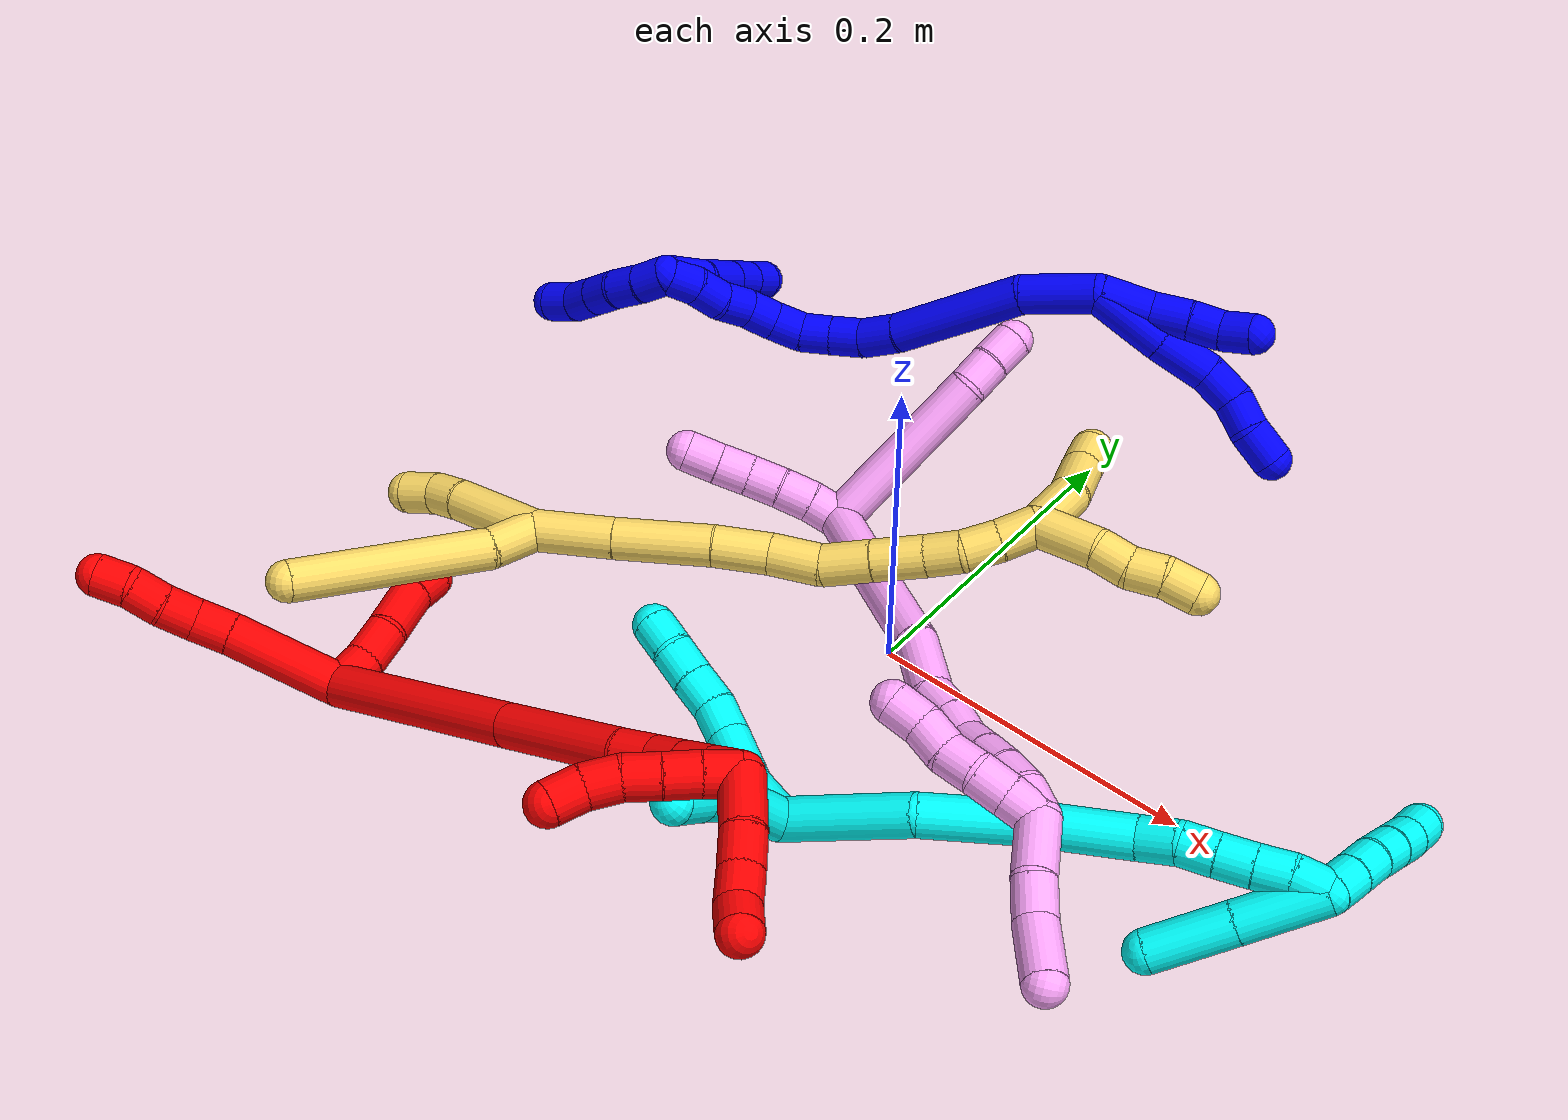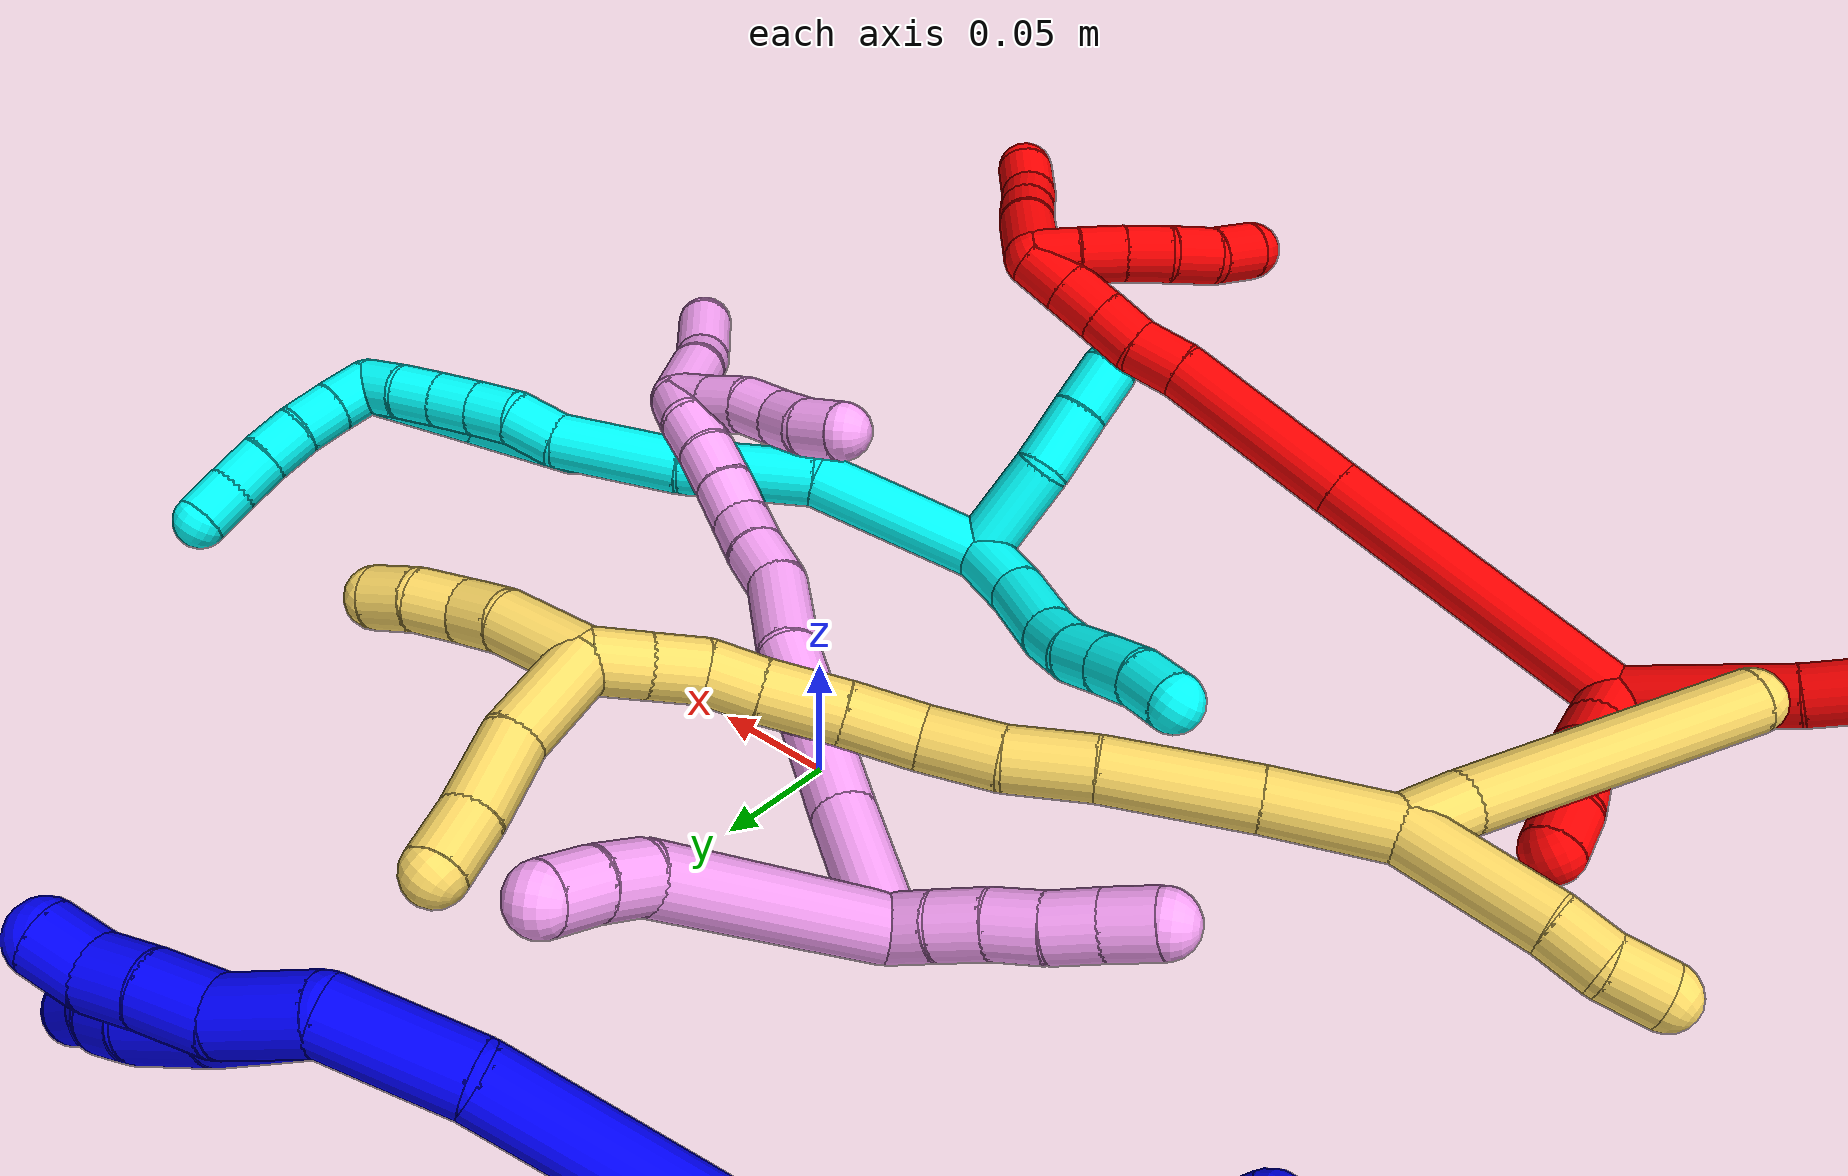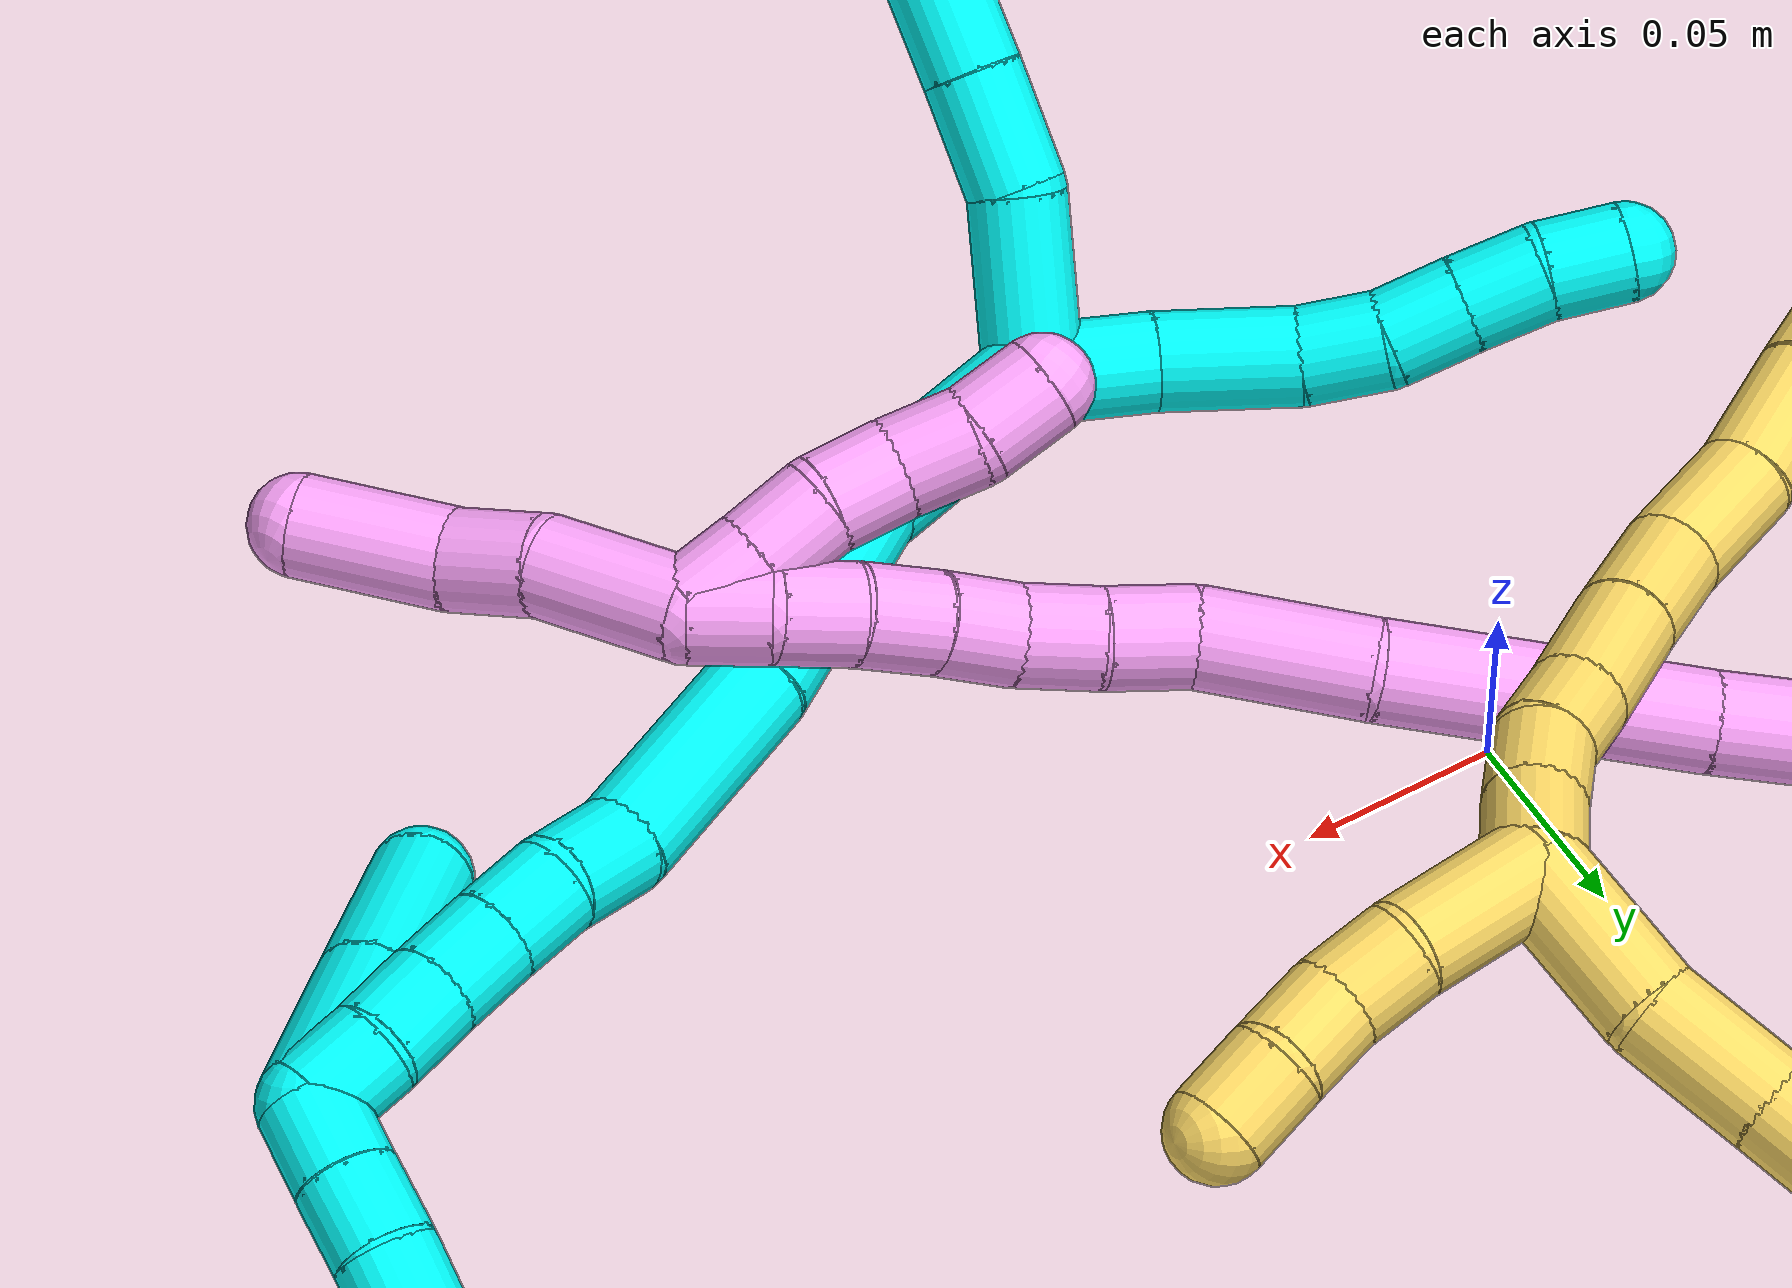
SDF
<sdf version="1.7">
 <world name="default">
  <plugin name="TubeGeneratorPlugin" filename="libtube_generator_plugin.so"/>
  <model name="photoneo_s_sensor">
   <static>1</static>
   <pose>0 0 2 1.57079 1.57079 3.14159</pose>
   <link name="link">
    <inertial><mass>0.1</mass></inertial>
    <sensor name="sensor" type="depth">
     <update_rate>30</update_rate>
     <camera>
      <horizontal_fov>1.22</horizontal_fov>
      <image><width>1920</width><height>1200</height><format>B8G8R8</format></image>
      <clip><near>0.1</near><far>4</far></clip>
      <depth_camera><output>points</output></depth_camera>
     </camera>
     <plugin name="camera_plugin" filename="libgazebo_ros_depth_camera.so">
      <baseline>0.2</baseline>
      <alwaysOn>1</alwaysOn>
      <updateRate>0.0</updateRate>
      <cameraName>camera_ir</cameraName>
      <imageTopicName>/camera/color/image_raw</imageTopicName>
      <cameraInfoTopicName>/camera/color/camera_info</cameraInfoTopicName>
      <depthImageTopicName>/camera/depth/image_raw</depthImageTopicName>
      <depthImageCameraInfoTopicName>/camera/depth/camera_info</depthImageCameraInfoTopicName>
      <pointCloudTopicName>/camera/depth/points</pointCloudTopicName>
      <frameName>fr_optical</frameName>
      <pointCloudCutoff>0.1</pointCloudCutoff>
      <pointCloudCutoffMax>2.0</pointCloudCutoffMax>
      <distortionK1>0</distortionK1>
      <distortionK2>0</distortionK2>
      <distortionK3>0</distortionK3>
      <distortionT1>0</distortionT1>
      <distortionT2>0</distortionT2>
      <CxPrime>0</CxPrime>
      <Cx>0</Cx>
      <Cy>0</Cy>
      <focalLength>0</focalLength>
      <hackBaseline>0</hackBaseline>
     </plugin>
    </sensor>
   </link>
  </model>
  <gravity>0 0 -9.8</gravity>
  <magnetic_field>6e-06 2.3e-05 -4.2e-05</magnetic_field>
  <atmosphere type="adiabatic"/>
  <physics name="default_physics" default="0" type="ode">
   <max_step_size>0.003</max_step_size>
   <real_time_factor>1</real_time_factor>
   <real_time_update_rate>1000</real_time_update_rate>
   <max_contacts>10000</max_contacts>
   <ode>
    <solver>
     <type>quick</type>
     <iters>100</iters>
     <sor>1.3</sor>
     <use_dynamic_moi_rescaling>0</use_dynamic_moi_rescaling>
    </solver>
    <constraints>
     <contact_max_correcting_vel>0</contact_max_correcting_vel>
     <contact_surface_layer>0.001</contact_surface_layer>
     <cfm>0</cfm>
     <erp>0.2</erp>
    </constraints>
   </ode>
  </physics>
  <scene><ambient>0.4 0.4 0.4 1</ambient><background>0.7 0.7 0.7 1</background><shadows>0</shadows></scene>
  <audio><device>default</device></audio>
  <spherical_coordinates>
   <surface_model>EARTH_WGS84</surface_model>
   <latitude_deg>0</latitude_deg>
   <longitude_deg>0</longitude_deg>
   <elevation>0</elevation>
   <heading_deg>0</heading_deg>
  </spherical_coordinates>
  <model name="bin">
   <static>1</static>
   <link name="bottom">
    <collision name="collision-bottom">
     <pose>0 0 -0.01 0 -0 0</pose>
     <geometry><box><size>0.8 0.6 0.02</size></box></geometry>
     <surface>
      <friction><ode><mu>100</mu><mu2>100</mu2></ode></friction>
      <contact><collide_bitmask>65535</collide_bitmask></contact>
     </surface>
    </collision>
   </link>
   <link name="west_wall">
    <collision name="collision-west_wall">
     <pose>-0.41 0 0.1 0 -0 0</pose>
     <geometry><box><size>0.02 0.6 0.2</size></box></geometry>
     <surface>
      <friction><ode><mu>100</mu><mu2>100</mu2></ode></friction>
      <contact><collide_bitmask>65535</collide_bitmask></contact>
     </surface>
    </collision>
   </link>
   <link name="east_wall">
    <collision name="collision-east_wall">
     <pose>0.41 0 0.1 0 -0 0</pose>
     <geometry><box><size>0.02 0.6 0.2</size></box></geometry>
     <surface>
      <friction><ode><mu>100</mu><mu2>100</mu2></ode></friction>
      <contact><collide_bitmask>65535</collide_bitmask></contact>
     </surface>
    </collision>
   </link>
   <link name="south_wall">
    <collision name="collision-south_wall">
     <pose>0 -0.31 0.1 0 -0 0</pose>
     <geometry><box><size>0.8 0.02 0.2</size></box></geometry>
     <surface>
      <friction><ode><mu>100</mu><mu2>100</mu2></ode></friction>
      <contact><collide_bitmask>65535</collide_bitmask></contact>
     </surface>
    </collision>
   </link>
   <link name="north_wall">
    <collision name="collision-north_wall">
     <pose>0 0.31 0.1 0 -0 0</pose>
     <geometry><box><size>0.8 0.02 0.2</size></box></geometry>
     <surface>
      <friction><ode><mu>100</mu><mu2>100</mu2></ode></friction>
      <contact><collide_bitmask>65535</collide_bitmask></contact>
     </surface>
    </collision>
   </link>
  </model>
  <model name="1">
   <static>0</static>
   <link name="1">
    <collision name="collision-cylinder-e_1_2_8">
     <pose>0.002042 3e-05 -0.023886 -3.14032 0.085286 -3.11182</pose>
     <geometry><cylinder><radius>0.0125</radius><length>0.047945</length></cylinder></geometry>
     <surface>
      <friction><ode><mu>1.16</mu><mu2>1.16</mu2><slip1>0</slip1><slip2>0</slip2></ode></friction>
      <contact><ode><kp>1e+06</kp><kd>1</kd><max_vel>0</max_vel><min_depth>0.001</min_depth></ode></contact>
     </surface>
    </collision>
    <visual name="visual-cylinder-e_1_2_8">
     <pose>0.002042 3e-05 -0.023886 -3.14032 0.085286 -3.11182</pose>
     <geometry><cylinder><radius>0.0125</radius><length>0.047945</length></cylinder></geometry>
     <material><ambient>0 0 1 1</ambient></material>
    </visual>
    <collision name="collision-cylinder-e_2_8_9">
     <pose>0.007211 -0.000536 -0.065163 3.10732 0.177765 2.76166</pose>
     <geometry><cylinder><radius>0.0125</radius><length>0.035362</length></cylinder></geometry>
     <surface>
      <friction><ode><mu>1.16</mu><mu2>1.16</mu2><slip1>0</slip1><slip2>0</slip2></ode></friction>
      <contact><ode><kp>1e+06</kp><kd>1</kd><max_vel>0</max_vel><min_depth>0.001</min_depth></ode></contact>
     </surface>
    </collision>
    <visual name="visual-cylinder-e_2_8_9">
     <pose>0.007211 -0.000536 -0.065163 3.10732 0.177765 2.76166</pose>
     <geometry><cylinder><radius>0.0125</radius><length>0.035362</length></cylinder></geometry>
     <material><ambient>0 0 1 1</ambient></material>
    </visual>
    <collision name="collision-cylinder-e_3_9_10">
     <pose>0.010529 -0.003783 -0.093695 2.90795 0.016764 0.142611</pose>
     <geometry><cylinder><radius>0.0125</radius><length>0.022905</length></cylinder></geometry>
     <surface>
      <friction><ode><mu>1.16</mu><mu2>1.16</mu2><slip1>0</slip1><slip2>0</slip2></ode></friction>
      <contact><ode><kp>1e+06</kp><kd>1</kd><max_vel>0</max_vel><min_depth>0.001</min_depth></ode></contact>
     </surface>
    </collision>
    <visual name="visual-cylinder-e_3_9_10">
     <pose>0.010529 -0.003783 -0.093695 2.90795 0.016764 0.142611</pose>
     <geometry><cylinder><radius>0.0125</radius><length>0.022905</length></cylinder></geometry>
     <material><ambient>0 0 1 1</ambient></material>
    </visual>
    <collision name="collision-cylinder-e_4_10_11">
     <pose>0.008613 -0.01085 -0.113751 2.68173 -0.208812 -0.841828</pose>
     <geometry><cylinder><radius>0.0125</radius><length>0.020341</length></cylinder></geometry>
     <surface>
      <friction><ode><mu>1.16</mu><mu2>1.16</mu2><slip1>0</slip1><slip2>0</slip2></ode></friction>
      <contact><ode><kp>1e+06</kp><kd>1</kd><max_vel>0</max_vel><min_depth>0.001</min_depth></ode></contact>
     </surface>
    </collision>
    <visual name="visual-cylinder-e_4_10_11">
     <pose>0.008613 -0.01085 -0.113751 2.68173 -0.208812 -0.841828</pose>
     <geometry><cylinder><radius>0.0125</radius><length>0.020341</length></cylinder></geometry>
     <material><ambient>0 0 1 1</ambient></material>
    </visual>
    <collision name="collision-cylinder-e_5_11_6">
     <pose>0.005011 -0.016979 -0.134168 2.99375 -0.127753 -1.4248</pose>
     <geometry><cylinder><radius>0.0125</radius><length>0.023447</length></cylinder></geometry>
     <surface>
      <friction><ode><mu>1.16</mu><mu2>1.16</mu2><slip1>0</slip1><slip2>0</slip2></ode></friction>
      <contact><ode><kp>1e+06</kp><kd>1</kd><max_vel>0</max_vel><min_depth>0.001</min_depth></ode></contact>
     </surface>
    </collision>
    <visual name="visual-cylinder-e_5_11_6">
     <pose>0.005011 -0.016979 -0.134168 2.99375 -0.127753 -1.4248</pose>
     <geometry><cylinder><radius>0.0125</radius><length>0.023447</length></cylinder></geometry>
     <material><ambient>0 0 1 1</ambient></material>
    </visual>
    <collision name="collision-cylinder-e_1_2_12">
     <pose>0.00634 0.002098 -0.015583 -3.00778 0.383298 -2.47655</pose>
     <geometry><cylinder><radius>0.0125</radius><length>0.033907</length></cylinder></geometry>
     <surface>
      <friction><ode><mu>1.16</mu><mu2>1.16</mu2><slip1>0</slip1><slip2>0</slip2></ode></friction>
      <contact><ode><kp>1e+06</kp><kd>1</kd><max_vel>0</max_vel><min_depth>0.001</min_depth></ode></contact>
     </surface>
    </collision>
    <visual name="visual-cylinder-e_1_2_12">
     <pose>0.00634 0.002098 -0.015583 -3.00778 0.383298 -2.47655</pose>
     <geometry><cylinder><radius>0.0125</radius><length>0.033907</length></cylinder></geometry>
     <material><ambient>0 0 1 1</ambient></material>
    </visual>
    <collision name="collision-cylinder-e_2_12_13">
     <pose>0.019915 0.002518 -0.041512 2.98087 0.604143 2.63575</pose>
     <geometry><cylinder><radius>0.0125</radius><length>0.025472</length></cylinder></geometry>
     <surface>
      <friction><ode><mu>1.16</mu><mu2>1.16</mu2><slip1>0</slip1><slip2>0</slip2></ode></friction>
      <contact><ode><kp>1e+06</kp><kd>1</kd><max_vel>0</max_vel><min_depth>0.001</min_depth></ode></contact>
     </surface>
    </collision>
    <visual name="visual-cylinder-e_2_12_13">
     <pose>0.019915 0.002518 -0.041512 2.98087 0.604143 2.63575</pose>
     <geometry><cylinder><radius>0.0125</radius><length>0.025472</length></cylinder></geometry>
     <material><ambient>0 0 1 1</ambient></material>
    </visual>
    <collision name="collision-cylinder-e_3_13_14">
     <pose>0.032011 -0.000357 -0.060675 3.00654 0.499991 2.62376</pose>
     <geometry><cylinder><radius>0.0125</radius><length>0.020278</length></cylinder></geometry>
     <surface>
      <friction><ode><mu>1.16</mu><mu2>1.16</mu2><slip1>0</slip1><slip2>0</slip2></ode></friction>
      <contact><ode><kp>1e+06</kp><kd>1</kd><max_vel>0</max_vel><min_depth>0.001</min_depth></ode></contact>
     </surface>
    </collision>
    <visual name="visual-cylinder-e_3_13_14">
     <pose>0.032011 -0.000357 -0.060675 3.00654 0.499991 2.62376</pose>
     <geometry><cylinder><radius>0.0125</radius><length>0.020278</length></cylinder></geometry>
     <material><ambient>0 0 1 1</ambient></material>
    </visual>
    <collision name="collision-cylinder-e_4_14_5">
     <pose>0.043923 -0.004221 -0.076321 2.7695 0.765962 2.26747</pose>
     <geometry><cylinder><radius>0.0125</radius><length>0.020343</length></cylinder></geometry>
     <surface>
      <friction><ode><mu>1.16</mu><mu2>1.16</mu2><slip1>0</slip1><slip2>0</slip2></ode></friction>
      <contact><ode><kp>1e+06</kp><kd>1</kd><max_vel>0</max_vel><min_depth>0.001</min_depth></ode></contact>
     </surface>
    </collision>
    <visual name="visual-cylinder-e_4_14_5">
     <pose>0.043923 -0.004221 -0.076321 2.7695 0.765962 2.26747</pose>
     <geometry><cylinder><radius>0.0125</radius><length>0.020343</length></cylinder></geometry>
     <material><ambient>0 0 1 1</ambient></material>
    </visual>
    <collision name="collision-cylinder-e_1_2_15">
     <pose>-0.017814 0.00214 0.015903 -0.133765 -0.837577 0.059613</pose>
     <geometry><cylinder><radius>0.0125</radius><length>0.047951</length></cylinder></geometry>
     <surface>
      <friction><ode><mu>1.16</mu><mu2>1.16</mu2><slip1>0</slip1><slip2>0</slip2></ode></friction>
      <contact><ode><kp>1e+06</kp><kd>1</kd><max_vel>0</max_vel><min_depth>0.001</min_depth></ode></contact>
     </surface>
    </collision>
    <visual name="visual-cylinder-e_1_2_15">
     <pose>-0.017814 0.00214 0.015903 -0.133765 -0.837577 0.059613</pose>
     <geometry><cylinder><radius>0.0125</radius><length>0.047951</length></cylinder></geometry>
     <material><ambient>0 0 1 1</ambient></material>
    </visual>
    <collision name="collision-cylinder-e_2_15_16">
     <pose>-0.074821 0.008516 0.049789 -0.231329 -1.13028 0.147085</pose>
     <geometry><cylinder><radius>0.0125</radius><length>0.086659</length></cylinder></geometry>
     <surface>
      <friction><ode><mu>1.16</mu><mu2>1.16</mu2><slip1>0</slip1><slip2>0</slip2></ode></friction>
      <contact><ode><kp>1e+06</kp><kd>1</kd><max_vel>0</max_vel><min_depth>0.001</min_depth></ode></contact>
     </surface>
    </collision>
    <visual name="visual-cylinder-e_2_15_16">
     <pose>-0.074821 0.008516 0.049789 -0.231329 -1.13028 0.147085</pose>
     <geometry><cylinder><radius>0.0125</radius><length>0.086659</length></cylinder></geometry>
     <material><ambient>0 0 1 1</ambient></material>
    </visual>
    <collision name="collision-cylinder-e_3_16_17">
     <pose>-0.124357 0.015048 0.074062 -0.350027 -0.996305 0.19176</pose>
     <geometry><cylinder><radius>0.0125</radius><length>0.024643</length></cylinder></geometry>
     <surface>
      <friction><ode><mu>1.16</mu><mu2>1.16</mu2><slip1>0</slip1><slip2>0</slip2></ode></friction>
      <contact><ode><kp>1e+06</kp><kd>1</kd><max_vel>0</max_vel><min_depth>0.001</min_depth></ode></contact>
     </surface>
    </collision>
    <visual name="visual-cylinder-e_3_16_17">
     <pose>-0.124357 0.015048 0.074062 -0.350027 -0.996305 0.19176</pose>
     <geometry><cylinder><radius>0.0125</radius><length>0.024643</length></cylinder></geometry>
     <material><ambient>0 0 1 1</ambient></material>
    </visual>
    <collision name="collision-cylinder-e_4_17_18">
     <pose>-0.141784 0.018638 0.087796 -0.172157 -0.753153 0.068221</pose>
     <geometry><cylinder><radius>0.0125</radius><length>0.020713</length></cylinder></geometry>
     <surface>
      <friction><ode><mu>1.16</mu><mu2>1.16</mu2><slip1>0</slip1><slip2>0</slip2></ode></friction>
      <contact><ode><kp>1e+06</kp><kd>1</kd><max_vel>0</max_vel><min_depth>0.001</min_depth></ode></contact>
     </surface>
    </collision>
    <visual name="visual-cylinder-e_4_17_18">
     <pose>-0.141784 0.018638 0.087796 -0.172157 -0.753153 0.068221</pose>
     <geometry><cylinder><radius>0.0125</radius><length>0.020713</length></cylinder></geometry>
     <material><ambient>0 0 1 1</ambient></material>
    </visual>
    <collision name="collision-cylinder-e_5_18_19">
     <pose>-0.15521 0.019905 0.102975 0.003534 -0.686801 -0.001264</pose>
     <geometry><cylinder><radius>0.0125</radius><length>0.020006</length></cylinder></geometry>
     <surface>
      <friction><ode><mu>1.16</mu><mu2>1.16</mu2><slip1>0</slip1><slip2>0</slip2></ode></friction>
      <contact><ode><kp>1e+06</kp><kd>1</kd><max_vel>0</max_vel><min_depth>0.001</min_depth></ode></contact>
     </surface>
    </collision>
    <visual name="visual-cylinder-e_5_18_19">
     <pose>-0.15521 0.019905 0.102975 0.003534 -0.686801 -0.001264</pose>
     <geometry><cylinder><radius>0.0125</radius><length>0.020006</length></cylinder></geometry>
     <material><ambient>0 0 1 1</ambient></material>
    </visual>
    <collision name="collision-cylinder-e_6_19_20">
     <pose>-0.164941 0.019094 0.120089 0.083378 -0.345583 -0.01456</pose>
     <geometry><cylinder><radius>0.0125</radius><length>0.020007</length></cylinder></geometry>
     <surface>
      <friction><ode><mu>1.16</mu><mu2>1.16</mu2><slip1>0</slip1><slip2>0</slip2></ode></friction>
      <contact><ode><kp>1e+06</kp><kd>1</kd><max_vel>0</max_vel><min_depth>0.001</min_depth></ode></contact>
     </surface>
    </collision>
    <visual name="visual-cylinder-e_6_19_20">
     <pose>-0.164941 0.019094 0.120089 0.083378 -0.345583 -0.01456</pose>
     <geometry><cylinder><radius>0.0125</radius><length>0.020007</length></cylinder></geometry>
     <material><ambient>0 0 1 1</ambient></material>
    </visual>
    <collision name="collision-cylinder-e_7_20_21">
     <pose>-0.169798 0.014988 0.138794 0.342234 -0.14721 -0.025484</pose>
     <geometry><cylinder><radius>0.0125</radius><length>0.020015</length></cylinder></geometry>
     <surface>
      <friction><ode><mu>1.16</mu><mu2>1.16</mu2><slip1>0</slip1><slip2>0</slip2></ode></friction>
      <contact><ode><kp>1e+06</kp><kd>1</kd><max_vel>0</max_vel><min_depth>0.001</min_depth></ode></contact>
     </surface>
    </collision>
    <visual name="visual-cylinder-e_7_20_21">
     <pose>-0.169798 0.014988 0.138794 0.342234 -0.14721 -0.025484</pose>
     <geometry><cylinder><radius>0.0125</radius><length>0.020015</length></cylinder></geometry>
     <material><ambient>0 0 1 1</ambient></material>
    </visual>
    <collision name="collision-cylinder-e_8_21_22">
     <pose>-0.172698 0.005953 0.156201 0.615393 -0.143774 -0.045761</pose>
     <geometry><cylinder><radius>0.0125</radius><length>0.020001</length></cylinder></geometry>
     <surface>
      <friction><ode><mu>1.16</mu><mu2>1.16</mu2><slip1>0</slip1><slip2>0</slip2></ode></friction>
      <contact><ode><kp>1e+06</kp><kd>1</kd><max_vel>0</max_vel><min_depth>0.001</min_depth></ode></contact>
     </surface>
    </collision>
    <visual name="visual-cylinder-e_8_21_22">
     <pose>-0.172698 0.005953 0.156201 0.615393 -0.143774 -0.045761</pose>
     <geometry><cylinder><radius>0.0125</radius><length>0.020001</length></cylinder></geometry>
     <material><ambient>0 0 1 1</ambient></material>
    </visual>
    <collision name="collision-cylinder-e_9_22_23">
     <pose>-0.174112 -0.003608 0.173513 0.394861 0.001939 0.000388</pose>
     <geometry><cylinder><radius>0.0125</radius><length>0.020001</length></cylinder></geometry>
     <surface>
      <friction><ode><mu>1.16</mu><mu2>1.16</mu2><slip1>0</slip1><slip2>0</slip2></ode></friction>
      <contact><ode><kp>1e+06</kp><kd>1</kd><max_vel>0</max_vel><min_depth>0.001</min_depth></ode></contact>
     </surface>
    </collision>
    <visual name="visual-cylinder-e_9_22_23">
     <pose>-0.174112 -0.003608 0.173513 0.394861 0.001939 0.000388</pose>
     <geometry><cylinder><radius>0.0125</radius><length>0.020001</length></cylinder></geometry>
     <material><ambient>0 0 1 1</ambient></material>
    </visual>
    <collision name="collision-cylinder-e_10_23_1">
     <pose>-0.175857 -0.01164 0.191656 0.439023 -0.177383 -0.039674</pose>
     <geometry><cylinder><radius>0.0125</radius><length>0.020005</length></cylinder></geometry>
     <surface>
      <friction><ode><mu>1.16</mu><mu2>1.16</mu2><slip1>0</slip1><slip2>0</slip2></ode></friction>
      <contact><ode><kp>1e+06</kp><kd>1</kd><max_vel>0</max_vel><min_depth>0.001</min_depth></ode></contact>
     </surface>
    </collision>
    <visual name="visual-cylinder-e_10_23_1">
     <pose>-0.175857 -0.01164 0.191656 0.439023 -0.177383 -0.039674</pose>
     <geometry><cylinder><radius>0.0125</radius><length>0.020005</length></cylinder></geometry>
     <material><ambient>0 0 1 1</ambient></material>
    </visual>
    <collision name="collision-cylinder-e_1_1_24">
     <pose>-0.186671 -0.014124 0.20447 -0.410867 -1.13106 0.262975</pose>
     <geometry><cylinder><radius>0.0125</radius><length>0.02</length></cylinder></geometry>
     <surface>
      <friction><ode><mu>1.16</mu><mu2>1.16</mu2><slip1>0</slip1><slip2>0</slip2></ode></friction>
      <contact><ode><kp>1e+06</kp><kd>1</kd><max_vel>0</max_vel><min_depth>0.001</min_depth></ode></contact>
     </surface>
    </collision>
    <visual name="visual-cylinder-e_1_1_24">
     <pose>-0.186671 -0.014124 0.20447 -0.410867 -1.13106 0.262975</pose>
     <geometry><cylinder><radius>0.0125</radius><length>0.02</length></cylinder></geometry>
     <material><ambient>0 0 1 1</ambient></material>
    </visual>
    <collision name="collision-cylinder-e_2_24_25">
     <pose>-0.204302 -0.009804 0.212786 -0.535812 -1.0318 0.308881</pose>
     <geometry><cylinder><radius>0.0125</radius><length>0.02</length></cylinder></geometry>
     <surface>
      <friction><ode><mu>1.16</mu><mu2>1.16</mu2><slip1>0</slip1><slip2>0</slip2></ode></friction>
      <contact><ode><kp>1e+06</kp><kd>1</kd><max_vel>0</max_vel><min_depth>0.001</min_depth></ode></contact>
     </surface>
    </collision>
    <visual name="visual-cylinder-e_2_24_25">
     <pose>-0.204302 -0.009804 0.212786 -0.535812 -1.0318 0.308881</pose>
     <geometry><cylinder><radius>0.0125</radius><length>0.02</length></cylinder></geometry>
     <material><ambient>0 0 1 1</ambient></material>
    </visual>
    <collision name="collision-cylinder-e_3_25_26">
     <pose>-0.221451 -0.003033 0.220264 -0.934836 -1.02872 0.555681</pose>
     <geometry><cylinder><radius>0.0125</radius><length>0.02</length></cylinder></geometry>
     <surface>
      <friction><ode><mu>1.16</mu><mu2>1.16</mu2><slip1>0</slip1><slip2>0</slip2></ode></friction>
      <contact><ode><kp>1e+06</kp><kd>1</kd><max_vel>0</max_vel><min_depth>0.001</min_depth></ode></contact>
     </surface>
    </collision>
    <visual name="visual-cylinder-e_3_25_26">
     <pose>-0.221451 -0.003033 0.220264 -0.934836 -1.02872 0.555681</pose>
     <geometry><cylinder><radius>0.0125</radius><length>0.02</length></cylinder></geometry>
     <material><ambient>0 0 1 1</ambient></material>
    </visual>
    <collision name="collision-cylinder-e_4_26_27">
     <pose>-0.238608 0.005174 0.22645 -0.914918 -1.03346 0.545517</pose>
     <geometry><cylinder><radius>0.0125</radius><length>0.02</length></cylinder></geometry>
     <surface>
      <friction><ode><mu>1.16</mu><mu2>1.16</mu2><slip1>0</slip1><slip2>0</slip2></ode></friction>
      <contact><ode><kp>1e+06</kp><kd>1</kd><max_vel>0</max_vel><min_depth>0.001</min_depth></ode></contact>
     </surface>
    </collision>
    <visual name="visual-cylinder-e_4_26_27">
     <pose>-0.238608 0.005174 0.22645 -0.914918 -1.03346 0.545517</pose>
     <geometry><cylinder><radius>0.0125</radius><length>0.02</length></cylinder></geometry>
     <material><ambient>0 0 1 1</ambient></material>
    </visual>
    <collision name="collision-cylinder-e_5_27_4">
     <pose>-0.254698 0.012707 0.235199 -0.553238 -0.848017 0.254907</pose>
     <geometry><cylinder><radius>0.0125</radius><length>0.02</length></cylinder></geometry>
     <surface>
      <friction><ode><mu>1.16</mu><mu2>1.16</mu2><slip1>0</slip1><slip2>0</slip2></ode></friction>
      <contact><ode><kp>1e+06</kp><kd>1</kd><max_vel>0</max_vel><min_depth>0.001</min_depth></ode></contact>
     </surface>
    </collision>
    <visual name="visual-cylinder-e_5_27_4">
     <pose>-0.254698 0.012707 0.235199 -0.553238 -0.848017 0.254907</pose>
     <geometry><cylinder><radius>0.0125</radius><length>0.02</length></cylinder></geometry>
     <material><ambient>0 0 1 1</ambient></material>
    </visual>
    <collision name="collision-cylinder-e_1_1_28">
     <pose>-0.175608 -0.005243 0.190799 -2.31625 0.139001 -0.315365</pose>
     <geometry><cylinder><radius>0.0125</radius><length>0.029081</length></cylinder></geometry>
     <surface>
      <friction><ode><mu>1.16</mu><mu2>1.16</mu2><slip1>0</slip1><slip2>0</slip2></ode></friction>
      <contact><ode><kp>1e+06</kp><kd>1</kd><max_vel>0</max_vel><min_depth>0.001</min_depth></ode></contact>
     </surface>
    </collision>
    <visual name="visual-cylinder-e_1_1_28">
     <pose>-0.175608 -0.005243 0.190799 -2.31625 0.139001 -0.315365</pose>
     <geometry><cylinder><radius>0.0125</radius><length>0.029081</length></cylinder></geometry>
     <material><ambient>0 0 1 1</ambient></material>
    </visual>
    <collision name="collision-cylinder-e_2_28_29">
     <pose>-0.173862 0.018293 0.174083 -2.06312 -0.018274 0.030538</pose>
     <geometry><cylinder><radius>0.0125</radius><length>0.029407</length></cylinder></geometry>
     <surface>
      <friction><ode><mu>1.16</mu><mu2>1.16</mu2><slip1>0</slip1><slip2>0</slip2></ode></friction>
      <contact><ode><kp>1e+06</kp><kd>1</kd><max_vel>0</max_vel><min_depth>0.001</min_depth></ode></contact>
     </surface>
    </collision>
    <visual name="visual-cylinder-e_2_28_29">
     <pose>-0.173862 0.018293 0.174083 -2.06312 -0.018274 0.030538</pose>
     <geometry><cylinder><radius>0.0125</radius><length>0.029407</length></cylinder></geometry>
     <material><ambient>0 0 1 1</ambient></material>
    </visual>
    <collision name="collision-cylinder-e_3_29_30">
     <pose>-0.174429 0.040644 0.161945 -2.07534 -0.027777 0.047064</pose>
     <geometry><cylinder><radius>0.0125</radius><length>0.021476</length></cylinder></geometry>
     <surface>
      <friction><ode><mu>1.16</mu><mu2>1.16</mu2><slip1>0</slip1><slip2>0</slip2></ode></friction>
      <contact><ode><kp>1e+06</kp><kd>1</kd><max_vel>0</max_vel><min_depth>0.001</min_depth></ode></contact>
     </surface>
    </collision>
    <visual name="visual-cylinder-e_3_29_30">
     <pose>-0.174429 0.040644 0.161945 -2.07534 -0.027777 0.047064</pose>
     <geometry><cylinder><radius>0.0125</radius><length>0.021476</length></cylinder></geometry>
     <material><ambient>0 0 1 1</ambient></material>
    </visual>
    <collision name="collision-cylinder-e_4_30_3">
     <pose>-0.174814 0.058942 0.152162 -2.04722 -0.008679 0.014245</pose>
     <geometry><cylinder><radius>0.0125</radius><length>0.020036</length></cylinder></geometry>
     <surface>
      <friction><ode><mu>1.16</mu><mu2>1.16</mu2><slip1>0</slip1><slip2>0</slip2></ode></friction>
      <contact><ode><kp>1e+06</kp><kd>1</kd><max_vel>0</max_vel><min_depth>0.001</min_depth></ode></contact>
     </surface>
    </collision>
    <visual name="visual-cylinder-e_4_30_3">
     <pose>-0.174814 0.058942 0.152162 -2.04722 -0.008679 0.014245</pose>
     <geometry><cylinder><radius>0.0125</radius><length>0.020036</length></cylinder></geometry>
     <material><ambient>0 0 1 1</ambient></material>
    </visual>
    <collision name="collision-sphere-3">
     <pose>-0.174901 0.067844 0.147568 0 -0 0</pose>
     <geometry><sphere><radius>0.0125</radius></sphere></geometry>
     <surface>
      <friction><ode><mu>1.16</mu><mu2>1.16</mu2><slip1>0</slip1><slip2>0</slip2></ode></friction>
      <contact><ode><kp>1e+06</kp><kd>1</kd><max_vel>0</max_vel><min_depth>0.001</min_depth></ode></contact>
     </surface>
    </collision>
    <visual name="visual-sphere-3">
     <pose>-0.174901 0.067844 0.147568 0 -0 0</pose>
     <geometry><sphere><radius>0.0125</radius></sphere></geometry>
     <material><ambient>0 0 1 1</ambient></material>
    </visual>
    <collision name="collision-sphere-30">
     <pose>-0.174727 0.05004 0.156756 0 -0 0</pose>
     <geometry><sphere><radius>0.0125</radius></sphere></geometry>
     <surface>
      <friction><ode><mu>1.16</mu><mu2>1.16</mu2><slip1>0</slip1><slip2>0</slip2></ode></friction>
      <contact><ode><kp>1e+06</kp><kd>1</kd><max_vel>0</max_vel><min_depth>0.001</min_depth></ode></contact>
     </surface>
    </collision>
    <visual name="visual-sphere-30">
     <pose>-0.174727 0.05004 0.156756 0 -0 0</pose>
     <geometry><sphere><radius>0.0125</radius></sphere></geometry>
     <material><ambient>0 0 1 1</ambient></material>
    </visual>
    <collision name="collision-sphere-29">
     <pose>-0.17413 0.031248 0.167134 0 -0 0</pose>
     <geometry><sphere><radius>0.0125</radius></sphere></geometry>
     <surface>
      <friction><ode><mu>1.16</mu><mu2>1.16</mu2><slip1>0</slip1><slip2>0</slip2></ode></friction>
      <contact><ode><kp>1e+06</kp><kd>1</kd><max_vel>0</max_vel><min_depth>0.001</min_depth></ode></contact>
     </surface>
    </collision>
    <visual name="visual-sphere-29">
     <pose>-0.17413 0.031248 0.167134 0 -0 0</pose>
     <geometry><sphere><radius>0.0125</radius></sphere></geometry>
     <material><ambient>0 0 1 1</ambient></material>
    </visual>
    <collision name="collision-sphere-28">
     <pose>-0.173593 0.005338 0.181031 0 -0 0</pose>
     <geometry><sphere><radius>0.0125</radius></sphere></geometry>
     <surface>
      <friction><ode><mu>1.16</mu><mu2>1.16</mu2><slip1>0</slip1><slip2>0</slip2></ode></friction>
      <contact><ode><kp>1e+06</kp><kd>1</kd><max_vel>0</max_vel><min_depth>0.001</min_depth></ode></contact>
     </surface>
    </collision>
    <visual name="visual-sphere-28">
     <pose>-0.173593 0.005338 0.181031 0 -0 0</pose>
     <geometry><sphere><radius>0.0125</radius></sphere></geometry>
     <material><ambient>0 0 1 1</ambient></material>
    </visual>
    <collision name="collision-sphere-4">
     <pose>-0.262198 0.016182 0.240827 0 -0 0</pose>
     <geometry><sphere><radius>0.0125</radius></sphere></geometry>
     <surface>
      <friction><ode><mu>1.16</mu><mu2>1.16</mu2><slip1>0</slip1><slip2>0</slip2></ode></friction>
      <contact><ode><kp>1e+06</kp><kd>1</kd><max_vel>0</max_vel><min_depth>0.001</min_depth></ode></contact>
     </surface>
    </collision>
    <visual name="visual-sphere-4">
     <pose>-0.262198 0.016182 0.240827 0 -0 0</pose>
     <geometry><sphere><radius>0.0125</radius></sphere></geometry>
     <material><ambient>0 0 1 1</ambient></material>
    </visual>
    <collision name="collision-sphere-27">
     <pose>-0.247198 0.009231 0.229571 0 -0 0</pose>
     <geometry><sphere><radius>0.0125</radius></sphere></geometry>
     <surface>
      <friction><ode><mu>1.16</mu><mu2>1.16</mu2><slip1>0</slip1><slip2>0</slip2></ode></friction>
      <contact><ode><kp>1e+06</kp><kd>1</kd><max_vel>0</max_vel><min_depth>0.001</min_depth></ode></contact>
     </surface>
    </collision>
    <visual name="visual-sphere-27">
     <pose>-0.247198 0.009231 0.229571 0 -0 0</pose>
     <geometry><sphere><radius>0.0125</radius></sphere></geometry>
     <material><ambient>0 0 1 1</ambient></material>
    </visual>
    <collision name="collision-sphere-26">
     <pose>-0.230017 0.001118 0.223328 0 -0 0</pose>
     <geometry><sphere><radius>0.0125</radius></sphere></geometry>
     <surface>
      <friction><ode><mu>1.16</mu><mu2>1.16</mu2><slip1>0</slip1><slip2>0</slip2></ode></friction>
      <contact><ode><kp>1e+06</kp><kd>1</kd><max_vel>0</max_vel><min_depth>0.001</min_depth></ode></contact>
     </surface>
    </collision>
    <visual name="visual-sphere-26">
     <pose>-0.230017 0.001118 0.223328 0 -0 0</pose>
     <geometry><sphere><radius>0.0125</radius></sphere></geometry>
     <material><ambient>0 0 1 1</ambient></material>
    </visual>
    <collision name="collision-sphere-25">
     <pose>-0.212884 -0.007183 0.2172 0 -0 0</pose>
     <geometry><sphere><radius>0.0125</radius></sphere></geometry>
     <surface>
      <friction><ode><mu>1.16</mu><mu2>1.16</mu2><slip1>0</slip1><slip2>0</slip2></ode></friction>
      <contact><ode><kp>1e+06</kp><kd>1</kd><max_vel>0</max_vel><min_depth>0.001</min_depth></ode></contact>
     </surface>
    </collision>
    <visual name="visual-sphere-25">
     <pose>-0.212884 -0.007183 0.2172 0 -0 0</pose>
     <geometry><sphere><radius>0.0125</radius></sphere></geometry>
     <material><ambient>0 0 1 1</ambient></material>
    </visual>
    <collision name="collision-sphere-24">
     <pose>-0.19572 -0.012424 0.208373 0 -0 0</pose>
     <geometry><sphere><radius>0.0125</radius></sphere></geometry>
     <surface>
      <friction><ode><mu>1.16</mu><mu2>1.16</mu2><slip1>0</slip1><slip2>0</slip2></ode></friction>
      <contact><ode><kp>1e+06</kp><kd>1</kd><max_vel>0</max_vel><min_depth>0.001</min_depth></ode></contact>
     </surface>
    </collision>
    <visual name="visual-sphere-24">
     <pose>-0.19572 -0.012424 0.208373 0 -0 0</pose>
     <geometry><sphere><radius>0.0125</radius></sphere></geometry>
     <material><ambient>0 0 1 1</ambient></material>
    </visual>
    <collision name="collision-sphere-1">
     <pose>-0.177622 -0.015825 0.200567 0 -0 0</pose>
     <geometry><sphere><radius>0.0125</radius></sphere></geometry>
     <surface>
      <friction><ode><mu>1.16</mu><mu2>1.16</mu2><slip1>0</slip1><slip2>0</slip2></ode></friction>
      <contact><ode><kp>1e+06</kp><kd>1</kd><max_vel>0</max_vel><min_depth>0.001</min_depth></ode></contact>
     </surface>
    </collision>
    <visual name="visual-sphere-1">
     <pose>-0.177622 -0.015825 0.200567 0 -0 0</pose>
     <geometry><sphere><radius>0.0125</radius></sphere></geometry>
     <material><ambient>0 0 1 1</ambient></material>
    </visual>
    <collision name="collision-sphere-23">
     <pose>-0.174092 -0.007455 0.182744 0 -0 0</pose>
     <geometry><sphere><radius>0.0125</radius></sphere></geometry>
     <surface>
      <friction><ode><mu>1.16</mu><mu2>1.16</mu2><slip1>0</slip1><slip2>0</slip2></ode></friction>
      <contact><ode><kp>1e+06</kp><kd>1</kd><max_vel>0</max_vel><min_depth>0.001</min_depth></ode></contact>
     </surface>
    </collision>
    <visual name="visual-sphere-23">
     <pose>-0.174092 -0.007455 0.182744 0 -0 0</pose>
     <geometry><sphere><radius>0.0125</radius></sphere></geometry>
     <material><ambient>0 0 1 1</ambient></material>
    </visual>
    <collision name="collision-sphere-22">
     <pose>-0.174131 0.000239 0.164282 0 -0 0</pose>
     <geometry><sphere><radius>0.0125</radius></sphere></geometry>
     <surface>
      <friction><ode><mu>1.16</mu><mu2>1.16</mu2><slip1>0</slip1><slip2>0</slip2></ode></friction>
      <contact><ode><kp>1e+06</kp><kd>1</kd><max_vel>0</max_vel><min_depth>0.001</min_depth></ode></contact>
     </surface>
    </collision>
    <visual name="visual-sphere-22">
     <pose>-0.174131 0.000239 0.164282 0 -0 0</pose>
     <geometry><sphere><radius>0.0125</radius></sphere></geometry>
     <material><ambient>0 0 1 1</ambient></material>
    </visual>
    <collision name="collision-sphere-21">
     <pose>-0.171265 0.011666 0.148119 0 -0 0</pose>
     <geometry><sphere><radius>0.0125</radius></sphere></geometry>
     <surface>
      <friction><ode><mu>1.16</mu><mu2>1.16</mu2><slip1>0</slip1><slip2>0</slip2></ode></friction>
      <contact><ode><kp>1e+06</kp><kd>1</kd><max_vel>0</max_vel><min_depth>0.001</min_depth></ode></contact>
     </surface>
    </collision>
    <visual name="visual-sphere-21">
     <pose>-0.171265 0.011666 0.148119 0 -0 0</pose>
     <geometry><sphere><radius>0.0125</radius></sphere></geometry>
     <material><ambient>0 0 1 1</ambient></material>
    </visual>
    <collision name="collision-sphere-6">
     <pose>0.003517 -0.018691 -0.145669 0 -0 0</pose>
     <geometry><sphere><radius>0.0125</radius></sphere></geometry>
     <surface>
      <friction><ode><mu>1.16</mu><mu2>1.16</mu2><slip1>0</slip1><slip2>0</slip2></ode></friction>
      <contact><ode><kp>1e+06</kp><kd>1</kd><max_vel>0</max_vel><min_depth>0.001</min_depth></ode></contact>
     </surface>
    </collision>
    <visual name="visual-sphere-6">
     <pose>0.003517 -0.018691 -0.145669 0 -0 0</pose>
     <geometry><sphere><radius>0.0125</radius></sphere></geometry>
     <material><ambient>0 0 1 1</ambient></material>
    </visual>
    <collision name="collision-sphere-11">
     <pose>0.006505 -0.015266 -0.122666 0 -0 0</pose>
     <geometry><sphere><radius>0.0125</radius></sphere></geometry>
     <surface>
      <friction><ode><mu>1.16</mu><mu2>1.16</mu2><slip1>0</slip1><slip2>0</slip2></ode></friction>
      <contact><ode><kp>1e+06</kp><kd>1</kd><max_vel>0</max_vel><min_depth>0.001</min_depth></ode></contact>
     </surface>
    </collision>
    <visual name="visual-sphere-11">
     <pose>0.006505 -0.015266 -0.122666 0 -0 0</pose>
     <geometry><sphere><radius>0.0125</radius></sphere></geometry>
     <material><ambient>0 0 1 1</ambient></material>
    </visual>
    <collision name="collision-sphere-10">
     <pose>0.010721 -0.006434 -0.104835 0 -0 0</pose>
     <geometry><sphere><radius>0.0125</radius></sphere></geometry>
     <surface>
      <friction><ode><mu>1.16</mu><mu2>1.16</mu2><slip1>0</slip1><slip2>0</slip2></ode></friction>
      <contact><ode><kp>1e+06</kp><kd>1</kd><max_vel>0</max_vel><min_depth>0.001</min_depth></ode></contact>
     </surface>
    </collision>
    <visual name="visual-sphere-10">
     <pose>0.010721 -0.006434 -0.104835 0 -0 0</pose>
     <geometry><sphere><radius>0.0125</radius></sphere></geometry>
     <material><ambient>0 0 1 1</ambient></material>
    </visual>
    <collision name="collision-sphere-9">
     <pose>0.010337 -0.001132 -0.082555 0 -0 0</pose>
     <geometry><sphere><radius>0.0125</radius></sphere></geometry>
     <surface>
      <friction><ode><mu>1.16</mu><mu2>1.16</mu2><slip1>0</slip1><slip2>0</slip2></ode></friction>
      <contact><ode><kp>1e+06</kp><kd>1</kd><max_vel>0</max_vel><min_depth>0.001</min_depth></ode></contact>
     </surface>
    </collision>
    <visual name="visual-sphere-9">
     <pose>0.010337 -0.001132 -0.082555 0 -0 0</pose>
     <geometry><sphere><radius>0.0125</radius></sphere></geometry>
     <material><ambient>0 0 1 1</ambient></material>
    </visual>
    <collision name="collision-sphere-2">
     <geometry><sphere><radius>0.0125</radius></sphere></geometry>
     <surface>
      <friction><ode><mu>1.16</mu><mu2>1.16</mu2><slip1>0</slip1><slip2>0</slip2></ode></friction>
      <contact><ode><kp>1e+06</kp><kd>1</kd><max_vel>0</max_vel><min_depth>0.001</min_depth></ode></contact>
     </surface>
    </collision>
    <visual name="visual-sphere-2">
     <geometry><sphere><radius>0.0125</radius></sphere></geometry>
     <material><ambient>0 0 1 1</ambient></material>
    </visual>
    <collision name="collision-sphere-19">
     <pose>-0.161552 0.019878 0.11071 0 -0 0</pose>
     <geometry><sphere><radius>0.0125</radius></sphere></geometry>
     <surface>
      <friction><ode><mu>1.16</mu><mu2>1.16</mu2><slip1>0</slip1><slip2>0</slip2></ode></friction>
      <contact><ode><kp>1e+06</kp><kd>1</kd><max_vel>0</max_vel><min_depth>0.001</min_depth></ode></contact>
     </surface>
    </collision>
    <visual name="visual-sphere-19">
     <pose>-0.161552 0.019878 0.11071 0 -0 0</pose>
     <geometry><sphere><radius>0.0125</radius></sphere></geometry>
     <material><ambient>0 0 1 1</ambient></material>
    </visual>
    <collision name="collision-sphere-8">
     <pose>0.004084 6.1e-05 -0.047771 0 -0 0</pose>
     <geometry><sphere><radius>0.0125</radius></sphere></geometry>
     <surface>
      <friction><ode><mu>1.16</mu><mu2>1.16</mu2><slip1>0</slip1><slip2>0</slip2></ode></friction>
      <contact><ode><kp>1e+06</kp><kd>1</kd><max_vel>0</max_vel><min_depth>0.001</min_depth></ode></contact>
     </surface>
    </collision>
    <visual name="visual-sphere-8">
     <pose>0.004084 6.1e-05 -0.047771 0 -0 0</pose>
     <geometry><sphere><radius>0.0125</radius></sphere></geometry>
     <material><ambient>0 0 1 1</ambient></material>
    </visual>
    <collision name="collision-sphere-12">
     <pose>0.01268 0.004195 -0.031165 0 -0 0</pose>
     <geometry><sphere><radius>0.0125</radius></sphere></geometry>
     <surface>
      <friction><ode><mu>1.16</mu><mu2>1.16</mu2><slip1>0</slip1><slip2>0</slip2></ode></friction>
      <contact><ode><kp>1e+06</kp><kd>1</kd><max_vel>0</max_vel><min_depth>0.001</min_depth></ode></contact>
     </surface>
    </collision>
    <visual name="visual-sphere-12">
     <pose>0.01268 0.004195 -0.031165 0 -0 0</pose>
     <geometry><sphere><radius>0.0125</radius></sphere></geometry>
     <material><ambient>0 0 1 1</ambient></material>
    </visual>
    <collision name="collision-sphere-13">
     <pose>0.02715 0.000841 -0.051858 0 -0 0</pose>
     <geometry><sphere><radius>0.0125</radius></sphere></geometry>
     <surface>
      <friction><ode><mu>1.16</mu><mu2>1.16</mu2><slip1>0</slip1><slip2>0</slip2></ode></friction>
      <contact><ode><kp>1e+06</kp><kd>1</kd><max_vel>0</max_vel><min_depth>0.001</min_depth></ode></contact>
     </surface>
    </collision>
    <visual name="visual-sphere-13">
     <pose>0.02715 0.000841 -0.051858 0 -0 0</pose>
     <geometry><sphere><radius>0.0125</radius></sphere></geometry>
     <material><ambient>0 0 1 1</ambient></material>
    </visual>
    <collision name="collision-sphere-14">
     <pose>0.036872 -0.001556 -0.069492 0 -0 0</pose>
     <geometry><sphere><radius>0.0125</radius></sphere></geometry>
     <surface>
      <friction><ode><mu>1.16</mu><mu2>1.16</mu2><slip1>0</slip1><slip2>0</slip2></ode></friction>
      <contact><ode><kp>1e+06</kp><kd>1</kd><max_vel>0</max_vel><min_depth>0.001</min_depth></ode></contact>
     </surface>
    </collision>
    <visual name="visual-sphere-14">
     <pose>0.036872 -0.001556 -0.069492 0 -0 0</pose>
     <geometry><sphere><radius>0.0125</radius></sphere></geometry>
     <material><ambient>0 0 1 1</ambient></material>
    </visual>
    <collision name="collision-sphere-5">
     <pose>0.050974 -0.006886 -0.08315 0 -0 0</pose>
     <geometry><sphere><radius>0.0125</radius></sphere></geometry>
     <surface>
      <friction><ode><mu>1.16</mu><mu2>1.16</mu2><slip1>0</slip1><slip2>0</slip2></ode></friction>
      <contact><ode><kp>1e+06</kp><kd>1</kd><max_vel>0</max_vel><min_depth>0.001</min_depth></ode></contact>
     </surface>
    </collision>
    <visual name="visual-sphere-5">
     <pose>0.050974 -0.006886 -0.08315 0 -0 0</pose>
     <geometry><sphere><radius>0.0125</radius></sphere></geometry>
     <material><ambient>0 0 1 1</ambient></material>
    </visual>
    <collision name="collision-sphere-15">
     <pose>-0.035629 0.00428 0.031805 0 -0 0</pose>
     <geometry><sphere><radius>0.0125</radius></sphere></geometry>
     <surface>
      <friction><ode><mu>1.16</mu><mu2>1.16</mu2><slip1>0</slip1><slip2>0</slip2></ode></friction>
      <contact><ode><kp>1e+06</kp><kd>1</kd><max_vel>0</max_vel><min_depth>0.001</min_depth></ode></contact>
     </surface>
    </collision>
    <visual name="visual-sphere-15">
     <pose>-0.035629 0.00428 0.031805 0 -0 0</pose>
     <geometry><sphere><radius>0.0125</radius></sphere></geometry>
     <material><ambient>0 0 1 1</ambient></material>
    </visual>
    <collision name="collision-sphere-16">
     <pose>-0.114014 0.012752 0.067773 0 -0 0</pose>
     <geometry><sphere><radius>0.0125</radius></sphere></geometry>
     <surface>
      <friction><ode><mu>1.16</mu><mu2>1.16</mu2><slip1>0</slip1><slip2>0</slip2></ode></friction>
      <contact><ode><kp>1e+06</kp><kd>1</kd><max_vel>0</max_vel><min_depth>0.001</min_depth></ode></contact>
     </surface>
    </collision>
    <visual name="visual-sphere-16">
     <pose>-0.114014 0.012752 0.067773 0 -0 0</pose>
     <geometry><sphere><radius>0.0125</radius></sphere></geometry>
     <material><ambient>0 0 1 1</ambient></material>
    </visual>
    <collision name="collision-sphere-17">
     <pose>-0.134701 0.017344 0.080352 0 -0 0</pose>
     <geometry><sphere><radius>0.0125</radius></sphere></geometry>
     <surface>
      <friction><ode><mu>1.16</mu><mu2>1.16</mu2><slip1>0</slip1><slip2>0</slip2></ode></friction>
      <contact><ode><kp>1e+06</kp><kd>1</kd><max_vel>0</max_vel><min_depth>0.001</min_depth></ode></contact>
     </surface>
    </collision>
    <visual name="visual-sphere-17">
     <pose>-0.134701 0.017344 0.080352 0 -0 0</pose>
     <geometry><sphere><radius>0.0125</radius></sphere></geometry>
     <material><ambient>0 0 1 1</ambient></material>
    </visual>
    <collision name="collision-sphere-18">
     <pose>-0.148867 0.019933 0.09524 0 -0 0</pose>
     <geometry><sphere><radius>0.0125</radius></sphere></geometry>
     <surface>
      <friction><ode><mu>1.16</mu><mu2>1.16</mu2><slip1>0</slip1><slip2>0</slip2></ode></friction>
      <contact><ode><kp>1e+06</kp><kd>1</kd><max_vel>0</max_vel><min_depth>0.001</min_depth></ode></contact>
     </surface>
    </collision>
    <visual name="visual-sphere-18">
     <pose>-0.148867 0.019933 0.09524 0 -0 0</pose>
     <geometry><sphere><radius>0.0125</radius></sphere></geometry>
     <material><ambient>0 0 1 1</ambient></material>
    </visual>
    <collision name="collision-sphere-20">
     <pose>-0.16833 0.01831 0.129468 0 -0 0</pose>
     <geometry><sphere><radius>0.0125</radius></sphere></geometry>
     <surface>
      <friction><ode><mu>1.16</mu><mu2>1.16</mu2><slip1>0</slip1><slip2>0</slip2></ode></friction>
      <contact><ode><kp>1e+06</kp><kd>1</kd><max_vel>0</max_vel><min_depth>0.001</min_depth></ode></contact>
     </surface>
    </collision>
    <visual name="visual-sphere-20">
     <pose>-0.16833 0.01831 0.129468 0 -0 0</pose>
     <geometry><sphere><radius>0.0125</radius></sphere></geometry>
     <material><ambient>0 0 1 1</ambient></material>
    </visual>
    <inertial>
     <pose>-0.093372 0.005425 0.066859 0 -0 0</pose>
     <mass>0.75</mass>
     <inertia><ixx>2.3e-05</ixx><ixy>0</ixy><ixz>0</ixz><iyy>0.000112</iyy><iyz>0</iyz><izz>4.9e-05</izz></inertia>
    </inertial>
   </link>
   <pose>-0.040507 0.253906 0.085094 -0.499421 -0.883709 0.851493</pose>
  </model>
  <model name="2">
   <static>0</static>
   <link name="2">
    <collision name="collision-cylinder-e_1_2_8">
     <pose>-0.029289 0.011577 0.012165 -0.760609 -1.05019 0.455183</pose>
     <geometry><cylinder><radius>0.0125</radius><length>0.067524</length></cylinder></geometry>
     <surface>
      <friction><ode><mu>1.16</mu><mu2>1.16</mu2><slip1>0</slip1><slip2>0</slip2></ode></friction>
      <contact><ode><kp>1e+06</kp><kd>1</kd><max_vel>0</max_vel><min_depth>0.001</min_depth></ode></contact>
     </surface>
    </collision>
    <visual name="visual-cylinder-e_1_2_8">
     <pose>-0.029289 0.011577 0.012165 -0.760609 -1.05019 0.455183</pose>
     <geometry><cylinder><radius>0.0125</radius><length>0.067524</length></cylinder></geometry>
     <material><ambient>1 0 0 1</ambient></material>
    </visual>
    <collision name="collision-cylinder-e_2_8_9">
     <pose>-0.06812 0.027986 0.027651 -0.96885 -1.01978 0.572415</pose>
     <geometry><cylinder><radius>0.0125</radius><length>0.022398</length></cylinder></geometry>
     <surface>
      <friction><ode><mu>1.16</mu><mu2>1.16</mu2><slip1>0</slip1><slip2>0</slip2></ode></friction>
      <contact><ode><kp>1e+06</kp><kd>1</kd><max_vel>0</max_vel><min_depth>0.001</min_depth></ode></contact>
     </surface>
    </collision>
    <visual name="visual-cylinder-e_2_8_9">
     <pose>-0.06812 0.027986 0.027651 -0.96885 -1.01978 0.572415</pose>
     <geometry><cylinder><radius>0.0125</radius><length>0.022398</length></cylinder></geometry>
     <material><ambient>1 0 0 1</ambient></material>
    </visual>
    <collision name="collision-cylinder-e_3_9_10">
     <pose>-0.086486 0.037547 0.031623 -1.43382 -1.07493 0.958204</pose>
     <geometry><cylinder><radius>0.0125</radius><length>0.020065</length></cylinder></geometry>
     <surface>
      <friction><ode><mu>1.16</mu><mu2>1.16</mu2><slip1>0</slip1><slip2>0</slip2></ode></friction>
      <contact><ode><kp>1e+06</kp><kd>1</kd><max_vel>0</max_vel><min_depth>0.001</min_depth></ode></contact>
     </surface>
    </collision>
    <visual name="visual-cylinder-e_3_9_10">
     <pose>-0.086486 0.037547 0.031623 -1.43382 -1.07493 0.958204</pose>
     <geometry><cylinder><radius>0.0125</radius><length>0.020065</length></cylinder></geometry>
     <material><ambient>1 0 0 1</ambient></material>
    </visual>
    <collision name="collision-cylinder-e_4_10_11">
     <pose>-0.104617 0.045625 0.033745 -1.15698 -1.19633 0.837359</pose>
     <geometry><cylinder><radius>0.0125</radius><length>0.020001</length></cylinder></geometry>
     <surface>
      <friction><ode><mu>1.16</mu><mu2>1.16</mu2><slip1>0</slip1><slip2>0</slip2></ode></friction>
      <contact><ode><kp>1e+06</kp><kd>1</kd><max_vel>0</max_vel><min_depth>0.001</min_depth></ode></contact>
     </surface>
    </collision>
    <visual name="visual-cylinder-e_4_10_11">
     <pose>-0.104617 0.045625 0.033745 -1.15698 -1.19633 0.837359</pose>
     <geometry><cylinder><radius>0.0125</radius><length>0.020001</length></cylinder></geometry>
     <material><ambient>1 0 0 1</ambient></material>
    </visual>
    <collision name="collision-cylinder-e_5_11_6">
     <pose>-0.121972 0.05302 0.039574 -0.748154 -0.934484 0.391035</pose>
     <geometry><cylinder><radius>0.0125</radius><length>0.020012</length></cylinder></geometry>
     <surface>
      <friction><ode><mu>1.16</mu><mu2>1.16</mu2><slip1>0</slip1><slip2>0</slip2></ode></friction>
      <contact><ode><kp>1e+06</kp><kd>1</kd><max_vel>0</max_vel><min_depth>0.001</min_depth></ode></contact>
     </surface>
    </collision>
    <visual name="visual-cylinder-e_5_11_6">
     <pose>-0.121972 0.05302 0.039574 -0.748154 -0.934484 0.391035</pose>
     <geometry><cylinder><radius>0.0125</radius><length>0.020012</length></cylinder></geometry>
     <material><ambient>1 0 0 1</ambient></material>
    </visual>
    <collision name="collision-cylinder-e_1_2_12">
     <pose>-0.00035 -0.010885 0.002594 1.33686 -0.031223 -0.024658</pose>
     <geometry><cylinder><radius>0.0125</radius><length>0.022391</length></cylinder></geometry>
     <surface>
      <friction><ode><mu>1.16</mu><mu2>1.16</mu2><slip1>0</slip1><slip2>0</slip2></ode></friction>
      <contact><ode><kp>1e+06</kp><kd>1</kd><max_vel>0</max_vel><min_depth>0.001</min_depth></ode></contact>
     </surface>
    </collision>
    <visual name="visual-cylinder-e_1_2_12">
     <pose>-0.00035 -0.010885 0.002594 1.33686 -0.031223 -0.024658</pose>
     <geometry><cylinder><radius>0.0125</radius><length>0.022391</length></cylinder></geometry>
     <material><ambient>1 0 0 1</ambient></material>
    </visual>
    <collision name="collision-cylinder-e_2_12_13">
     <pose>-0.003046 -0.033478 0.006916 1.42423 -0.195789 -0.169145</pose>
     <geometry><cylinder><radius>0.0125</radius><length>0.024129</length></cylinder></geometry>
     <surface>
      <friction><ode><mu>1.16</mu><mu2>1.16</mu2><slip1>0</slip1><slip2>0</slip2></ode></friction>
      <contact><ode><kp>1e+06</kp><kd>1</kd><max_vel>0</max_vel><min_depth>0.001</min_depth></ode></contact>
     </surface>
    </collision>
    <visual name="visual-cylinder-e_2_12_13">
     <pose>-0.003046 -0.033478 0.006916 1.42423 -0.195789 -0.169145</pose>
     <geometry><cylinder><radius>0.0125</radius><length>0.024129</length></cylinder></geometry>
     <material><ambient>1 0 0 1</ambient></material>
    </visual>
    <collision name="collision-cylinder-e_3_13_14">
     <pose>-0.008241 -0.060317 0.014646 1.19321 -0.1732 -0.11779</pose>
     <geometry><cylinder><radius>0.0125</radius><length>0.033051</length></cylinder></geometry>
     <surface>
      <friction><ode><mu>1.16</mu><mu2>1.16</mu2><slip1>0</slip1><slip2>0</slip2></ode></friction>
      <contact><ode><kp>1e+06</kp><kd>1</kd><max_vel>0</max_vel><min_depth>0.001</min_depth></ode></contact>
     </surface>
    </collision>
    <visual name="visual-cylinder-e_3_13_14">
     <pose>-0.008241 -0.060317 0.014646 1.19321 -0.1732 -0.11779</pose>
     <geometry><cylinder><radius>0.0125</radius><length>0.033051</length></cylinder></geometry>
     <material><ambient>1 0 0 1</ambient></material>
    </visual>
    <collision name="collision-cylinder-e_4_14_5">
     <pose>-0.010498 -0.084853 0.024588 1.174 0.057932 0.038544</pose>
     <geometry><cylinder><radius>0.0125</radius><length>0.020428</length></cylinder></geometry>
     <surface>
      <friction><ode><mu>1.16</mu><mu2>1.16</mu2><slip1>0</slip1><slip2>0</slip2></ode></friction>
      <contact><ode><kp>1e+06</kp><kd>1</kd><max_vel>0</max_vel><min_depth>0.001</min_depth></ode></contact>
     </surface>
    </collision>
    <visual name="visual-cylinder-e_4_14_5">
     <pose>-0.010498 -0.084853 0.024588 1.174 0.057932 0.038544</pose>
     <geometry><cylinder><radius>0.0125</radius><length>0.020428</length></cylinder></geometry>
     <material><ambient>1 0 0 1</ambient></material>
    </visual>
    <collision name="collision-cylinder-e_1_2_15">
     <pose>0.030487 -0.010421 -0.0598 2.96906 0.465449 2.44186</pose>
     <geometry><cylinder><radius>0.0125</radius><length>0.135854</length></cylinder></geometry>
     <surface>
      <friction><ode><mu>1.16</mu><mu2>1.16</mu2><slip1>0</slip1><slip2>0</slip2></ode></friction>
      <contact><ode><kp>1e+06</kp><kd>1</kd><max_vel>0</max_vel><min_depth>0.001</min_depth></ode></contact>
     </surface>
    </collision>
    <visual name="visual-cylinder-e_1_2_15">
     <pose>0.030487 -0.010421 -0.0598 2.96906 0.465449 2.44186</pose>
     <geometry><cylinder><radius>0.0125</radius><length>0.135854</length></cylinder></geometry>
     <material><ambient>1 0 0 1</ambient></material>
    </visual>
    <collision name="collision-cylinder-e_2_15_16">
     <pose>0.079 -0.027093 -0.155692 2.97012 0.457303 2.43404</pose>
     <geometry><cylinder><radius>0.0125</radius><length>0.081649</length></cylinder></geometry>
     <surface>
      <friction><ode><mu>1.16</mu><mu2>1.16</mu2><slip1>0</slip1><slip2>0</slip2></ode></friction>
      <contact><ode><kp>1e+06</kp><kd>1</kd><max_vel>0</max_vel><min_depth>0.001</min_depth></ode></contact>
     </surface>
    </collision>
    <visual name="visual-cylinder-e_2_15_16">
     <pose>0.079 -0.027093 -0.155692 2.97012 0.457303 2.43404</pose>
     <geometry><cylinder><radius>0.0125</radius><length>0.081649</length></cylinder></geometry>
     <material><ambient>1 0 0 1</ambient></material>
    </visual>
    <collision name="collision-cylinder-e_3_16_17">
     <pose>0.102786 -0.03629 -0.200801 2.82565 0.545743 2.10664</pose>
     <geometry><cylinder><radius>0.0125</radius><length>0.022196</length></cylinder></geometry>
     <surface>
      <friction><ode><mu>1.16</mu><mu2>1.16</mu2><slip1>0</slip1><slip2>0</slip2></ode></friction>
      <contact><ode><kp>1e+06</kp><kd>1</kd><max_vel>0</max_vel><min_depth>0.001</min_depth></ode></contact>
     </surface>
    </collision>
    <visual name="visual-cylinder-e_3_16_17">
     <pose>0.102786 -0.03629 -0.200801 2.82565 0.545743 2.10664</pose>
     <geometry><cylinder><radius>0.0125</radius><length>0.022196</length></cylinder></geometry>
     <material><ambient>1 0 0 1</ambient></material>
    </visual>
    <collision name="collision-cylinder-e_4_17_18">
     <pose>0.112505 -0.040586 -0.219022 2.9961 0.402359 2.45521</pose>
     <geometry><cylinder><radius>0.0125</radius><length>0.02022</length></cylinder></geometry>
     <surface>
      <friction><ode><mu>1.16</mu><mu2>1.16</mu2><slip1>0</slip1><slip2>0</slip2></ode></friction>
      <contact><ode><kp>1e+06</kp><kd>1</kd><max_vel>0</max_vel><min_depth>0.001</min_depth></ode></contact>
     </surface>
    </collision>
    <visual name="visual-cylinder-e_4_17_18">
     <pose>0.112505 -0.040586 -0.219022 2.9961 0.402359 2.45521</pose>
     <geometry><cylinder><radius>0.0125</radius><length>0.02022</length></cylinder></geometry>
     <material><ambient>1 0 0 1</ambient></material>
    </visual>
    <collision name="collision-cylinder-e_5_18_19">
     <pose>0.120439 -0.043445 -0.237304 2.9768 0.40778 2.3816</pose>
     <geometry><cylinder><radius>0.0125</radius><length>0.020048</length></cylinder></geometry>
     <surface>
      <friction><ode><mu>1.16</mu><mu2>1.16</mu2><slip1>0</slip1><slip2>0</slip2></ode></friction>
      <contact><ode><kp>1e+06</kp><kd>1</kd><max_vel>0</max_vel><min_depth>0.001</min_depth></ode></contact>
     </surface>
    </collision>
    <visual name="visual-cylinder-e_5_18_19">
     <pose>0.120439 -0.043445 -0.237304 2.9768 0.40778 2.3816</pose>
     <geometry><cylinder><radius>0.0125</radius><length>0.020048</length></cylinder></geometry>
     <material><ambient>1 0 0 1</ambient></material>
    </visual>
    <collision name="collision-cylinder-e_6_19_1">
     <pose>0.128333 -0.046492 -0.25547 2.97404 0.40194 2.35962</pose>
     <geometry><cylinder><radius>0.0125</radius><length>0.020032</length></cylinder></geometry>
     <surface>
      <friction><ode><mu>1.16</mu><mu2>1.16</mu2><slip1>0</slip1><slip2>0</slip2></ode></friction>
      <contact><ode><kp>1e+06</kp><kd>1</kd><max_vel>0</max_vel><min_depth>0.001</min_depth></ode></contact>
     </surface>
    </collision>
    <visual name="visual-cylinder-e_6_19_1">
     <pose>0.128333 -0.046492 -0.25547 2.97404 0.40194 2.35962</pose>
     <geometry><cylinder><radius>0.0125</radius><length>0.020032</length></cylinder></geometry>
     <material><ambient>1 0 0 1</ambient></material>
    </visual>
    <collision name="collision-cylinder-e_1_1_20">
     <pose>0.140817 -0.034866 -0.27409 -2.19753 0.485081 -0.902542</pose>
     <geometry><cylinder><radius>0.0125</radius><length>0.036741</length></cylinder></geometry>
     <surface>
      <friction><ode><mu>1.16</mu><mu2>1.16</mu2><slip1>0</slip1><slip2>0</slip2></ode></friction>
      <contact><ode><kp>1e+06</kp><kd>1</kd><max_vel>0</max_vel><min_depth>0.001</min_depth></ode></contact>
     </surface>
    </collision>
    <visual name="visual-cylinder-e_1_1_20">
     <pose>0.140817 -0.034866 -0.27409 -2.19753 0.485081 -0.902542</pose>
     <geometry><cylinder><radius>0.0125</radius><length>0.036741</length></cylinder></geometry>
     <material><ambient>1 0 0 1</ambient></material>
    </visual>
    <collision name="collision-cylinder-e_2_20_21">
     <pose>0.155197 -0.012904 -0.287938 -2.02684 0.535359 -0.829039</pose>
     <geometry><cylinder><radius>0.0125</radius><length>0.022793</length></cylinder></geometry>
     <surface>
      <friction><ode><mu>1.16</mu><mu2>1.16</mu2><slip1>0</slip1><slip2>0</slip2></ode></friction>
      <contact><ode><kp>1e+06</kp><kd>1</kd><max_vel>0</max_vel><min_depth>0.001</min_depth></ode></contact>
     </surface>
    </collision>
    <visual name="visual-cylinder-e_2_20_21">
     <pose>0.155197 -0.012904 -0.287938 -2.02684 0.535359 -0.829039</pose>
     <geometry><cylinder><radius>0.0125</radius><length>0.022793</length></cylinder></geometry>
     <material><ambient>1 0 0 1</ambient></material>
    </visual>
    <collision name="collision-cylinder-e_3_21_22">
     <pose>0.165589 0.003918 -0.296574 -2.06474 0.465736 -0.755966</pose>
     <geometry><cylinder><radius>0.0125</radius><length>0.020392</length></cylinder></geometry>
     <surface>
      <friction><ode><mu>1.16</mu><mu2>1.16</mu2><slip1>0</slip1><slip2>0</slip2></ode></friction>
      <contact><ode><kp>1e+06</kp><kd>1</kd><max_vel>0</max_vel><min_depth>0.001</min_depth></ode></contact>
     </surface>
    </collision>
    <visual name="visual-cylinder-e_3_21_22">
     <pose>0.165589 0.003918 -0.296574 -2.06474 0.465736 -0.755966</pose>
     <geometry><cylinder><radius>0.0125</radius><length>0.020392</length></cylinder></geometry>
     <material><ambient>1 0 0 1</ambient></material>
    </visual>
    <collision name="collision-cylinder-e_4_22_4">
     <pose>0.17325 0.018421 -0.307909 -2.39566 0.312123 -0.764659</pose>
     <geometry><cylinder><radius>0.0125</radius><length>0.020075</length></cylinder></geometry>
     <surface>
      <friction><ode><mu>1.16</mu><mu2>1.16</mu2><slip1>0</slip1><slip2>0</slip2></ode></friction>
      <contact><ode><kp>1e+06</kp><kd>1</kd><max_vel>0</max_vel><min_depth>0.001</min_depth></ode></contact>
     </surface>
    </collision>
    <visual name="visual-cylinder-e_4_22_4">
     <pose>0.17325 0.018421 -0.307909 -2.39566 0.312123 -0.764659</pose>
     <geometry><cylinder><radius>0.0125</radius><length>0.020075</length></cylinder></geometry>
     <material><ambient>1 0 0 1</ambient></material>
    </visual>
    <collision name="collision-cylinder-e_1_1_23">
     <pose>0.126081 -0.041108 -0.260814 -1.07483 -0.665018 0.405915</pose>
     <geometry><cylinder><radius>0.0125</radius><length>0.02</length></cylinder></geometry>
     <surface>
      <friction><ode><mu>1.16</mu><mu2>1.16</mu2><slip1>0</slip1><slip2>0</slip2></ode></friction>
      <contact><ode><kp>1e+06</kp><kd>1</kd><max_vel>0</max_vel><min_depth>0.001</min_depth></ode></contact>
     </surface>
    </collision>
    <visual name="visual-cylinder-e_1_1_23">
     <pose>0.126081 -0.041108 -0.260814 -1.07483 -0.665018 0.405915</pose>
     <geometry><cylinder><radius>0.0125</radius><length>0.02</length></cylinder></geometry>
     <material><ambient>1 0 0 1</ambient></material>
    </visual>
    <collision name="collision-cylinder-e_2_23_24">
     <pose>0.114275 -0.026843 -0.253285 -1.09494 -0.598552 0.371848</pose>
     <geometry><cylinder><radius>0.0125</radius><length>0.02</length></cylinder></geometry>
     <surface>
      <friction><ode><mu>1.16</mu><mu2>1.16</mu2><slip1>0</slip1><slip2>0</slip2></ode></friction>
      <contact><ode><kp>1e+06</kp><kd>1</kd><max_vel>0</max_vel><min_depth>0.001</min_depth></ode></contact>
     </surface>
    </collision>
    <visual name="visual-cylinder-e_2_23_24">
     <pose>0.114275 -0.026843 -0.253285 -1.09494 -0.598552 0.371848</pose>
     <geometry><cylinder><radius>0.0125</radius><length>0.02</length></cylinder></geometry>
     <material><ambient>1 0 0 1</ambient></material>
    </visual>
    <collision name="collision-cylinder-e_3_24_25">
     <pose>0.102955 -0.01252 -0.245147 -1.01317 -0.604764 0.342793</pose>
     <geometry><cylinder><radius>0.0125</radius><length>0.02</length></cylinder></geometry>
     <surface>
      <friction><ode><mu>1.16</mu><mu2>1.16</mu2><slip1>0</slip1><slip2>0</slip2></ode></friction>
      <contact><ode><kp>1e+06</kp><kd>1</kd><max_vel>0</max_vel><min_depth>0.001</min_depth></ode></contact>
     </surface>
    </collision>
    <visual name="visual-cylinder-e_3_24_25">
     <pose>0.102955 -0.01252 -0.245147 -1.01317 -0.604764 0.342793</pose>
     <geometry><cylinder><radius>0.0125</radius><length>0.02</length></cylinder></geometry>
     <material><ambient>1 0 0 1</ambient></material>
    </visual>
    <collision name="collision-cylinder-e_4_25_26">
     <pose>0.09328 0.002665 -0.236699 -1.10782 -0.410431 0.256067</pose>
     <geometry><cylinder><radius>0.0125</radius><length>0.02</length></cylinder></geometry>
     <surface>
      <friction><ode><mu>1.16</mu><mu2>1.16</mu2><slip1>0</slip1><slip2>0</slip2></ode></friction>
      <contact><ode><kp>1e+06</kp><kd>1</kd><max_vel>0</max_vel><min_depth>0.001</min_depth></ode></contact>
     </surface>
    </collision>
    <visual name="visual-cylinder-e_4_25_26">
     <pose>0.09328 0.002665 -0.236699 -1.10782 -0.410431 0.256067</pose>
     <geometry><cylinder><radius>0.0125</radius><length>0.02</length></cylinder></geometry>
     <material><ambient>1 0 0 1</ambient></material>
    </visual>
    <collision name="collision-cylinder-e_5_26_3">
     <pose>0.086805 0.020349 -0.230612 -1.36373 -0.251055 0.20416</pose>
     <geometry><cylinder><radius>0.0125</radius><length>0.02</length></cylinder></geometry>
     <surface>
      <friction><ode><mu>1.16</mu><mu2>1.16</mu2><slip1>0</slip1><slip2>0</slip2></ode></friction>
      <contact><ode><kp>1e+06</kp><kd>1</kd><max_vel>0</max_vel><min_depth>0.001</min_depth></ode></contact>
     </surface>
    </collision>
    <visual name="visual-cylinder-e_5_26_3">
     <pose>0.086805 0.020349 -0.230612 -1.36373 -0.251055 0.20416</pose>
     <geometry><cylinder><radius>0.0125</radius><length>0.02</length></cylinder></geometry>
     <material><ambient>1 0 0 1</ambient></material>
    </visual>
    <collision name="collision-sphere-3">
     <pose>0.084321 0.029828 -0.22862 0 -0 0</pose>
     <geometry><sphere><radius>0.0125</radius></sphere></geometry>
     <surface>
      <friction><ode><mu>1.16</mu><mu2>1.16</mu2><slip1>0</slip1><slip2>0</slip2></ode></friction>
      <contact><ode><kp>1e+06</kp><kd>1</kd><max_vel>0</max_vel><min_depth>0.001</min_depth></ode></contact>
     </surface>
    </collision>
    <visual name="visual-sphere-3">
     <pose>0.084321 0.029828 -0.22862 0 -0 0</pose>
     <geometry><sphere><radius>0.0125</radius></sphere></geometry>
     <material><ambient>1 0 0 1</ambient></material>
    </visual>
    <collision name="collision-sphere-26">
     <pose>0.089289 0.010869 -0.232603 0 -0 0</pose>
     <geometry><sphere><radius>0.0125</radius></sphere></geometry>
     <surface>
      <friction><ode><mu>1.16</mu><mu2>1.16</mu2><slip1>0</slip1><slip2>0</slip2></ode></friction>
      <contact><ode><kp>1e+06</kp><kd>1</kd><max_vel>0</max_vel><min_depth>0.001</min_depth></ode></contact>
     </surface>
    </collision>
    <visual name="visual-sphere-26">
     <pose>0.089289 0.010869 -0.232603 0 -0 0</pose>
     <geometry><sphere><radius>0.0125</radius></sphere></geometry>
     <material><ambient>1 0 0 1</ambient></material>
    </visual>
    <collision name="collision-sphere-25">
     <pose>0.09727 -0.005539 -0.240794 0 -0 0</pose>
     <geometry><sphere><radius>0.0125</radius></sphere></geometry>
     <surface>
      <friction><ode><mu>1.16</mu><mu2>1.16</mu2><slip1>0</slip1><slip2>0</slip2></ode></friction>
      <contact><ode><kp>1e+06</kp><kd>1</kd><max_vel>0</max_vel><min_depth>0.001</min_depth></ode></contact>
     </surface>
    </collision>
    <visual name="visual-sphere-25">
     <pose>0.09727 -0.005539 -0.240794 0 -0 0</pose>
     <geometry><sphere><radius>0.0125</radius></sphere></geometry>
     <material><ambient>1 0 0 1</ambient></material>
    </visual>
    <collision name="collision-sphere-24">
     <pose>0.108641 -0.0195 -0.2495 0 -0 0</pose>
     <geometry><sphere><radius>0.0125</radius></sphere></geometry>
     <surface>
      <friction><ode><mu>1.16</mu><mu2>1.16</mu2><slip1>0</slip1><slip2>0</slip2></ode></friction>
      <contact><ode><kp>1e+06</kp><kd>1</kd><max_vel>0</max_vel><min_depth>0.001</min_depth></ode></contact>
     </surface>
    </collision>
    <visual name="visual-sphere-24">
     <pose>0.108641 -0.0195 -0.2495 0 -0 0</pose>
     <geometry><sphere><radius>0.0125</radius></sphere></geometry>
     <material><ambient>1 0 0 1</ambient></material>
    </visual>
    <collision name="collision-sphere-23">
     <pose>0.11991 -0.034187 -0.257069 0 -0 0</pose>
     <geometry><sphere><radius>0.0125</radius></sphere></geometry>
     <surface>
      <friction><ode><mu>1.16</mu><mu2>1.16</mu2><slip1>0</slip1><slip2>0</slip2></ode></friction>
      <contact><ode><kp>1e+06</kp><kd>1</kd><max_vel>0</max_vel><min_depth>0.001</min_depth></ode></contact>
     </surface>
    </collision>
    <visual name="visual-sphere-23">
     <pose>0.11991 -0.034187 -0.257069 0 -0 0</pose>
     <geometry><sphere><radius>0.0125</radius></sphere></geometry>
     <material><ambient>1 0 0 1</ambient></material>
    </visual>
    <collision name="collision-sphere-4">
     <pose>0.176333 0.024904 -0.314925 0 -0 0</pose>
     <geometry><sphere><radius>0.0125</radius></sphere></geometry>
     <surface>
      <friction><ode><mu>1.16</mu><mu2>1.16</mu2><slip1>0</slip1><slip2>0</slip2></ode></friction>
      <contact><ode><kp>1e+06</kp><kd>1</kd><max_vel>0</max_vel><min_depth>0.001</min_depth></ode></contact>
     </surface>
    </collision>
    <visual name="visual-sphere-4">
     <pose>0.176333 0.024904 -0.314925 0 -0 0</pose>
     <geometry><sphere><radius>0.0125</radius></sphere></geometry>
     <material><ambient>1 0 0 1</ambient></material>
    </visual>
    <collision name="collision-sphere-22">
     <pose>0.170168 0.011938 -0.300893 0 -0 0</pose>
     <geometry><sphere><radius>0.0125</radius></sphere></geometry>
     <surface>
      <friction><ode><mu>1.16</mu><mu2>1.16</mu2><slip1>0</slip1><slip2>0</slip2></ode></friction>
      <contact><ode><kp>1e+06</kp><kd>1</kd><max_vel>0</max_vel><min_depth>0.001</min_depth></ode></contact>
     </surface>
    </collision>
    <visual name="visual-sphere-22">
     <pose>0.170168 0.011938 -0.300893 0 -0 0</pose>
     <geometry><sphere><radius>0.0125</radius></sphere></geometry>
     <material><ambient>1 0 0 1</ambient></material>
    </visual>
    <collision name="collision-sphere-21">
     <pose>0.161011 -0.004103 -0.292255 0 -0 0</pose>
     <geometry><sphere><radius>0.0125</radius></sphere></geometry>
     <surface>
      <friction><ode><mu>1.16</mu><mu2>1.16</mu2><slip1>0</slip1><slip2>0</slip2></ode></friction>
      <contact><ode><kp>1e+06</kp><kd>1</kd><max_vel>0</max_vel><min_depth>0.001</min_depth></ode></contact>
     </surface>
    </collision>
    <visual name="visual-sphere-21">
     <pose>0.161011 -0.004103 -0.292255 0 -0 0</pose>
     <geometry><sphere><radius>0.0125</radius></sphere></geometry>
     <material><ambient>1 0 0 1</ambient></material>
    </visual>
    <collision name="collision-sphere-20">
     <pose>0.149383 -0.021704 -0.283622 0 -0 0</pose>
     <geometry><sphere><radius>0.0125</radius></sphere></geometry>
     <surface>
      <friction><ode><mu>1.16</mu><mu2>1.16</mu2><slip1>0</slip1><slip2>0</slip2></ode></friction>
      <contact><ode><kp>1e+06</kp><kd>1</kd><max_vel>0</max_vel><min_depth>0.001</min_depth></ode></contact>
     </surface>
    </collision>
    <visual name="visual-sphere-20">
     <pose>0.149383 -0.021704 -0.283622 0 -0 0</pose>
     <geometry><sphere><radius>0.0125</radius></sphere></geometry>
     <material><ambient>1 0 0 1</ambient></material>
    </visual>
    <collision name="collision-sphere-6">
     <pose>-0.13002 0.057064 0.043932 0 -0 0</pose>
     <geometry><sphere><radius>0.0125</radius></sphere></geometry>
     <surface>
      <friction><ode><mu>1.16</mu><mu2>1.16</mu2><slip1>0</slip1><slip2>0</slip2></ode></friction>
      <contact><ode><kp>1e+06</kp><kd>1</kd><max_vel>0</max_vel><min_depth>0.001</min_depth></ode></contact>
     </surface>
    </collision>
    <visual name="visual-sphere-6">
     <pose>-0.13002 0.057064 0.043932 0 -0 0</pose>
     <geometry><sphere><radius>0.0125</radius></sphere></geometry>
     <material><ambient>1 0 0 1</ambient></material>
    </visual>
    <collision name="collision-sphere-11">
     <pose>-0.113925 0.048975 0.035216 0 -0 0</pose>
     <geometry><sphere><radius>0.0125</radius></sphere></geometry>
     <surface>
      <friction><ode><mu>1.16</mu><mu2>1.16</mu2><slip1>0</slip1><slip2>0</slip2></ode></friction>
      <contact><ode><kp>1e+06</kp><kd>1</kd><max_vel>0</max_vel><min_depth>0.001</min_depth></ode></contact>
     </surface>
    </collision>
    <visual name="visual-sphere-11">
     <pose>-0.113925 0.048975 0.035216 0 -0 0</pose>
     <geometry><sphere><radius>0.0125</radius></sphere></geometry>
     <material><ambient>1 0 0 1</ambient></material>
    </visual>
    <collision name="collision-sphere-10">
     <pose>-0.09531 0.042276 0.032274 0 -0 0</pose>
     <geometry><sphere><radius>0.0125</radius></sphere></geometry>
     <surface>
      <friction><ode><mu>1.16</mu><mu2>1.16</mu2><slip1>0</slip1><slip2>0</slip2></ode></friction>
      <contact><ode><kp>1e+06</kp><kd>1</kd><max_vel>0</max_vel><min_depth>0.001</min_depth></ode></contact>
     </surface>
    </collision>
    <visual name="visual-sphere-10">
     <pose>-0.09531 0.042276 0.032274 0 -0 0</pose>
     <geometry><sphere><radius>0.0125</radius></sphere></geometry>
     <material><ambient>1 0 0 1</ambient></material>
    </visual>
    <collision name="collision-sphere-9">
     <pose>-0.077661 0.032819 0.030971 0 -0 0</pose>
     <geometry><sphere><radius>0.0125</radius></sphere></geometry>
     <surface>
      <friction><ode><mu>1.16</mu><mu2>1.16</mu2><slip1>0</slip1><slip2>0</slip2></ode></friction>
      <contact><ode><kp>1e+06</kp><kd>1</kd><max_vel>0</max_vel><min_depth>0.001</min_depth></ode></contact>
     </surface>
    </collision>
    <visual name="visual-sphere-9">
     <pose>-0.077661 0.032819 0.030971 0 -0 0</pose>
     <geometry><sphere><radius>0.0125</radius></sphere></geometry>
     <material><ambient>1 0 0 1</ambient></material>
    </visual>
    <collision name="collision-sphere-2">
     <geometry><sphere><radius>0.0125</radius></sphere></geometry>
     <surface>
      <friction><ode><mu>1.16</mu><mu2>1.16</mu2><slip1>0</slip1><slip2>0</slip2></ode></friction>
      <contact><ode><kp>1e+06</kp><kd>1</kd><max_vel>0</max_vel><min_depth>0.001</min_depth></ode></contact>
     </surface>
    </collision>
    <visual name="visual-sphere-2">
     <geometry><sphere><radius>0.0125</radius></sphere></geometry>
     <material><ambient>1 0 0 1</ambient></material>
    </visual>
    <collision name="collision-sphere-19">
     <pose>0.124415 -0.044954 -0.246381 0 -0 0</pose>
     <geometry><sphere><radius>0.0125</radius></sphere></geometry>
     <surface>
      <friction><ode><mu>1.16</mu><mu2>1.16</mu2><slip1>0</slip1><slip2>0</slip2></ode></friction>
      <contact><ode><kp>1e+06</kp><kd>1</kd><max_vel>0</max_vel><min_depth>0.001</min_depth></ode></contact>
     </surface>
    </collision>
    <visual name="visual-sphere-19">
     <pose>0.124415 -0.044954 -0.246381 0 -0 0</pose>
     <geometry><sphere><radius>0.0125</radius></sphere></geometry>
     <material><ambient>1 0 0 1</ambient></material>
    </visual>
    <collision name="collision-sphere-8">
     <pose>-0.058578 0.023153 0.02433 0 -0 0</pose>
     <geometry><sphere><radius>0.0125</radius></sphere></geometry>
     <surface>
      <friction><ode><mu>1.16</mu><mu2>1.16</mu2><slip1>0</slip1><slip2>0</slip2></ode></friction>
      <contact><ode><kp>1e+06</kp><kd>1</kd><max_vel>0</max_vel><min_depth>0.001</min_depth></ode></contact>
     </surface>
    </collision>
    <visual name="visual-sphere-8">
     <pose>-0.058578 0.023153 0.02433 0 -0 0</pose>
     <geometry><sphere><radius>0.0125</radius></sphere></geometry>
     <material><ambient>1 0 0 1</ambient></material>
    </visual>
    <collision name="collision-sphere-12">
     <pose>-0.000699 -0.02177 0.005188 0 -0 0</pose>
     <geometry><sphere><radius>0.0125</radius></sphere></geometry>
     <surface>
      <friction><ode><mu>1.16</mu><mu2>1.16</mu2><slip1>0</slip1><slip2>0</slip2></ode></friction>
      <contact><ode><kp>1e+06</kp><kd>1</kd><max_vel>0</max_vel><min_depth>0.001</min_depth></ode></contact>
     </surface>
    </collision>
    <visual name="visual-sphere-12">
     <pose>-0.000699 -0.02177 0.005188 0 -0 0</pose>
     <geometry><sphere><radius>0.0125</radius></sphere></geometry>
     <material><ambient>1 0 0 1</ambient></material>
    </visual>
    <collision name="collision-sphere-13">
     <pose>-0.005393 -0.045185 0.008644 0 -0 0</pose>
     <geometry><sphere><radius>0.0125</radius></sphere></geometry>
     <surface>
      <friction><ode><mu>1.16</mu><mu2>1.16</mu2><slip1>0</slip1><slip2>0</slip2></ode></friction>
      <contact><ode><kp>1e+06</kp><kd>1</kd><max_vel>0</max_vel><min_depth>0.001</min_depth></ode></contact>
     </surface>
    </collision>
    <visual name="visual-sphere-13">
     <pose>-0.005393 -0.045185 0.008644 0 -0 0</pose>
     <geometry><sphere><radius>0.0125</radius></sphere></geometry>
     <material><ambient>1 0 0 1</ambient></material>
    </visual>
    <collision name="collision-sphere-14">
     <pose>-0.011089 -0.075448 0.020648 0 -0 0</pose>
     <geometry><sphere><radius>0.0125</radius></sphere></geometry>
     <surface>
      <friction><ode><mu>1.16</mu><mu2>1.16</mu2><slip1>0</slip1><slip2>0</slip2></ode></friction>
      <contact><ode><kp>1e+06</kp><kd>1</kd><max_vel>0</max_vel><min_depth>0.001</min_depth></ode></contact>
     </surface>
    </collision>
    <visual name="visual-sphere-14">
     <pose>-0.011089 -0.075448 0.020648 0 -0 0</pose>
     <geometry><sphere><radius>0.0125</radius></sphere></geometry>
     <material><ambient>1 0 0 1</ambient></material>
    </visual>
    <collision name="collision-sphere-5">
     <pose>-0.009906 -0.094258 0.028529 0 -0 0</pose>
     <geometry><sphere><radius>0.0125</radius></sphere></geometry>
     <surface>
      <friction><ode><mu>1.16</mu><mu2>1.16</mu2><slip1>0</slip1><slip2>0</slip2></ode></friction>
      <contact><ode><kp>1e+06</kp><kd>1</kd><max_vel>0</max_vel><min_depth>0.001</min_depth></ode></contact>
     </surface>
    </collision>
    <visual name="visual-sphere-5">
     <pose>-0.009906 -0.094258 0.028529 0 -0 0</pose>
     <geometry><sphere><radius>0.0125</radius></sphere></geometry>
     <material><ambient>1 0 0 1</ambient></material>
    </visual>
    <collision name="collision-sphere-15">
     <pose>0.060975 -0.020843 -0.1196 0 -0 0</pose>
     <geometry><sphere><radius>0.0125</radius></sphere></geometry>
     <surface>
      <friction><ode><mu>1.16</mu><mu2>1.16</mu2><slip1>0</slip1><slip2>0</slip2></ode></friction>
      <contact><ode><kp>1e+06</kp><kd>1</kd><max_vel>0</max_vel><min_depth>0.001</min_depth></ode></contact>
     </surface>
    </collision>
    <visual name="visual-sphere-15">
     <pose>0.060975 -0.020843 -0.1196 0 -0 0</pose>
     <geometry><sphere><radius>0.0125</radius></sphere></geometry>
     <material><ambient>1 0 0 1</ambient></material>
    </visual>
    <collision name="collision-sphere-16">
     <pose>0.097025 -0.033343 -0.191785 0 -0 0</pose>
     <geometry><sphere><radius>0.0125</radius></sphere></geometry>
     <surface>
      <friction><ode><mu>1.16</mu><mu2>1.16</mu2><slip1>0</slip1><slip2>0</slip2></ode></friction>
      <contact><ode><kp>1e+06</kp><kd>1</kd><max_vel>0</max_vel><min_depth>0.001</min_depth></ode></contact>
     </surface>
    </collision>
    <visual name="visual-sphere-16">
     <pose>0.097025 -0.033343 -0.191785 0 -0 0</pose>
     <geometry><sphere><radius>0.0125</radius></sphere></geometry>
     <material><ambient>1 0 0 1</ambient></material>
    </visual>
    <collision name="collision-sphere-17">
     <pose>0.108546 -0.039238 -0.209817 0 -0 0</pose>
     <geometry><sphere><radius>0.0125</radius></sphere></geometry>
     <surface>
      <friction><ode><mu>1.16</mu><mu2>1.16</mu2><slip1>0</slip1><slip2>0</slip2></ode></friction>
      <contact><ode><kp>1e+06</kp><kd>1</kd><max_vel>0</max_vel><min_depth>0.001</min_depth></ode></contact>
     </surface>
    </collision>
    <visual name="visual-sphere-17">
     <pose>0.108546 -0.039238 -0.209817 0 -0 0</pose>
     <geometry><sphere><radius>0.0125</radius></sphere></geometry>
     <material><ambient>1 0 0 1</ambient></material>
    </visual>
    <collision name="collision-sphere-18">
     <pose>0.116464 -0.041935 -0.228226 0 -0 0</pose>
     <geometry><sphere><radius>0.0125</radius></sphere></geometry>
     <surface>
      <friction><ode><mu>1.16</mu><mu2>1.16</mu2><slip1>0</slip1><slip2>0</slip2></ode></friction>
      <contact><ode><kp>1e+06</kp><kd>1</kd><max_vel>0</max_vel><min_depth>0.001</min_depth></ode></contact>
     </surface>
    </collision>
    <visual name="visual-sphere-18">
     <pose>0.116464 -0.041935 -0.228226 0 -0 0</pose>
     <geometry><sphere><radius>0.0125</radius></sphere></geometry>
     <material><ambient>1 0 0 1</ambient></material>
    </visual>
    <collision name="collision-sphere-1">
     <pose>0.132251 -0.048029 -0.264559 0 -0 0</pose>
     <geometry><sphere><radius>0.0125</radius></sphere></geometry>
     <surface>
      <friction><ode><mu>1.16</mu><mu2>1.16</mu2><slip1>0</slip1><slip2>0</slip2></ode></friction>
      <contact><ode><kp>1e+06</kp><kd>1</kd><max_vel>0</max_vel><min_depth>0.001</min_depth></ode></contact>
     </surface>
    </collision>
    <visual name="visual-sphere-1">
     <pose>0.132251 -0.048029 -0.264559 0 -0 0</pose>
     <geometry><sphere><radius>0.0125</radius></sphere></geometry>
     <material><ambient>1 0 0 1</ambient></material>
    </visual>
    <inertial>
     <pose>0.047769 -0.013299 -0.117649 0 -0 0</pose>
     <mass>0.75</mass>
     <inertia><ixx>1e-05</ixx><ixy>0</ixy><ixz>0</ixz><iyy>0.000415</iyy><iyz>0</iyz><izz>-8.1e-05</izz></inertia>
    </inertial>
   </link>
   <pose>-0.214232 -0.230677 0.015744 -2.99747 0.735654 0.051192</pose>
  </model>
  <model name="3">
   <static>0</static>
   <link name="3">
    <collision name="collision-cylinder-e_1_2_8">
     <pose>-0.015247 -0.001448 -0.000379 1.82695 -1.47293 -1.73109</pose>
     <geometry><cylinder><radius>0.0125</radius><length>0.03064</length></cylinder></geometry>
     <surface>
      <friction><ode><mu>1.16</mu><mu2>1.16</mu2><slip1>0</slip1><slip2>0</slip2></ode></friction>
      <contact><ode><kp>1e+06</kp><kd>1</kd><max_vel>0</max_vel><min_depth>0.001</min_depth></ode></contact>
     </surface>
    </collision>
    <visual name="visual-cylinder-e_1_2_8">
     <pose>-0.015247 -0.001448 -0.000379 1.82695 -1.47293 -1.73109</pose>
     <geometry><cylinder><radius>0.0125</radius><length>0.03064</length></cylinder></geometry>
     <material><ambient>0.003922 1 0.996078 1</ambient></material>
    </visual>
    <collision name="collision-cylinder-e_2_8_9">
     <pose>-0.048238 -8.5e-05 -0.001263 -1.74837 -1.41118 1.58901</pose>
     <geometry><cylinder><radius>0.0125</radius><length>0.035945</length></cylinder></geometry>
     <surface>
      <friction><ode><mu>1.16</mu><mu2>1.16</mu2><slip1>0</slip1><slip2>0</slip2></ode></friction>
      <contact><ode><kp>1e+06</kp><kd>1</kd><max_vel>0</max_vel><min_depth>0.001</min_depth></ode></contact>
     </surface>
    </collision>
    <visual name="visual-cylinder-e_2_8_9">
     <pose>-0.048238 -8.5e-05 -0.001263 -1.74837 -1.41118 1.58901</pose>
     <geometry><cylinder><radius>0.0125</radius><length>0.035945</length></cylinder></geometry>
     <material><ambient>0.003922 1 0.996078 1</ambient></material>
    </visual>
    <collision name="collision-cylinder-e_3_9_10">
     <pose>-0.076235 0.004785 -0.000273 -0.942749 -1.32768 0.75881</pose>
     <geometry><cylinder><radius>0.0125</radius><length>0.021128</length></cylinder></geometry>
     <surface>
      <friction><ode><mu>1.16</mu><mu2>1.16</mu2><slip1>0</slip1><slip2>0</slip2></ode></friction>
      <contact><ode><kp>1e+06</kp><kd>1</kd><max_vel>0</max_vel><min_depth>0.001</min_depth></ode></contact>
     </surface>
    </collision>
    <visual name="visual-cylinder-e_3_9_10">
     <pose>-0.076235 0.004785 -0.000273 -0.942749 -1.32768 0.75881</pose>
     <geometry><cylinder><radius>0.0125</radius><length>0.021128</length></cylinder></geometry>
     <material><ambient>0.003922 1 0.996078 1</ambient></material>
    </visual>
    <collision name="collision-cylinder-e_4_10_11">
     <pose>-0.096224 0.007307 0.004733 -0.131348 -1.22178 0.092043</pose>
     <geometry><cylinder><radius>0.0125</radius><length>0.02072</length></cylinder></geometry>
     <surface>
      <friction><ode><mu>1.16</mu><mu2>1.16</mu2><slip1>0</slip1><slip2>0</slip2></ode></friction>
      <contact><ode><kp>1e+06</kp><kd>1</kd><max_vel>0</max_vel><min_depth>0.001</min_depth></ode></contact>
     </surface>
    </collision>
    <visual name="visual-cylinder-e_4_10_11">
     <pose>-0.096224 0.007307 0.004733 -0.131348 -1.22178 0.092043</pose>
     <geometry><cylinder><radius>0.0125</radius><length>0.02072</length></cylinder></geometry>
     <material><ambient>0.003922 1 0.996078 1</ambient></material>
    </visual>
    <collision name="collision-cylinder-e_5_11_12">
     <pose>-0.115831 0.008532 0.011513 -0.228827 -1.24316 0.164256</pose>
     <geometry><cylinder><radius>0.0125</radius><length>0.020854</length></cylinder></geometry>
     <surface>
      <friction><ode><mu>1.16</mu><mu2>1.16</mu2><slip1>0</slip1><slip2>0</slip2></ode></friction>
      <contact><ode><kp>1e+06</kp><kd>1</kd><max_vel>0</max_vel><min_depth>0.001</min_depth></ode></contact>
     </surface>
    </collision>
    <visual name="visual-cylinder-e_5_11_12">
     <pose>-0.115831 0.008532 0.011513 -0.228827 -1.24316 0.164256</pose>
     <geometry><cylinder><radius>0.0125</radius><length>0.020854</length></cylinder></geometry>
     <material><ambient>0.003922 1 0.996078 1</ambient></material>
    </visual>
    <collision name="collision-cylinder-e_6_12_6">
     <pose>-0.13596 0.009511 0.016203 -0.152105 -1.43152 0.132331</pose>
     <geometry><cylinder><radius>0.0125</radius><length>0.020713</length></cylinder></geometry>
     <surface>
      <friction><ode><mu>1.16</mu><mu2>1.16</mu2><slip1>0</slip1><slip2>0</slip2></ode></friction>
      <contact><ode><kp>1e+06</kp><kd>1</kd><max_vel>0</max_vel><min_depth>0.001</min_depth></ode></contact>
     </surface>
    </collision>
    <visual name="visual-cylinder-e_6_12_6">
     <pose>-0.13596 0.009511 0.016203 -0.152105 -1.43152 0.132331</pose>
     <geometry><cylinder><radius>0.0125</radius><length>0.020713</length></cylinder></geometry>
     <material><ambient>0.003922 1 0.996078 1</ambient></material>
    </visual>
    <collision name="collision-cylinder-e_1_2_13">
     <pose>0.000148 -0.001979 0.022681 0.087043 0.006502 0.000283</pose>
     <geometry><cylinder><radius>0.0125</radius><length>0.045536</length></cylinder></geometry>
     <surface>
      <friction><ode><mu>1.16</mu><mu2>1.16</mu2><slip1>0</slip1><slip2>0</slip2></ode></friction>
      <contact><ode><kp>1e+06</kp><kd>1</kd><max_vel>0</max_vel><min_depth>0.001</min_depth></ode></contact>
     </surface>
    </collision>
    <visual name="visual-cylinder-e_1_2_13">
     <pose>0.000148 -0.001979 0.022681 0.087043 0.006502 0.000283</pose>
     <geometry><cylinder><radius>0.0125</radius><length>0.045536</length></cylinder></geometry>
     <material><ambient>0.003922 1 0.996078 1</ambient></material>
    </visual>
    <collision name="collision-cylinder-e_2_13_14">
     <pose>0.004242 -0.007627 0.059653 0.251253 0.261345 0.033192</pose>
     <geometry><cylinder><radius>0.0125</radius><length>0.030545</length></cylinder></geometry>
     <surface>
      <friction><ode><mu>1.16</mu><mu2>1.16</mu2><slip1>0</slip1><slip2>0</slip2></ode></friction>
      <contact><ode><kp>1e+06</kp><kd>1</kd><max_vel>0</max_vel><min_depth>0.001</min_depth></ode></contact>
     </surface>
    </collision>
    <visual name="visual-cylinder-e_2_13_14">
     <pose>0.004242 -0.007627 0.059653 0.251253 0.261345 0.033192</pose>
     <geometry><cylinder><radius>0.0125</radius><length>0.030545</length></cylinder></geometry>
     <material><ambient>0.003922 1 0.996078 1</ambient></material>
    </visual>
    <collision name="collision-cylinder-e_3_14_5">
     <pose>0.011434 -0.01458 0.084976 0.289465 0.274808 0.040302</pose>
     <geometry><cylinder><radius>0.0125</radius><length>0.023919</length></cylinder></geometry>
     <surface>
      <friction><ode><mu>1.16</mu><mu2>1.16</mu2><slip1>0</slip1><slip2>0</slip2></ode></friction>
      <contact><ode><kp>1e+06</kp><kd>1</kd><max_vel>0</max_vel><min_depth>0.001</min_depth></ode></contact>
     </surface>
    </collision>
    <visual name="visual-cylinder-e_3_14_5">
     <pose>0.011434 -0.01458 0.084976 0.289465 0.274808 0.040302</pose>
     <geometry><cylinder><radius>0.0125</radius><length>0.023919</length></cylinder></geometry>
     <material><ambient>0.003922 1 0.996078 1</ambient></material>
    </visual>
    <collision name="collision-cylinder-e_1_2_15">
     <pose>0.02499 0.029644 -0.006351 -1.78185 0.68938 -0.835853</pose>
     <geometry><cylinder><radius>0.0125</radius><length>0.078579</length></cylinder></geometry>
     <surface>
      <friction><ode><mu>1.16</mu><mu2>1.16</mu2><slip1>0</slip1><slip2>0</slip2></ode></friction>
      <contact><ode><kp>1e+06</kp><kd>1</kd><max_vel>0</max_vel><min_depth>0.001</min_depth></ode></contact>
     </surface>
    </collision>
    <visual name="visual-cylinder-e_1_2_15">
     <pose>0.02499 0.029644 -0.006351 -1.78185 0.68938 -0.835853</pose>
     <geometry><cylinder><radius>0.0125</radius><length>0.078579</length></cylinder></geometry>
     <material><ambient>0.003922 1 0.996078 1</ambient></material>
    </visual>
    <collision name="collision-cylinder-e_2_15_16">
     <pose>0.066782 0.079636 -0.027091 -2.18631 0.593213 -1.06673</pose>
     <geometry><cylinder><radius>0.0125</radius><length>0.06011</length></cylinder></geometry>
     <surface>
      <friction><ode><mu>1.16</mu><mu2>1.16</mu2><slip1>0</slip1><slip2>0</slip2></ode></friction>
      <contact><ode><kp>1e+06</kp><kd>1</kd><max_vel>0</max_vel><min_depth>0.001</min_depth></ode></contact>
     </surface>
    </collision>
    <visual name="visual-cylinder-e_2_15_16">
     <pose>0.066782 0.079636 -0.027091 -2.18631 0.593213 -1.06673</pose>
     <geometry><cylinder><radius>0.0125</radius><length>0.06011</length></cylinder></geometry>
     <material><ambient>0.003922 1 0.996078 1</ambient></material>
    </visual>
    <collision name="collision-cylinder-e_3_16_17">
     <pose>0.102678 0.118675 -0.05277 -2.11417 0.718467 -1.17446</pose>
     <geometry><cylinder><radius>0.0125</radius><length>0.058018</length></cylinder></geometry>
     <surface>
      <friction><ode><mu>1.16</mu><mu2>1.16</mu2><slip1>0</slip1><slip2>0</slip2></ode></friction>
      <contact><ode><kp>1e+06</kp><kd>1</kd><max_vel>0</max_vel><min_depth>0.001</min_depth></ode></contact>
     </surface>
    </collision>
    <visual name="visual-cylinder-e_3_16_17">
     <pose>0.102678 0.118675 -0.05277 -2.11417 0.718467 -1.17446</pose>
     <geometry><cylinder><radius>0.0125</radius><length>0.058018</length></cylinder></geometry>
     <material><ambient>0.003922 1 0.996078 1</ambient></material>
    </visual>
    <collision name="collision-cylinder-e_4_17_18">
     <pose>0.130404 0.144774 -0.06565 -1.78209 0.850482 -1.02145</pose>
     <geometry><cylinder><radius>0.0125</radius><length>0.022967</length></cylinder></geometry>
     <surface>
      <friction><ode><mu>1.16</mu><mu2>1.16</mu2><slip1>0</slip1><slip2>0</slip2></ode></friction>
      <contact><ode><kp>1e+06</kp><kd>1</kd><max_vel>0</max_vel><min_depth>0.001</min_depth></ode></contact>
     </surface>
    </collision>
    <visual name="visual-cylinder-e_4_17_18">
     <pose>0.130404 0.144774 -0.06565 -1.78209 0.850482 -1.02145</pose>
     <geometry><cylinder><radius>0.0125</radius><length>0.022967</length></cylinder></geometry>
     <material><ambient>0.003922 1 0.996078 1</ambient></material>
    </visual>
    <collision name="collision-cylinder-e_5_18_19">
     <pose>0.146863 0.157185 -0.071002 -2.21563 0.896156 -1.53309</pose>
     <geometry><cylinder><radius>0.0125</radius><length>0.020049</length></cylinder></geometry>
     <surface>
      <friction><ode><mu>1.16</mu><mu2>1.16</mu2><slip1>0</slip1><slip2>0</slip2></ode></friction>
      <contact><ode><kp>1e+06</kp><kd>1</kd><max_vel>0</max_vel><min_depth>0.001</min_depth></ode></contact>
     </surface>
    </collision>
    <visual name="visual-cylinder-e_5_18_19">
     <pose>0.146863 0.157185 -0.071002 -2.21563 0.896156 -1.53309</pose>
     <geometry><cylinder><radius>0.0125</radius><length>0.020049</length></cylinder></geometry>
     <material><ambient>0.003922 1 0.996078 1</ambient></material>
    </visual>
    <collision name="collision-cylinder-e_6_19_20">
     <pose>0.162394 0.167426 -0.078699 -2.21499 0.866108 -1.4934</pose>
     <geometry><cylinder><radius>0.0125</radius><length>0.02022</length></cylinder></geometry>
     <surface>
      <friction><ode><mu>1.16</mu><mu2>1.16</mu2><slip1>0</slip1><slip2>0</slip2></ode></friction>
      <contact><ode><kp>1e+06</kp><kd>1</kd><max_vel>0</max_vel><min_depth>0.001</min_depth></ode></contact>
     </surface>
    </collision>
    <visual name="visual-cylinder-e_6_19_20">
     <pose>0.162394 0.167426 -0.078699 -2.21499 0.866108 -1.4934</pose>
     <geometry><cylinder><radius>0.0125</radius><length>0.02022</length></cylinder></geometry>
     <material><ambient>0.003922 1 0.996078 1</ambient></material>
    </visual>
    <collision name="collision-cylinder-e_7_20_21">
     <pose>0.177441 0.178168 -0.086621 -2.19777 0.82397 -1.41619</pose>
     <geometry><cylinder><radius>0.0125</radius><length>0.020017</length></cylinder></geometry>
     <surface>
      <friction><ode><mu>1.16</mu><mu2>1.16</mu2><slip1>0</slip1><slip2>0</slip2></ode></friction>
      <contact><ode><kp>1e+06</kp><kd>1</kd><max_vel>0</max_vel><min_depth>0.001</min_depth></ode></contact>
     </surface>
    </collision>
    <visual name="visual-cylinder-e_7_20_21">
     <pose>0.177441 0.178168 -0.086621 -2.19777 0.82397 -1.41619</pose>
     <geometry><cylinder><radius>0.0125</radius><length>0.020017</length></cylinder></geometry>
     <material><ambient>0.003922 1 0.996078 1</ambient></material>
    </visual>
    <collision name="collision-cylinder-e_8_21_1">
     <pose>0.192888 0.187574 -0.09503 -2.41869 0.941847 -1.86414</pose>
     <geometry><cylinder><radius>0.0125</radius><length>0.02004</length></cylinder></geometry>
     <surface>
      <friction><ode><mu>1.16</mu><mu2>1.16</mu2><slip1>0</slip1><slip2>0</slip2></ode></friction>
      <contact><ode><kp>1e+06</kp><kd>1</kd><max_vel>0</max_vel><min_depth>0.001</min_depth></ode></contact>
     </surface>
    </collision>
    <visual name="visual-cylinder-e_8_21_1">
     <pose>0.192888 0.187574 -0.09503 -2.41869 0.941847 -1.86414</pose>
     <geometry><cylinder><radius>0.0125</radius><length>0.02004</length></cylinder></geometry>
     <material><ambient>0.003922 1 0.996078 1</ambient></material>
    </visual>
    <collision name="collision-cylinder-e_1_1_22">
     <pose>0.192116 0.168276 -0.094184 1.34756 -0.357086 -0.286205</pose>
     <geometry><cylinder><radius>0.0125</radius><length>0.050778</length></cylinder></geometry>
     <surface>
      <friction><ode><mu>1.16</mu><mu2>1.16</mu2><slip1>0</slip1><slip2>0</slip2></ode></friction>
      <contact><ode><kp>1e+06</kp><kd>1</kd><max_vel>0</max_vel><min_depth>0.001</min_depth></ode></contact>
     </surface>
    </collision>
    <visual name="visual-cylinder-e_1_1_22">
     <pose>0.192116 0.168276 -0.094184 1.34756 -0.357086 -0.286205</pose>
     <geometry><cylinder><radius>0.0125</radius><length>0.050778</length></cylinder></geometry>
     <material><ambient>0.003922 1 0.996078 1</ambient></material>
    </visual>
    <collision name="collision-cylinder-e_2_22_4">
     <pose>0.174515 0.122621 -0.083901 1.35098 -0.362461 -0.291554</pose>
     <geometry><cylinder><radius>0.0125</radius><length>0.049222</length></cylinder></geometry>
     <surface>
      <friction><ode><mu>1.16</mu><mu2>1.16</mu2><slip1>0</slip1><slip2>0</slip2></ode></friction>
      <contact><ode><kp>1e+06</kp><kd>1</kd><max_vel>0</max_vel><min_depth>0.001</min_depth></ode></contact>
     </surface>
    </collision>
    <visual name="visual-cylinder-e_2_22_4">
     <pose>0.174515 0.122621 -0.083901 1.35098 -0.362461 -0.291554</pose>
     <geometry><cylinder><radius>0.0125</radius><length>0.049222</length></cylinder></geometry>
     <material><ambient>0.003922 1 0.996078 1</ambient></material>
    </visual>
    <collision name="collision-cylinder-e_1_1_23">
     <pose>0.197985 0.197971 -0.106433 -2.39216 -0.30532 0.745789</pose>
     <geometry><cylinder><radius>0.0125</radius><length>0.02</length></cylinder></geometry>
     <surface>
      <friction><ode><mu>1.16</mu><mu2>1.16</mu2><slip1>0</slip1><slip2>0</slip2></ode></friction>
      <contact><ode><kp>1e+06</kp><kd>1</kd><max_vel>0</max_vel><min_depth>0.001</min_depth></ode></contact>
     </surface>
    </collision>
    <visual name="visual-cylinder-e_1_1_23">
     <pose>0.197985 0.197971 -0.106433 -2.39216 -0.30532 0.745789</pose>
     <geometry><cylinder><radius>0.0125</radius><length>0.02</length></cylinder></geometry>
     <material><ambient>0.003922 1 0.996078 1</ambient></material>
    </visual>
    <collision name="collision-cylinder-e_2_23_24">
     <pose>0.191724 0.210699 -0.120527 -2.42216 -0.33151 0.837083</pose>
     <geometry><cylinder><radius>0.0125</radius><length>0.02</length></cylinder></geometry>
     <surface>
      <friction><ode><mu>1.16</mu><mu2>1.16</mu2><slip1>0</slip1><slip2>0</slip2></ode></friction>
      <contact><ode><kp>1e+06</kp><kd>1</kd><max_vel>0</max_vel><min_depth>0.001</min_depth></ode></contact>
     </surface>
    </collision>
    <visual name="visual-cylinder-e_2_23_24">
     <pose>0.191724 0.210699 -0.120527 -2.42216 -0.33151 0.837083</pose>
     <geometry><cylinder><radius>0.0125</radius><length>0.02</length></cylinder></geometry>
     <material><ambient>0.003922 1 0.996078 1</ambient></material>
    </visual>
    <collision name="collision-cylinder-e_3_24_25">
     <pose>0.185436 0.222124 -0.135628 -2.56505 -0.308228 0.965129</pose>
     <geometry><cylinder><radius>0.0125</radius><length>0.02</length></cylinder></geometry>
     <surface>
      <friction><ode><mu>1.16</mu><mu2>1.16</mu2><slip1>0</slip1><slip2>0</slip2></ode></friction>
      <contact><ode><kp>1e+06</kp><kd>1</kd><max_vel>0</max_vel><min_depth>0.001</min_depth></ode></contact>
     </surface>
    </collision>
    <visual name="visual-cylinder-e_3_24_25">
     <pose>0.185436 0.222124 -0.135628 -2.56505 -0.308228 0.965129</pose>
     <geometry><cylinder><radius>0.0125</radius><length>0.02</length></cylinder></geometry>
     <material><ambient>0.003922 1 0.996078 1</ambient></material>
    </visual>
    <collision name="collision-cylinder-e_4_25_26">
     <pose>0.179138 0.231835 -0.15192 -2.64346 -0.332467 1.16627</pose>
     <geometry><cylinder><radius>0.0125</radius><length>0.02</length></cylinder></geometry>
     <surface>
      <friction><ode><mu>1.16</mu><mu2>1.16</mu2><slip1>0</slip1><slip2>0</slip2></ode></friction>
      <contact><ode><kp>1e+06</kp><kd>1</kd><max_vel>0</max_vel><min_depth>0.001</min_depth></ode></contact>
     </surface>
    </collision>
    <visual name="visual-cylinder-e_4_25_26">
     <pose>0.179138 0.231835 -0.15192 -2.64346 -0.332467 1.16627</pose>
     <geometry><cylinder><radius>0.0125</radius><length>0.02</length></cylinder></geometry>
     <material><ambient>0.003922 1 0.996078 1</ambient></material>
    </visual>
    <collision name="collision-cylinder-e_5_26_3">
     <pose>0.171849 0.241069 -0.168068 -2.60002 -0.414317 1.29606</pose>
     <geometry><cylinder><radius>0.0125</radius><length>0.02</length></cylinder></geometry>
     <surface>
      <friction><ode><mu>1.16</mu><mu2>1.16</mu2><slip1>0</slip1><slip2>0</slip2></ode></friction>
      <contact><ode><kp>1e+06</kp><kd>1</kd><max_vel>0</max_vel><min_depth>0.001</min_depth></ode></contact>
     </surface>
    </collision>
    <visual name="visual-cylinder-e_5_26_3">
     <pose>0.171849 0.241069 -0.168068 -2.60002 -0.414317 1.29606</pose>
     <geometry><cylinder><radius>0.0125</radius><length>0.02</length></cylinder></geometry>
     <material><ambient>0.003922 1 0.996078 1</ambient></material>
    </visual>
    <collision name="collision-sphere-3">
     <pose>0.167823 0.245788 -0.175912 0 -0 0</pose>
     <geometry><sphere><radius>0.0125</radius></sphere></geometry>
     <surface>
      <friction><ode><mu>1.16</mu><mu2>1.16</mu2><slip1>0</slip1><slip2>0</slip2></ode></friction>
      <contact><ode><kp>1e+06</kp><kd>1</kd><max_vel>0</max_vel><min_depth>0.001</min_depth></ode></contact>
     </surface>
    </collision>
    <visual name="visual-sphere-3">
     <pose>0.167823 0.245788 -0.175912 0 -0 0</pose>
     <geometry><sphere><radius>0.0125</radius></sphere></geometry>
     <material><ambient>0.003922 1 0.996078 1</ambient></material>
    </visual>
    <collision name="collision-sphere-26">
     <pose>0.175875 0.236351 -0.160224 0 -0 0</pose>
     <geometry><sphere><radius>0.0125</radius></sphere></geometry>
     <surface>
      <friction><ode><mu>1.16</mu><mu2>1.16</mu2><slip1>0</slip1><slip2>0</slip2></ode></friction>
      <contact><ode><kp>1e+06</kp><kd>1</kd><max_vel>0</max_vel><min_depth>0.001</min_depth></ode></contact>
     </surface>
    </collision>
    <visual name="visual-sphere-26">
     <pose>0.175875 0.236351 -0.160224 0 -0 0</pose>
     <geometry><sphere><radius>0.0125</radius></sphere></geometry>
     <material><ambient>0.003922 1 0.996078 1</ambient></material>
    </visual>
    <collision name="collision-sphere-25">
     <pose>0.182402 0.227318 -0.143616 0 -0 0</pose>
     <geometry><sphere><radius>0.0125</radius></sphere></geometry>
     <surface>
      <friction><ode><mu>1.16</mu><mu2>1.16</mu2><slip1>0</slip1><slip2>0</slip2></ode></friction>
      <contact><ode><kp>1e+06</kp><kd>1</kd><max_vel>0</max_vel><min_depth>0.001</min_depth></ode></contact>
     </surface>
    </collision>
    <visual name="visual-sphere-25">
     <pose>0.182402 0.227318 -0.143616 0 -0 0</pose>
     <geometry><sphere><radius>0.0125</radius></sphere></geometry>
     <material><ambient>0.003922 1 0.996078 1</ambient></material>
    </visual>
    <collision name="collision-sphere-24">
     <pose>0.188469 0.21693 -0.12764 0 -0 0</pose>
     <geometry><sphere><radius>0.0125</radius></sphere></geometry>
     <surface>
      <friction><ode><mu>1.16</mu><mu2>1.16</mu2><slip1>0</slip1><slip2>0</slip2></ode></friction>
      <contact><ode><kp>1e+06</kp><kd>1</kd><max_vel>0</max_vel><min_depth>0.001</min_depth></ode></contact>
     </surface>
    </collision>
    <visual name="visual-sphere-24">
     <pose>0.188469 0.21693 -0.12764 0 -0 0</pose>
     <geometry><sphere><radius>0.0125</radius></sphere></geometry>
     <material><ambient>0.003922 1 0.996078 1</ambient></material>
    </visual>
    <collision name="collision-sphere-23">
     <pose>0.194979 0.204468 -0.113415 0 -0 0</pose>
     <geometry><sphere><radius>0.0125</radius></sphere></geometry>
     <surface>
      <friction><ode><mu>1.16</mu><mu2>1.16</mu2><slip1>0</slip1><slip2>0</slip2></ode></friction>
      <contact><ode><kp>1e+06</kp><kd>1</kd><max_vel>0</max_vel><min_depth>0.001</min_depth></ode></contact>
     </surface>
    </collision>
    <visual name="visual-sphere-23">
     <pose>0.194979 0.204468 -0.113415 0 -0 0</pose>
     <geometry><sphere><radius>0.0125</radius></sphere></geometry>
     <material><ambient>0.003922 1 0.996078 1</ambient></material>
    </visual>
    <collision name="collision-sphere-4">
     <pose>0.165789 0.100163 -0.078883 0 -0 0</pose>
     <geometry><sphere><radius>0.0125</radius></sphere></geometry>
     <surface>
      <friction><ode><mu>1.16</mu><mu2>1.16</mu2><slip1>0</slip1><slip2>0</slip2></ode></friction>
      <contact><ode><kp>1e+06</kp><kd>1</kd><max_vel>0</max_vel><min_depth>0.001</min_depth></ode></contact>
     </surface>
    </collision>
    <visual name="visual-sphere-4">
     <pose>0.165789 0.100163 -0.078883 0 -0 0</pose>
     <geometry><sphere><radius>0.0125</radius></sphere></geometry>
     <material><ambient>0.003922 1 0.996078 1</ambient></material>
    </visual>
    <collision name="collision-sphere-22">
     <pose>0.183242 0.145079 -0.088918 0 -0 0</pose>
     <geometry><sphere><radius>0.0125</radius></sphere></geometry>
     <surface>
      <friction><ode><mu>1.16</mu><mu2>1.16</mu2><slip1>0</slip1><slip2>0</slip2></ode></friction>
      <contact><ode><kp>1e+06</kp><kd>1</kd><max_vel>0</max_vel><min_depth>0.001</min_depth></ode></contact>
     </surface>
    </collision>
    <visual name="visual-sphere-22">
     <pose>0.183242 0.145079 -0.088918 0 -0 0</pose>
     <geometry><sphere><radius>0.0125</radius></sphere></geometry>
     <material><ambient>0.003922 1 0.996078 1</ambient></material>
    </visual>
    <collision name="collision-sphere-1">
     <pose>0.200991 0.191474 -0.099451 0 -0 0</pose>
     <geometry><sphere><radius>0.0125</radius></sphere></geometry>
     <surface>
      <friction><ode><mu>1.16</mu><mu2>1.16</mu2><slip1>0</slip1><slip2>0</slip2></ode></friction>
      <contact><ode><kp>1e+06</kp><kd>1</kd><max_vel>0</max_vel><min_depth>0.001</min_depth></ode></contact>
     </surface>
    </collision>
    <visual name="visual-sphere-1">
     <pose>0.200991 0.191474 -0.099451 0 -0 0</pose>
     <geometry><sphere><radius>0.0125</radius></sphere></geometry>
     <material><ambient>0.003922 1 0.996078 1</ambient></material>
    </visual>
    <collision name="collision-sphere-21">
     <pose>0.184785 0.183674 -0.09061 0 -0 0</pose>
     <geometry><sphere><radius>0.0125</radius></sphere></geometry>
     <surface>
      <friction><ode><mu>1.16</mu><mu2>1.16</mu2><slip1>0</slip1><slip2>0</slip2></ode></friction>
      <contact><ode><kp>1e+06</kp><kd>1</kd><max_vel>0</max_vel><min_depth>0.001</min_depth></ode></contact>
     </surface>
    </collision>
    <visual name="visual-sphere-21">
     <pose>0.184785 0.183674 -0.09061 0 -0 0</pose>
     <geometry><sphere><radius>0.0125</radius></sphere></geometry>
     <material><ambient>0.003922 1 0.996078 1</ambient></material>
    </visual>
    <collision name="collision-sphere-12">
     <pose>-0.125704 0.009293 0.014782 0 -0 0</pose>
     <geometry><sphere><radius>0.0125</radius></sphere></geometry>
     <surface>
      <friction><ode><mu>1.16</mu><mu2>1.16</mu2><slip1>0</slip1><slip2>0</slip2></ode></friction>
      <contact><ode><kp>1e+06</kp><kd>1</kd><max_vel>0</max_vel><min_depth>0.001</min_depth></ode></contact>
     </surface>
    </collision>
    <visual name="visual-sphere-12">
     <pose>-0.125704 0.009293 0.014782 0 -0 0</pose>
     <geometry><sphere><radius>0.0125</radius></sphere></geometry>
     <material><ambient>0.003922 1 0.996078 1</ambient></material>
    </visual>
    <collision name="collision-sphere-11">
     <pose>-0.105959 0.007771 0.008245 0 -0 0</pose>
     <geometry><sphere><radius>0.0125</radius></sphere></geometry>
     <surface>
      <friction><ode><mu>1.16</mu><mu2>1.16</mu2><slip1>0</slip1><slip2>0</slip2></ode></friction>
      <contact><ode><kp>1e+06</kp><kd>1</kd><max_vel>0</max_vel><min_depth>0.001</min_depth></ode></contact>
     </surface>
    </collision>
    <visual name="visual-sphere-11">
     <pose>-0.105959 0.007771 0.008245 0 -0 0</pose>
     <geometry><sphere><radius>0.0125</radius></sphere></geometry>
     <material><ambient>0.003922 1 0.996078 1</ambient></material>
    </visual>
    <collision name="collision-sphere-10">
     <pose>-0.086488 0.006843 0.001221 0 -0 0</pose>
     <geometry><sphere><radius>0.0125</radius></sphere></geometry>
     <surface>
      <friction><ode><mu>1.16</mu><mu2>1.16</mu2><slip1>0</slip1><slip2>0</slip2></ode></friction>
      <contact><ode><kp>1e+06</kp><kd>1</kd><max_vel>0</max_vel><min_depth>0.001</min_depth></ode></contact>
     </surface>
    </collision>
    <visual name="visual-sphere-10">
     <pose>-0.086488 0.006843 0.001221 0 -0 0</pose>
     <geometry><sphere><radius>0.0125</radius></sphere></geometry>
     <material><ambient>0.003922 1 0.996078 1</ambient></material>
    </visual>
    <collision name="collision-sphere-9">
     <pose>-0.065982 0.002727 -0.001768 0 -0 0</pose>
     <geometry><sphere><radius>0.0125</radius></sphere></geometry>
     <surface>
      <friction><ode><mu>1.16</mu><mu2>1.16</mu2><slip1>0</slip1><slip2>0</slip2></ode></friction>
      <contact><ode><kp>1e+06</kp><kd>1</kd><max_vel>0</max_vel><min_depth>0.001</min_depth></ode></contact>
     </surface>
    </collision>
    <visual name="visual-sphere-9">
     <pose>-0.065982 0.002727 -0.001768 0 -0 0</pose>
     <geometry><sphere><radius>0.0125</radius></sphere></geometry>
     <material><ambient>0.003922 1 0.996078 1</ambient></material>
    </visual>
    <collision name="collision-sphere-2">
     <geometry><sphere><radius>0.0125</radius></sphere></geometry>
     <surface>
      <friction><ode><mu>1.16</mu><mu2>1.16</mu2><slip1>0</slip1><slip2>0</slip2></ode></friction>
      <contact><ode><kp>1e+06</kp><kd>1</kd><max_vel>0</max_vel><min_depth>0.001</min_depth></ode></contact>
     </surface>
    </collision>
    <visual name="visual-sphere-2">
     <geometry><sphere><radius>0.0125</radius></sphere></geometry>
     <material><ambient>0.003922 1 0.996078 1</ambient></material>
    </visual>
    <collision name="collision-sphere-19">
     <pose>0.154692 0.162189 -0.074766 0 -0 0</pose>
     <geometry><sphere><radius>0.0125</radius></sphere></geometry>
     <surface>
      <friction><ode><mu>1.16</mu><mu2>1.16</mu2><slip1>0</slip1><slip2>0</slip2></ode></friction>
      <contact><ode><kp>1e+06</kp><kd>1</kd><max_vel>0</max_vel><min_depth>0.001</min_depth></ode></contact>
     </surface>
    </collision>
    <visual name="visual-sphere-19">
     <pose>0.154692 0.162189 -0.074766 0 -0 0</pose>
     <geometry><sphere><radius>0.0125</radius></sphere></geometry>
     <material><ambient>0.003922 1 0.996078 1</ambient></material>
    </visual>
    <collision name="collision-sphere-8">
     <pose>-0.030494 -0.002896 -0.000758 0 -0 0</pose>
     <geometry><sphere><radius>0.0125</radius></sphere></geometry>
     <surface>
      <friction><ode><mu>1.16</mu><mu2>1.16</mu2><slip1>0</slip1><slip2>0</slip2></ode></friction>
      <contact><ode><kp>1e+06</kp><kd>1</kd><max_vel>0</max_vel><min_depth>0.001</min_depth></ode></contact>
     </surface>
    </collision>
    <visual name="visual-sphere-8">
     <pose>-0.030494 -0.002896 -0.000758 0 -0 0</pose>
     <geometry><sphere><radius>0.0125</radius></sphere></geometry>
     <material><ambient>0.003922 1 0.996078 1</ambient></material>
    </visual>
    <collision name="collision-sphere-6">
     <pose>-0.146216 0.009729 0.017624 0 -0 0</pose>
     <geometry><sphere><radius>0.0125</radius></sphere></geometry>
     <surface>
      <friction><ode><mu>1.16</mu><mu2>1.16</mu2><slip1>0</slip1><slip2>0</slip2></ode></friction>
      <contact><ode><kp>1e+06</kp><kd>1</kd><max_vel>0</max_vel><min_depth>0.001</min_depth></ode></contact>
     </surface>
    </collision>
    <visual name="visual-sphere-6">
     <pose>-0.146216 0.009729 0.017624 0 -0 0</pose>
     <geometry><sphere><radius>0.0125</radius></sphere></geometry>
     <material><ambient>0.003922 1 0.996078 1</ambient></material>
    </visual>
    <collision name="collision-sphere-13">
     <pose>0.000296 -0.003959 0.045363 0 -0 0</pose>
     <geometry><sphere><radius>0.0125</radius></sphere></geometry>
     <surface>
      <friction><ode><mu>1.16</mu><mu2>1.16</mu2><slip1>0</slip1><slip2>0</slip2></ode></friction>
      <contact><ode><kp>1e+06</kp><kd>1</kd><max_vel>0</max_vel><min_depth>0.001</min_depth></ode></contact>
     </surface>
    </collision>
    <visual name="visual-sphere-13">
     <pose>0.000296 -0.003959 0.045363 0 -0 0</pose>
     <geometry><sphere><radius>0.0125</radius></sphere></geometry>
     <material><ambient>0.003922 1 0.996078 1</ambient></material>
    </visual>
    <collision name="collision-sphere-14">
     <pose>0.008188 -0.011295 0.073944 0 -0 0</pose>
     <geometry><sphere><radius>0.0125</radius></sphere></geometry>
     <surface>
      <friction><ode><mu>1.16</mu><mu2>1.16</mu2><slip1>0</slip1><slip2>0</slip2></ode></friction>
      <contact><ode><kp>1e+06</kp><kd>1</kd><max_vel>0</max_vel><min_depth>0.001</min_depth></ode></contact>
     </surface>
    </collision>
    <visual name="visual-sphere-14">
     <pose>0.008188 -0.011295 0.073944 0 -0 0</pose>
     <geometry><sphere><radius>0.0125</radius></sphere></geometry>
     <material><ambient>0.003922 1 0.996078 1</ambient></material>
    </visual>
    <collision name="collision-sphere-5">
     <pose>0.014679 -0.017866 0.096008 0 -0 0</pose>
     <geometry><sphere><radius>0.0125</radius></sphere></geometry>
     <surface>
      <friction><ode><mu>1.16</mu><mu2>1.16</mu2><slip1>0</slip1><slip2>0</slip2></ode></friction>
      <contact><ode><kp>1e+06</kp><kd>1</kd><max_vel>0</max_vel><min_depth>0.001</min_depth></ode></contact>
     </surface>
    </collision>
    <visual name="visual-sphere-5">
     <pose>0.014679 -0.017866 0.096008 0 -0 0</pose>
     <geometry><sphere><radius>0.0125</radius></sphere></geometry>
     <material><ambient>0.003922 1 0.996078 1</ambient></material>
    </visual>
    <collision name="collision-sphere-15">
     <pose>0.049981 0.059289 -0.012702 0 -0 0</pose>
     <geometry><sphere><radius>0.0125</radius></sphere></geometry>
     <surface>
      <friction><ode><mu>1.16</mu><mu2>1.16</mu2><slip1>0</slip1><slip2>0</slip2></ode></friction>
      <contact><ode><kp>1e+06</kp><kd>1</kd><max_vel>0</max_vel><min_depth>0.001</min_depth></ode></contact>
     </surface>
    </collision>
    <visual name="visual-sphere-15">
     <pose>0.049981 0.059289 -0.012702 0 -0 0</pose>
     <geometry><sphere><radius>0.0125</radius></sphere></geometry>
     <material><ambient>0.003922 1 0.996078 1</ambient></material>
    </visual>
    <collision name="collision-sphere-16">
     <pose>0.083584 0.099982 -0.041479 0 -0 0</pose>
     <geometry><sphere><radius>0.0125</radius></sphere></geometry>
     <surface>
      <friction><ode><mu>1.16</mu><mu2>1.16</mu2><slip1>0</slip1><slip2>0</slip2></ode></friction>
      <contact><ode><kp>1e+06</kp><kd>1</kd><max_vel>0</max_vel><min_depth>0.001</min_depth></ode></contact>
     </surface>
    </collision>
    <visual name="visual-sphere-16">
     <pose>0.083584 0.099982 -0.041479 0 -0 0</pose>
     <geometry><sphere><radius>0.0125</radius></sphere></geometry>
     <material><ambient>0.003922 1 0.996078 1</ambient></material>
    </visual>
    <collision name="collision-sphere-17">
     <pose>0.121773 0.137368 -0.064061 0 -0 0</pose>
     <geometry><sphere><radius>0.0125</radius></sphere></geometry>
     <surface>
      <friction><ode><mu>1.16</mu><mu2>1.16</mu2><slip1>0</slip1><slip2>0</slip2></ode></friction>
      <contact><ode><kp>1e+06</kp><kd>1</kd><max_vel>0</max_vel><min_depth>0.001</min_depth></ode></contact>
     </surface>
    </collision>
    <visual name="visual-sphere-17">
     <pose>0.121773 0.137368 -0.064061 0 -0 0</pose>
     <geometry><sphere><radius>0.0125</radius></sphere></geometry>
     <material><ambient>0.003922 1 0.996078 1</ambient></material>
    </visual>
    <collision name="collision-sphere-18">
     <pose>0.139035 0.152181 -0.067238 0 -0 0</pose>
     <geometry><sphere><radius>0.0125</radius></sphere></geometry>
     <surface>
      <friction><ode><mu>1.16</mu><mu2>1.16</mu2><slip1>0</slip1><slip2>0</slip2></ode></friction>
      <contact><ode><kp>1e+06</kp><kd>1</kd><max_vel>0</max_vel><min_depth>0.001</min_depth></ode></contact>
     </surface>
    </collision>
    <visual name="visual-sphere-18">
     <pose>0.139035 0.152181 -0.067238 0 -0 0</pose>
     <geometry><sphere><radius>0.0125</radius></sphere></geometry>
     <material><ambient>0.003922 1 0.996078 1</ambient></material>
    </visual>
    <collision name="collision-sphere-20">
     <pose>0.170096 0.172663 -0.082632 0 -0 0</pose>
     <geometry><sphere><radius>0.0125</radius></sphere></geometry>
     <surface>
      <friction><ode><mu>1.16</mu><mu2>1.16</mu2><slip1>0</slip1><slip2>0</slip2></ode></friction>
      <contact><ode><kp>1e+06</kp><kd>1</kd><max_vel>0</max_vel><min_depth>0.001</min_depth></ode></contact>
     </surface>
    </collision>
    <visual name="visual-sphere-20">
     <pose>0.170096 0.172663 -0.082632 0 -0 0</pose>
     <geometry><sphere><radius>0.0125</radius></sphere></geometry>
     <material><ambient>0.003922 1 0.996078 1</ambient></material>
    </visual>
    <inertial>
     <pose>0.073088 0.090335 -0.040554 0 -0 0</pose>
     <mass>0.75</mass>
     <inertia><ixx>2.2e-05</ixx><ixy>0</ixy><ixz>0</ixz><iyy>1.7e-05</iyy><iyz>0</iyz><izz>-7.9e-05</izz></inertia>
    </inertial>
   </link>
   <pose>0.038211 -0.145119 0.014368 0.619864 -0.01896 -0.384783</pose>
  </model>
  <model name="4">
   <static>0</static>
   <link name="4">
    <collision name="collision-cylinder-e_1_2_8">
     <pose>-0.045227 -0.013849 0.027958 0.459909 -0.96691 -0.244578</pose>
     <geometry><cylinder><radius>0.0125</radius><length>0.109889</length></cylinder></geometry>
     <surface>
      <friction><ode><mu>1.16</mu><mu2>1.16</mu2><slip1>0</slip1><slip2>0</slip2></ode></friction>
      <contact><ode><kp>1e+06</kp><kd>1</kd><max_vel>0</max_vel><min_depth>0.001</min_depth></ode></contact>
     </surface>
    </collision>
    <visual name="visual-cylinder-e_1_2_8">
     <pose>-0.045227 -0.013849 0.027958 0.459909 -0.96691 -0.244578</pose>
     <geometry><cylinder><radius>0.0125</radius><length>0.109889</length></cylinder></geometry>
     <material><ambient>1 0.65098 0.996078 1</ambient></material>
    </visual>
    <collision name="collision-cylinder-e_2_8_9">
     <pose>-0.099414 -0.027615 0.060436 -0.018207 -1.10357 0.011208</pose>
     <geometry><cylinder><radius>0.0125</radius><length>0.020073</length></cylinder></geometry>
     <surface>
      <friction><ode><mu>1.16</mu><mu2>1.16</mu2><slip1>0</slip1><slip2>0</slip2></ode></friction>
      <contact><ode><kp>1e+06</kp><kd>1</kd><max_vel>0</max_vel><min_depth>0.001</min_depth></ode></contact>
     </surface>
    </collision>
    <visual name="visual-cylinder-e_2_8_9">
     <pose>-0.099414 -0.027615 0.060436 -0.018207 -1.10357 0.011208</pose>
     <geometry><cylinder><radius>0.0125</radius><length>0.020073</length></cylinder></geometry>
     <material><ambient>1 0.65098 0.996078 1</ambient></material>
    </visual>
    <collision name="collision-cylinder-e_3_9_6">
     <pose>-0.117211 -0.026397 0.06954 -0.242767 -1.07995 0.145972</pose>
     <geometry><cylinder><radius>0.0125</radius><length>0.020038</length></cylinder></geometry>
     <surface>
      <friction><ode><mu>1.16</mu><mu2>1.16</mu2><slip1>0</slip1><slip2>0</slip2></ode></friction>
      <contact><ode><kp>1e+06</kp><kd>1</kd><max_vel>0</max_vel><min_depth>0.001</min_depth></ode></contact>
     </surface>
    </collision>
    <visual name="visual-cylinder-e_3_9_6">
     <pose>-0.117211 -0.026397 0.06954 -0.242767 -1.07995 0.145972</pose>
     <geometry><cylinder><radius>0.0125</radius><length>0.020038</length></cylinder></geometry>
     <material><ambient>1 0.65098 0.996078 1</ambient></material>
    </visual>
    <collision name="collision-cylinder-e_1_2_10">
     <pose>-0.002398 -0.002347 -0.00942 2.89748 -0.242116 -1.56248</pose>
     <geometry><cylinder><radius>0.0125</radius><length>0.02</length></cylinder></geometry>
     <surface>
      <friction><ode><mu>1.16</mu><mu2>1.16</mu2><slip1>0</slip1><slip2>0</slip2></ode></friction>
      <contact><ode><kp>1e+06</kp><kd>1</kd><max_vel>0</max_vel><min_depth>0.001</min_depth></ode></contact>
     </surface>
    </collision>
    <visual name="visual-cylinder-e_1_2_10">
     <pose>-0.002398 -0.002347 -0.00942 2.89748 -0.242116 -1.56248</pose>
     <geometry><cylinder><radius>0.0125</radius><length>0.02</length></cylinder></geometry>
     <material><ambient>1 0.65098 0.996078 1</ambient></material>
    </visual>
    <collision name="collision-cylinder-e_2_10_11">
     <pose>-0.006027 -0.00677 -0.028545 2.93075 -0.123499 -1.0576</pose>
     <geometry><cylinder><radius>0.0125</radius><length>0.02</length></cylinder></geometry>
     <surface>
      <friction><ode><mu>1.16</mu><mu2>1.16</mu2><slip1>0</slip1><slip2>0</slip2></ode></friction>
      <contact><ode><kp>1e+06</kp><kd>1</kd><max_vel>0</max_vel><min_depth>0.001</min_depth></ode></contact>
     </surface>
    </collision>
    <visual name="visual-cylinder-e_2_10_11">
     <pose>-0.006027 -0.00677 -0.028545 2.93075 -0.123499 -1.0576</pose>
     <geometry><cylinder><radius>0.0125</radius><length>0.02</length></cylinder></geometry>
     <material><ambient>1 0.65098 0.996078 1</ambient></material>
    </visual>
    <collision name="collision-cylinder-e_3_11_12">
     <pose>-0.008392 -0.009889 -0.04813 3.03652 -0.113569 -1.64863</pose>
     <geometry><cylinder><radius>0.0125</radius><length>0.02</length></cylinder></geometry>
     <surface>
      <friction><ode><mu>1.16</mu><mu2>1.16</mu2><slip1>0</slip1><slip2>0</slip2></ode></friction>
      <contact><ode><kp>1e+06</kp><kd>1</kd><max_vel>0</max_vel><min_depth>0.001</min_depth></ode></contact>
     </surface>
    </collision>
    <visual name="visual-cylinder-e_3_11_12">
     <pose>-0.008392 -0.009889 -0.04813 3.03652 -0.113569 -1.64863</pose>
     <geometry><cylinder><radius>0.0125</radius><length>0.02</length></cylinder></geometry>
     <material><ambient>1 0.65098 0.996078 1</ambient></material>
    </visual>
    <collision name="collision-cylinder-e_4_12_13">
     <pose>-0.010139 -0.013067 -0.067761 2.92589 -0.061354 -0.552354</pose>
     <geometry><cylinder><radius>0.0125</radius><length>0.02</length></cylinder></geometry>
     <surface>
      <friction><ode><mu>1.16</mu><mu2>1.16</mu2><slip1>0</slip1><slip2>0</slip2></ode></friction>
      <contact><ode><kp>1e+06</kp><kd>1</kd><max_vel>0</max_vel><min_depth>0.001</min_depth></ode></contact>
     </surface>
    </collision>
    <visual name="visual-cylinder-e_4_12_13">
     <pose>-0.010139 -0.013067 -0.067761 2.92589 -0.061354 -0.552354</pose>
     <geometry><cylinder><radius>0.0125</radius><length>0.02</length></cylinder></geometry>
     <material><ambient>1 0.65098 0.996078 1</ambient></material>
    </visual>
    <collision name="collision-cylinder-e_5_13_5">
     <pose>-0.011682 -0.017122 -0.08728 2.94771 -0.093213 -0.89442</pose>
     <geometry><cylinder><radius>0.0125</radius><length>0.02</length></cylinder></geometry>
     <surface>
      <friction><ode><mu>1.16</mu><mu2>1.16</mu2><slip1>0</slip1><slip2>0</slip2></ode></friction>
      <contact><ode><kp>1e+06</kp><kd>1</kd><max_vel>0</max_vel><min_depth>0.001</min_depth></ode></contact>
     </surface>
    </collision>
    <visual name="visual-cylinder-e_5_13_5">
     <pose>-0.011682 -0.017122 -0.08728 2.94771 -0.093213 -0.89442</pose>
     <geometry><cylinder><radius>0.0125</radius><length>0.02</length></cylinder></geometry>
     <material><ambient>1 0.65098 0.996078 1</ambient></material>
    </visual>
    <collision name="collision-cylinder-e_1_2_14">
     <pose>0.016485 -0.015362 0.013823 0.838075 0.673321 0.309289</pose>
     <geometry><cylinder><radius>0.0125</radius><length>0.05287</length></cylinder></geometry>
     <surface>
      <friction><ode><mu>1.16</mu><mu2>1.16</mu2><slip1>0</slip1><slip2>0</slip2></ode></friction>
      <contact><ode><kp>1e+06</kp><kd>1</kd><max_vel>0</max_vel><min_depth>0.001</min_depth></ode></contact>
     </surface>
    </collision>
    <visual name="visual-cylinder-e_1_2_14">
     <pose>0.016485 -0.015362 0.013823 0.838075 0.673321 0.309289</pose>
     <geometry><cylinder><radius>0.0125</radius><length>0.05287</length></cylinder></geometry>
     <material><ambient>1 0.65098 0.996078 1</ambient></material>
    </visual>
    <collision name="collision-cylinder-e_2_14_15">
     <pose>0.05743 -0.055745 0.048398 0.878404 0.645095 0.311493</pose>
     <geometry><cylinder><radius>0.0125</radius><length>0.081365</length></cylinder></geometry>
     <surface>
      <friction><ode><mu>1.16</mu><mu2>1.16</mu2><slip1>0</slip1><slip2>0</slip2></ode></friction>
      <contact><ode><kp>1e+06</kp><kd>1</kd><max_vel>0</max_vel><min_depth>0.001</min_depth></ode></contact>
     </surface>
    </collision>
    <visual name="visual-cylinder-e_2_14_15">
     <pose>0.05743 -0.055745 0.048398 0.878404 0.645095 0.311493</pose>
     <geometry><cylinder><radius>0.0125</radius><length>0.081365</length></cylinder></geometry>
     <material><ambient>1 0.65098 0.996078 1</ambient></material>
    </visual>
    <collision name="collision-cylinder-e_3_15_16">
     <pose>0.097961 -0.092106 0.077805 0.918888 0.844813 0.437628</pose>
     <geometry><cylinder><radius>0.0125</radius><length>0.042974</length></cylinder></geometry>
     <surface>
      <friction><ode><mu>1.16</mu><mu2>1.16</mu2><slip1>0</slip1><slip2>0</slip2></ode></friction>
      <contact><ode><kp>1e+06</kp><kd>1</kd><max_vel>0</max_vel><min_depth>0.001</min_depth></ode></contact>
     </surface>
    </collision>
    <visual name="visual-cylinder-e_3_15_16">
     <pose>0.097961 -0.092106 0.077805 0.918888 0.844813 0.437628</pose>
     <geometry><cylinder><radius>0.0125</radius><length>0.042974</length></cylinder></geometry>
     <material><ambient>1 0.65098 0.996078 1</ambient></material>
    </visual>
    <collision name="collision-cylinder-e_4_16_17">
     <pose>0.120147 -0.10919 0.093677 0.672236 0.585544 0.209854</pose>
     <geometry><cylinder><radius>0.0125</radius><length>0.022138</length></cylinder></geometry>
     <surface>
      <friction><ode><mu>1.16</mu><mu2>1.16</mu2><slip1>0</slip1><slip2>0</slip2></ode></friction>
      <contact><ode><kp>1e+06</kp><kd>1</kd><max_vel>0</max_vel><min_depth>0.001</min_depth></ode></contact>
     </surface>
    </collision>
    <visual name="visual-cylinder-e_4_16_17">
     <pose>0.120147 -0.10919 0.093677 0.672236 0.585544 0.209854</pose>
     <geometry><cylinder><radius>0.0125</radius><length>0.022138</length></cylinder></geometry>
     <material><ambient>1 0.65098 0.996078 1</ambient></material>
    </visual>
    <collision name="collision-cylinder-e_5_17_18">
     <pose>0.132789 -0.120245 0.106797 0.732655 0.687904 0.273124</pose>
     <geometry><cylinder><radius>0.0125</radius><length>0.02055</length></cylinder></geometry>
     <surface>
      <friction><ode><mu>1.16</mu><mu2>1.16</mu2><slip1>0</slip1><slip2>0</slip2></ode></friction>
      <contact><ode><kp>1e+06</kp><kd>1</kd><max_vel>0</max_vel><min_depth>0.001</min_depth></ode></contact>
     </surface>
    </collision>
    <visual name="visual-cylinder-e_5_17_18">
     <pose>0.132789 -0.120245 0.106797 0.732655 0.687904 0.273124</pose>
     <geometry><cylinder><radius>0.0125</radius><length>0.02055</length></cylinder></geometry>
     <material><ambient>1 0.65098 0.996078 1</ambient></material>
    </visual>
    <collision name="collision-cylinder-e_6_18_19">
     <pose>0.143147 -0.132723 0.118604 0.881666 0.391517 0.18657</pose>
     <geometry><cylinder><radius>0.0125</radius><length>0.020097</length></cylinder></geometry>
     <surface>
      <friction><ode><mu>1.16</mu><mu2>1.16</mu2><slip1>0</slip1><slip2>0</slip2></ode></friction>
      <contact><ode><kp>1e+06</kp><kd>1</kd><max_vel>0</max_vel><min_depth>0.001</min_depth></ode></contact>
     </surface>
    </collision>
    <visual name="visual-cylinder-e_6_18_19">
     <pose>0.143147 -0.132723 0.118604 0.881666 0.391517 0.18657</pose>
     <geometry><cylinder><radius>0.0125</radius><length>0.020097</length></cylinder></geometry>
     <material><ambient>1 0.65098 0.996078 1</ambient></material>
    </visual>
    <collision name="collision-cylinder-e_7_19_20">
     <pose>0.151188 -0.146583 0.130639 0.829194 0.434099 0.193502</pose>
     <geometry><cylinder><radius>0.0125</radius><length>0.020003</length></cylinder></geometry>
     <surface>
      <friction><ode><mu>1.16</mu><mu2>1.16</mu2><slip1>0</slip1><slip2>0</slip2></ode></friction>
      <contact><ode><kp>1e+06</kp><kd>1</kd><max_vel>0</max_vel><min_depth>0.001</min_depth></ode></contact>
     </surface>
    </collision>
    <visual name="visual-cylinder-e_7_19_20">
     <pose>0.151188 -0.146583 0.130639 0.829194 0.434099 0.193502</pose>
     <geometry><cylinder><radius>0.0125</radius><length>0.020003</length></cylinder></geometry>
     <material><ambient>1 0.65098 0.996078 1</ambient></material>
    </visual>
    <collision name="collision-cylinder-e_8_20_21">
     <pose>0.160452 -0.159035 0.14319 0.731269 0.530204 0.207137</pose>
     <geometry><cylinder><radius>0.0125</radius><length>0.02</length></cylinder></geometry>
     <surface>
      <friction><ode><mu>1.16</mu><mu2>1.16</mu2><slip1>0</slip1><slip2>0</slip2></ode></friction>
      <contact><ode><kp>1e+06</kp><kd>1</kd><max_vel>0</max_vel><min_depth>0.001</min_depth></ode></contact>
     </surface>
    </collision>
    <visual name="visual-cylinder-e_8_20_21">
     <pose>0.160452 -0.159035 0.14319 0.731269 0.530204 0.207137</pose>
     <geometry><cylinder><radius>0.0125</radius><length>0.02</length></cylinder></geometry>
     <material><ambient>1 0.65098 0.996078 1</ambient></material>
    </visual>
    <collision name="collision-cylinder-e_9_21_1">
     <pose>0.172581 -0.169214 0.155132 0.674919 0.785509 0.288703</pose>
     <geometry><cylinder><radius>0.0125</radius><length>0.020002</length></cylinder></geometry>
     <surface>
      <friction><ode><mu>1.16</mu><mu2>1.16</mu2><slip1>0</slip1><slip2>0</slip2></ode></friction>
      <contact><ode><kp>1e+06</kp><kd>1</kd><max_vel>0</max_vel><min_depth>0.001</min_depth></ode></contact>
     </surface>
    </collision>
    <visual name="visual-cylinder-e_9_21_1">
     <pose>0.172581 -0.169214 0.155132 0.674919 0.785509 0.288703</pose>
     <geometry><cylinder><radius>0.0125</radius><length>0.020002</length></cylinder></geometry>
     <material><ambient>1 0.65098 0.996078 1</ambient></material>
    </visual>
    <collision name="collision-cylinder-e_1_1_22">
     <pose>0.196728 -0.181034 0.163337 1.22284 1.13873 0.84356</pose>
     <geometry><cylinder><radius>0.0125</radius><length>0.037605</length></cylinder></geometry>
     <surface>
      <friction><ode><mu>1.16</mu><mu2>1.16</mu2><slip1>0</slip1><slip2>0</slip2></ode></friction>
      <contact><ode><kp>1e+06</kp><kd>1</kd><max_vel>0</max_vel><min_depth>0.001</min_depth></ode></contact>
     </surface>
    </collision>
    <visual name="visual-cylinder-e_1_1_22">
     <pose>0.196728 -0.181034 0.163337 1.22284 1.13873 0.84356</pose>
     <geometry><cylinder><radius>0.0125</radius><length>0.037605</length></cylinder></geometry>
     <material><ambient>1 0.65098 0.996078 1</ambient></material>
    </visual>
    <collision name="collision-cylinder-e_2_22_23">
     <pose>0.225205 -0.190717 0.169189 0.624125 1.24099 0.453182</pose>
     <geometry><cylinder><radius>0.0125</radius><length>0.024104</length></cylinder></geometry>
     <surface>
      <friction><ode><mu>1.16</mu><mu2>1.16</mu2><slip1>0</slip1><slip2>0</slip2></ode></friction>
      <contact><ode><kp>1e+06</kp><kd>1</kd><max_vel>0</max_vel><min_depth>0.001</min_depth></ode></contact>
     </surface>
    </collision>
    <visual name="visual-cylinder-e_2_22_23">
     <pose>0.225205 -0.190717 0.169189 0.624125 1.24099 0.453182</pose>
     <geometry><cylinder><radius>0.0125</radius><length>0.024104</length></cylinder></geometry>
     <material><ambient>1 0.65098 0.996078 1</ambient></material>
    </visual>
    <collision name="collision-cylinder-e_3_23_4">
     <pose>0.252391 -0.202026 0.178351 0.98469 0.969127 0.550422</pose>
     <geometry><cylinder><radius>0.0125</radius><length>0.038291</length></cylinder></geometry>
     <surface>
      <friction><ode><mu>1.16</mu><mu2>1.16</mu2><slip1>0</slip1><slip2>0</slip2></ode></friction>
      <contact><ode><kp>1e+06</kp><kd>1</kd><max_vel>0</max_vel><min_depth>0.001</min_depth></ode></contact>
     </surface>
    </collision>
    <visual name="visual-cylinder-e_3_23_4">
     <pose>0.252391 -0.202026 0.178351 0.98469 0.969127 0.550422</pose>
     <geometry><cylinder><radius>0.0125</radius><length>0.038291</length></cylinder></geometry>
     <material><ambient>1 0.65098 0.996078 1</ambient></material>
    </visual>
    <collision name="collision-cylinder-e_1_1_24">
     <pose>0.175948 -0.173608 0.151364 -3.13897 -0.379655 3.12796</pose>
     <geometry><cylinder><radius>0.0125</radius><length>0.02</length></cylinder></geometry>
     <surface>
      <friction><ode><mu>1.16</mu><mu2>1.16</mu2><slip1>0</slip1><slip2>0</slip2></ode></friction>
      <contact><ode><kp>1e+06</kp><kd>1</kd><max_vel>0</max_vel><min_depth>0.001</min_depth></ode></contact>
     </surface>
    </collision>
    <visual name="visual-cylinder-e_1_1_24">
     <pose>0.175948 -0.173608 0.151364 -3.13897 -0.379655 3.12796</pose>
     <geometry><cylinder><radius>0.0125</radius><length>0.02</length></cylinder></geometry>
     <material><ambient>1 0.65098 0.996078 1</ambient></material>
    </visual>
    <collision name="collision-cylinder-e_2_24_25">
     <pose>0.168568 -0.173932 0.132783 3.10414 -0.376224 -2.94547</pose>
     <geometry><cylinder><radius>0.0125</radius><length>0.02</length></cylinder></geometry>
     <surface>
      <friction><ode><mu>1.16</mu><mu2>1.16</mu2><slip1>0</slip1><slip2>0</slip2></ode></friction>
      <contact><ode><kp>1e+06</kp><kd>1</kd><max_vel>0</max_vel><min_depth>0.001</min_depth></ode></contact>
     </surface>
    </collision>
    <visual name="visual-cylinder-e_2_24_25">
     <pose>0.168568 -0.173932 0.132783 3.10414 -0.376224 -2.94547</pose>
     <geometry><cylinder><radius>0.0125</radius><length>0.02</length></cylinder></geometry>
     <material><ambient>1 0.65098 0.996078 1</ambient></material>
    </visual>
    <collision name="collision-cylinder-e_3_25_26">
     <pose>0.161241 -0.172115 0.114435 -2.9069 -0.37393 2.02703</pose>
     <geometry><cylinder><radius>0.0125</radius><length>0.02</length></cylinder></geometry>
     <surface>
      <friction><ode><mu>1.16</mu><mu2>1.16</mu2><slip1>0</slip1><slip2>0</slip2></ode></friction>
      <contact><ode><kp>1e+06</kp><kd>1</kd><max_vel>0</max_vel><min_depth>0.001</min_depth></ode></contact>
     </surface>
    </collision>
    <visual name="visual-cylinder-e_3_25_26">
     <pose>0.161241 -0.172115 0.114435 -2.9069 -0.37393 2.02703</pose>
     <geometry><cylinder><radius>0.0125</radius><length>0.02</length></cylinder></geometry>
     <material><ambient>1 0.65098 0.996078 1</ambient></material>
    </visual>
    <collision name="collision-cylinder-e_4_26_27">
     <pose>0.151618 -0.168641 0.097466 -2.97757 -0.639754 2.65514</pose>
     <geometry><cylinder><radius>0.0125</radius><length>0.02</length></cylinder></geometry>
     <surface>
      <friction><ode><mu>1.16</mu><mu2>1.16</mu2><slip1>0</slip1><slip2>0</slip2></ode></friction>
      <contact><ode><kp>1e+06</kp><kd>1</kd><max_vel>0</max_vel><min_depth>0.001</min_depth></ode></contact>
     </surface>
    </collision>
    <visual name="visual-cylinder-e_4_26_27">
     <pose>0.151618 -0.168641 0.097466 -2.97757 -0.639754 2.65514</pose>
     <geometry><cylinder><radius>0.0125</radius><length>0.02</length></cylinder></geometry>
     <material><ambient>1 0.65098 0.996078 1</ambient></material>
    </visual>
    <collision name="collision-cylinder-e_5_27_3">
     <pose>0.141757 -0.167225 0.08034 -3.1301 -0.399629 3.08488</pose>
     <geometry><cylinder><radius>0.0125</radius><length>0.02</length></cylinder></geometry>
     <surface>
      <friction><ode><mu>1.16</mu><mu2>1.16</mu2><slip1>0</slip1><slip2>0</slip2></ode></friction>
      <contact><ode><kp>1e+06</kp><kd>1</kd><max_vel>0</max_vel><min_depth>0.001</min_depth></ode></contact>
     </surface>
    </collision>
    <visual name="visual-cylinder-e_5_27_3">
     <pose>0.141757 -0.167225 0.08034 -3.1301 -0.399629 3.08488</pose>
     <geometry><cylinder><radius>0.0125</radius><length>0.02</length></cylinder></geometry>
     <material><ambient>1 0.65098 0.996078 1</ambient></material>
    </visual>
    <collision name="collision-sphere-3">
     <pose>0.137867 -0.167119 0.071128 0 -0 0</pose>
     <geometry><sphere><radius>0.0125</radius></sphere></geometry>
     <surface>
      <friction><ode><mu>1.16</mu><mu2>1.16</mu2><slip1>0</slip1><slip2>0</slip2></ode></friction>
      <contact><ode><kp>1e+06</kp><kd>1</kd><max_vel>0</max_vel><min_depth>0.001</min_depth></ode></contact>
     </surface>
    </collision>
    <visual name="visual-sphere-3">
     <pose>0.137867 -0.167119 0.071128 0 -0 0</pose>
     <geometry><sphere><radius>0.0125</radius></sphere></geometry>
     <material><ambient>1 0.65098 0.996078 1</ambient></material>
    </visual>
    <collision name="collision-sphere-27">
     <pose>0.145648 -0.167331 0.089551 0 -0 0</pose>
     <geometry><sphere><radius>0.0125</radius></sphere></geometry>
     <surface>
      <friction><ode><mu>1.16</mu><mu2>1.16</mu2><slip1>0</slip1><slip2>0</slip2></ode></friction>
      <contact><ode><kp>1e+06</kp><kd>1</kd><max_vel>0</max_vel><min_depth>0.001</min_depth></ode></contact>
     </surface>
    </collision>
    <visual name="visual-sphere-27">
     <pose>0.145648 -0.167331 0.089551 0 -0 0</pose>
     <geometry><sphere><radius>0.0125</radius></sphere></geometry>
     <material><ambient>1 0.65098 0.996078 1</ambient></material>
    </visual>
    <collision name="collision-sphere-26">
     <pose>0.157588 -0.169951 0.105381 0 -0 0</pose>
     <geometry><sphere><radius>0.0125</radius></sphere></geometry>
     <surface>
      <friction><ode><mu>1.16</mu><mu2>1.16</mu2><slip1>0</slip1><slip2>0</slip2></ode></friction>
      <contact><ode><kp>1e+06</kp><kd>1</kd><max_vel>0</max_vel><min_depth>0.001</min_depth></ode></contact>
     </surface>
    </collision>
    <visual name="visual-sphere-26">
     <pose>0.157588 -0.169951 0.105381 0 -0 0</pose>
     <geometry><sphere><radius>0.0125</radius></sphere></geometry>
     <material><ambient>1 0.65098 0.996078 1</ambient></material>
    </visual>
    <collision name="collision-sphere-25">
     <pose>0.164894 -0.17428 0.123488 0 -0 0</pose>
     <geometry><sphere><radius>0.0125</radius></sphere></geometry>
     <surface>
      <friction><ode><mu>1.16</mu><mu2>1.16</mu2><slip1>0</slip1><slip2>0</slip2></ode></friction>
      <contact><ode><kp>1e+06</kp><kd>1</kd><max_vel>0</max_vel><min_depth>0.001</min_depth></ode></contact>
     </surface>
    </collision>
    <visual name="visual-sphere-25">
     <pose>0.164894 -0.17428 0.123488 0 -0 0</pose>
     <geometry><sphere><radius>0.0125</radius></sphere></geometry>
     <material><ambient>1 0.65098 0.996078 1</ambient></material>
    </visual>
    <collision name="collision-sphere-24">
     <pose>0.172242 -0.173584 0.142077 0 -0 0</pose>
     <geometry><sphere><radius>0.0125</radius></sphere></geometry>
     <surface>
      <friction><ode><mu>1.16</mu><mu2>1.16</mu2><slip1>0</slip1><slip2>0</slip2></ode></friction>
      <contact><ode><kp>1e+06</kp><kd>1</kd><max_vel>0</max_vel><min_depth>0.001</min_depth></ode></contact>
     </surface>
    </collision>
    <visual name="visual-sphere-24">
     <pose>0.172242 -0.173584 0.142077 0 -0 0</pose>
     <geometry><sphere><radius>0.0125</radius></sphere></geometry>
     <material><ambient>1 0.65098 0.996078 1</ambient></material>
    </visual>
    <collision name="collision-sphere-4">
     <pose>0.268175 -0.211054 0.184345 0 -0 0</pose>
     <geometry><sphere><radius>0.0125</radius></sphere></geometry>
     <surface>
      <friction><ode><mu>1.16</mu><mu2>1.16</mu2><slip1>0</slip1><slip2>0</slip2></ode></friction>
      <contact><ode><kp>1e+06</kp><kd>1</kd><max_vel>0</max_vel><min_depth>0.001</min_depth></ode></contact>
     </surface>
    </collision>
    <visual name="visual-sphere-4">
     <pose>0.268175 -0.211054 0.184345 0 -0 0</pose>
     <geometry><sphere><radius>0.0125</radius></sphere></geometry>
     <material><ambient>1 0.65098 0.996078 1</ambient></material>
    </visual>
    <collision name="collision-sphere-23">
     <pose>0.236608 -0.192998 0.172357 0 -0 0</pose>
     <geometry><sphere><radius>0.0125</radius></sphere></geometry>
     <surface>
      <friction><ode><mu>1.16</mu><mu2>1.16</mu2><slip1>0</slip1><slip2>0</slip2></ode></friction>
      <contact><ode><kp>1e+06</kp><kd>1</kd><max_vel>0</max_vel><min_depth>0.001</min_depth></ode></contact>
     </surface>
    </collision>
    <visual name="visual-sphere-23">
     <pose>0.236608 -0.192998 0.172357 0 -0 0</pose>
     <geometry><sphere><radius>0.0125</radius></sphere></geometry>
     <material><ambient>1 0.65098 0.996078 1</ambient></material>
    </visual>
    <collision name="collision-sphere-22">
     <pose>0.213803 -0.188436 0.166022 0 -0 0</pose>
     <geometry><sphere><radius>0.0125</radius></sphere></geometry>
     <surface>
      <friction><ode><mu>1.16</mu><mu2>1.16</mu2><slip1>0</slip1><slip2>0</slip2></ode></friction>
      <contact><ode><kp>1e+06</kp><kd>1</kd><max_vel>0</max_vel><min_depth>0.001</min_depth></ode></contact>
     </surface>
    </collision>
    <visual name="visual-sphere-22">
     <pose>0.213803 -0.188436 0.166022 0 -0 0</pose>
     <geometry><sphere><radius>0.0125</radius></sphere></geometry>
     <material><ambient>1 0.65098 0.996078 1</ambient></material>
    </visual>
    <collision name="collision-sphere-1">
     <pose>0.179654 -0.173632 0.160652 0 -0 0</pose>
     <geometry><sphere><radius>0.0125</radius></sphere></geometry>
     <surface>
      <friction><ode><mu>1.16</mu><mu2>1.16</mu2><slip1>0</slip1><slip2>0</slip2></ode></friction>
      <contact><ode><kp>1e+06</kp><kd>1</kd><max_vel>0</max_vel><min_depth>0.001</min_depth></ode></contact>
     </surface>
    </collision>
    <visual name="visual-sphere-1">
     <pose>0.179654 -0.173632 0.160652 0 -0 0</pose>
     <geometry><sphere><radius>0.0125</radius></sphere></geometry>
     <material><ambient>1 0.65098 0.996078 1</ambient></material>
    </visual>
    <collision name="collision-sphere-21">
     <pose>0.165509 -0.164796 0.149611 0 -0 0</pose>
     <geometry><sphere><radius>0.0125</radius></sphere></geometry>
     <surface>
      <friction><ode><mu>1.16</mu><mu2>1.16</mu2><slip1>0</slip1><slip2>0</slip2></ode></friction>
      <contact><ode><kp>1e+06</kp><kd>1</kd><max_vel>0</max_vel><min_depth>0.001</min_depth></ode></contact>
     </surface>
    </collision>
    <visual name="visual-sphere-21">
     <pose>0.165509 -0.164796 0.149611 0 -0 0</pose>
     <geometry><sphere><radius>0.0125</radius></sphere></geometry>
     <material><ambient>1 0.65098 0.996078 1</ambient></material>
    </visual>
    <collision name="collision-sphere-11">
     <pose>-0.007259 -0.008847 -0.038249 0 -0 0</pose>
     <geometry><sphere><radius>0.0125</radius></sphere></geometry>
     <surface>
      <friction><ode><mu>1.16</mu><mu2>1.16</mu2><slip1>0</slip1><slip2>0</slip2></ode></friction>
      <contact><ode><kp>1e+06</kp><kd>1</kd><max_vel>0</max_vel><min_depth>0.001</min_depth></ode></contact>
     </surface>
    </collision>
    <visual name="visual-sphere-11">
     <pose>-0.007259 -0.008847 -0.038249 0 -0 0</pose>
     <geometry><sphere><radius>0.0125</radius></sphere></geometry>
     <material><ambient>1 0.65098 0.996078 1</ambient></material>
    </visual>
    <collision name="collision-sphere-10">
     <pose>-0.004795 -0.004693 -0.018841 0 -0 0</pose>
     <geometry><sphere><radius>0.0125</radius></sphere></geometry>
     <surface>
      <friction><ode><mu>1.16</mu><mu2>1.16</mu2><slip1>0</slip1><slip2>0</slip2></ode></friction>
      <contact><ode><kp>1e+06</kp><kd>1</kd><max_vel>0</max_vel><min_depth>0.001</min_depth></ode></contact>
     </surface>
    </collision>
    <visual name="visual-sphere-10">
     <pose>-0.004795 -0.004693 -0.018841 0 -0 0</pose>
     <geometry><sphere><radius>0.0125</radius></sphere></geometry>
     <material><ambient>1 0.65098 0.996078 1</ambient></material>
    </visual>
    <collision name="collision-sphere-6">
     <pose>-0.126047 -0.025262 0.074124 0 -0 0</pose>
     <geometry><sphere><radius>0.0125</radius></sphere></geometry>
     <surface>
      <friction><ode><mu>1.16</mu><mu2>1.16</mu2><slip1>0</slip1><slip2>0</slip2></ode></friction>
      <contact><ode><kp>1e+06</kp><kd>1</kd><max_vel>0</max_vel><min_depth>0.001</min_depth></ode></contact>
     </surface>
    </collision>
    <visual name="visual-sphere-6">
     <pose>-0.126047 -0.025262 0.074124 0 -0 0</pose>
     <geometry><sphere><radius>0.0125</radius></sphere></geometry>
     <material><ambient>1 0.65098 0.996078 1</ambient></material>
    </visual>
    <collision name="collision-sphere-9">
     <pose>-0.108375 -0.027533 0.064956 0 -0 0</pose>
     <geometry><sphere><radius>0.0125</radius></sphere></geometry>
     <surface>
      <friction><ode><mu>1.16</mu><mu2>1.16</mu2><slip1>0</slip1><slip2>0</slip2></ode></friction>
      <contact><ode><kp>1e+06</kp><kd>1</kd><max_vel>0</max_vel><min_depth>0.001</min_depth></ode></contact>
     </surface>
    </collision>
    <visual name="visual-sphere-9">
     <pose>-0.108375 -0.027533 0.064956 0 -0 0</pose>
     <geometry><sphere><radius>0.0125</radius></sphere></geometry>
     <material><ambient>1 0.65098 0.996078 1</ambient></material>
    </visual>
    <collision name="collision-sphere-2">
     <geometry><sphere><radius>0.0125</radius></sphere></geometry>
     <surface>
      <friction><ode><mu>1.16</mu><mu2>1.16</mu2><slip1>0</slip1><slip2>0</slip2></ode></friction>
      <contact><ode><kp>1e+06</kp><kd>1</kd><max_vel>0</max_vel><min_depth>0.001</min_depth></ode></contact>
     </surface>
    </collision>
    <visual name="visual-sphere-2">
     <geometry><sphere><radius>0.0125</radius></sphere></geometry>
     <material><ambient>1 0.65098 0.996078 1</ambient></material>
    </visual>
    <collision name="collision-sphere-19">
     <pose>0.146981 -0.139892 0.12451 0 -0 0</pose>
     <geometry><sphere><radius>0.0125</radius></sphere></geometry>
     <surface>
      <friction><ode><mu>1.16</mu><mu2>1.16</mu2><slip1>0</slip1><slip2>0</slip2></ode></friction>
      <contact><ode><kp>1e+06</kp><kd>1</kd><max_vel>0</max_vel><min_depth>0.001</min_depth></ode></contact>
     </surface>
    </collision>
    <visual name="visual-sphere-19">
     <pose>0.146981 -0.139892 0.12451 0 -0 0</pose>
     <geometry><sphere><radius>0.0125</radius></sphere></geometry>
     <material><ambient>1 0.65098 0.996078 1</ambient></material>
    </visual>
    <collision name="collision-sphere-8">
     <pose>-0.090453 -0.027697 0.055916 0 -0 0</pose>
     <geometry><sphere><radius>0.0125</radius></sphere></geometry>
     <surface>
      <friction><ode><mu>1.16</mu><mu2>1.16</mu2><slip1>0</slip1><slip2>0</slip2></ode></friction>
      <contact><ode><kp>1e+06</kp><kd>1</kd><max_vel>0</max_vel><min_depth>0.001</min_depth></ode></contact>
     </surface>
    </collision>
    <visual name="visual-sphere-8">
     <pose>-0.090453 -0.027697 0.055916 0 -0 0</pose>
     <geometry><sphere><radius>0.0125</radius></sphere></geometry>
     <material><ambient>1 0.65098 0.996078 1</ambient></material>
    </visual>
    <collision name="collision-sphere-12">
     <pose>-0.009525 -0.010931 -0.058011 0 -0 0</pose>
     <geometry><sphere><radius>0.0125</radius></sphere></geometry>
     <surface>
      <friction><ode><mu>1.16</mu><mu2>1.16</mu2><slip1>0</slip1><slip2>0</slip2></ode></friction>
      <contact><ode><kp>1e+06</kp><kd>1</kd><max_vel>0</max_vel><min_depth>0.001</min_depth></ode></contact>
     </surface>
    </collision>
    <visual name="visual-sphere-12">
     <pose>-0.009525 -0.010931 -0.058011 0 -0 0</pose>
     <geometry><sphere><radius>0.0125</radius></sphere></geometry>
     <material><ambient>1 0.65098 0.996078 1</ambient></material>
    </visual>
    <collision name="collision-sphere-13">
     <pose>-0.010752 -0.015204 -0.07751 0 -0 0</pose>
     <geometry><sphere><radius>0.0125</radius></sphere></geometry>
     <surface>
      <friction><ode><mu>1.16</mu><mu2>1.16</mu2><slip1>0</slip1><slip2>0</slip2></ode></friction>
      <contact><ode><kp>1e+06</kp><kd>1</kd><max_vel>0</max_vel><min_depth>0.001</min_depth></ode></contact>
     </surface>
    </collision>
    <visual name="visual-sphere-13">
     <pose>-0.010752 -0.015204 -0.07751 0 -0 0</pose>
     <geometry><sphere><radius>0.0125</radius></sphere></geometry>
     <material><ambient>1 0.65098 0.996078 1</ambient></material>
    </visual>
    <collision name="collision-sphere-5">
     <pose>-0.012613 -0.01904 -0.097051 0 -0 0</pose>
     <geometry><sphere><radius>0.0125</radius></sphere></geometry>
     <surface>
      <friction><ode><mu>1.16</mu><mu2>1.16</mu2><slip1>0</slip1><slip2>0</slip2></ode></friction>
      <contact><ode><kp>1e+06</kp><kd>1</kd><max_vel>0</max_vel><min_depth>0.001</min_depth></ode></contact>
     </surface>
    </collision>
    <visual name="visual-sphere-5">
     <pose>-0.012613 -0.01904 -0.097051 0 -0 0</pose>
     <geometry><sphere><radius>0.0125</radius></sphere></geometry>
     <material><ambient>1 0.65098 0.996078 1</ambient></material>
    </visual>
    <collision name="collision-sphere-14">
     <pose>0.032969 -0.030724 0.027647 0 -0 0</pose>
     <geometry><sphere><radius>0.0125</radius></sphere></geometry>
     <surface>
      <friction><ode><mu>1.16</mu><mu2>1.16</mu2><slip1>0</slip1><slip2>0</slip2></ode></friction>
      <contact><ode><kp>1e+06</kp><kd>1</kd><max_vel>0</max_vel><min_depth>0.001</min_depth></ode></contact>
     </surface>
    </collision>
    <visual name="visual-sphere-14">
     <pose>0.032969 -0.030724 0.027647 0 -0 0</pose>
     <geometry><sphere><radius>0.0125</radius></sphere></geometry>
     <material><ambient>1 0.65098 0.996078 1</ambient></material>
    </visual>
    <collision name="collision-sphere-15">
     <pose>0.081892 -0.080767 0.06915 0 -0 0</pose>
     <geometry><sphere><radius>0.0125</radius></sphere></geometry>
     <surface>
      <friction><ode><mu>1.16</mu><mu2>1.16</mu2><slip1>0</slip1><slip2>0</slip2></ode></friction>
      <contact><ode><kp>1e+06</kp><kd>1</kd><max_vel>0</max_vel><min_depth>0.001</min_depth></ode></contact>
     </surface>
    </collision>
    <visual name="visual-sphere-15">
     <pose>0.081892 -0.080767 0.06915 0 -0 0</pose>
     <geometry><sphere><radius>0.0125</radius></sphere></geometry>
     <material><ambient>1 0.65098 0.996078 1</ambient></material>
    </visual>
    <collision name="collision-sphere-16">
     <pose>0.11403 -0.103446 0.086459 0 -0 0</pose>
     <geometry><sphere><radius>0.0125</radius></sphere></geometry>
     <surface>
      <friction><ode><mu>1.16</mu><mu2>1.16</mu2><slip1>0</slip1><slip2>0</slip2></ode></friction>
      <contact><ode><kp>1e+06</kp><kd>1</kd><max_vel>0</max_vel><min_depth>0.001</min_depth></ode></contact>
     </surface>
    </collision>
    <visual name="visual-sphere-16">
     <pose>0.11403 -0.103446 0.086459 0 -0 0</pose>
     <geometry><sphere><radius>0.0125</radius></sphere></geometry>
     <material><ambient>1 0.65098 0.996078 1</ambient></material>
    </visual>
    <collision name="collision-sphere-17">
     <pose>0.126265 -0.114935 0.100895 0 -0 0</pose>
     <geometry><sphere><radius>0.0125</radius></sphere></geometry>
     <surface>
      <friction><ode><mu>1.16</mu><mu2>1.16</mu2><slip1>0</slip1><slip2>0</slip2></ode></friction>
      <contact><ode><kp>1e+06</kp><kd>1</kd><max_vel>0</max_vel><min_depth>0.001</min_depth></ode></contact>
     </surface>
    </collision>
    <visual name="visual-sphere-17">
     <pose>0.126265 -0.114935 0.100895 0 -0 0</pose>
     <geometry><sphere><radius>0.0125</radius></sphere></geometry>
     <material><ambient>1 0.65098 0.996078 1</ambient></material>
    </visual>
    <collision name="collision-sphere-18">
     <pose>0.139313 -0.125554 0.112698 0 -0 0</pose>
     <geometry><sphere><radius>0.0125</radius></sphere></geometry>
     <surface>
      <friction><ode><mu>1.16</mu><mu2>1.16</mu2><slip1>0</slip1><slip2>0</slip2></ode></friction>
      <contact><ode><kp>1e+06</kp><kd>1</kd><max_vel>0</max_vel><min_depth>0.001</min_depth></ode></contact>
     </surface>
    </collision>
    <visual name="visual-sphere-18">
     <pose>0.139313 -0.125554 0.112698 0 -0 0</pose>
     <geometry><sphere><radius>0.0125</radius></sphere></geometry>
     <material><ambient>1 0.65098 0.996078 1</ambient></material>
    </visual>
    <collision name="collision-sphere-20">
     <pose>0.155394 -0.153273 0.136768 0 -0 0</pose>
     <geometry><sphere><radius>0.0125</radius></sphere></geometry>
     <surface>
      <friction><ode><mu>1.16</mu><mu2>1.16</mu2><slip1>0</slip1><slip2>0</slip2></ode></friction>
      <contact><ode><kp>1e+06</kp><kd>1</kd><max_vel>0</max_vel><min_depth>0.001</min_depth></ode></contact>
     </surface>
    </collision>
    <visual name="visual-sphere-20">
     <pose>0.155394 -0.153273 0.136768 0 -0 0</pose>
     <geometry><sphere><radius>0.0125</radius></sphere></geometry>
     <material><ambient>1 0.65098 0.996078 1</ambient></material>
    </visual>
    <inertial>
     <pose>0.074788 -0.088266 0.070237 0 -0 0</pose>
     <mass>0.75</mass>
     <inertia>
      <ixx>0.000137</ixx>
      <ixy>0</ixy>
      <ixz>0</ixz>
      <iyy>0.000174</iyy>
      <iyz>0</iyz>
      <izz>0.000128</izz>
     </inertia>
    </inertial>
   </link>
   <pose>-0.084644 0.059165 0.011497 -1.66231 0.498982 -1.18029</pose>
  </model>
  <model name="5">
   <static>0</static>
   <link name="5">
    <collision name="collision-cylinder-e_1_2_8">
     <pose>-0.01367 0.000795 0.005167 -0.152728 -1.20551 0.105213</pose>
     <geometry><cylinder><radius>0.0125</radius><length>0.029271</length></cylinder></geometry>
     <surface>
      <friction><ode><mu>1.16</mu><mu2>1.16</mu2><slip1>0</slip1><slip2>0</slip2></ode></friction>
      <contact><ode><kp>1e+06</kp><kd>1</kd><max_vel>0</max_vel><min_depth>0.001</min_depth></ode></contact>
     </surface>
    </collision>
    <visual name="visual-cylinder-e_1_2_8">
     <pose>-0.01367 0.000795 0.005167 -0.152728 -1.20551 0.105213</pose>
     <geometry><cylinder><radius>0.0125</radius><length>0.029271</length></cylinder></geometry>
     <material><ambient>1 0.858824 0.4 1</ambient></material>
    </visual>
    <collision name="collision-cylinder-e_2_8_6">
     <pose>-0.080444 -0.00688 0.037758 0.299608 -1.07529 -0.179502</pose>
     <geometry><cylinder><radius>0.0125</radius><length>0.120729</length></cylinder></geometry>
     <surface>
      <friction><ode><mu>1.16</mu><mu2>1.16</mu2><slip1>0</slip1><slip2>0</slip2></ode></friction>
      <contact><ode><kp>1e+06</kp><kd>1</kd><max_vel>0</max_vel><min_depth>0.001</min_depth></ode></contact>
     </surface>
    </collision>
    <visual name="visual-cylinder-e_2_8_6">
     <pose>-0.080444 -0.00688 0.037758 0.299608 -1.07529 -0.179502</pose>
     <geometry><cylinder><radius>0.0125</radius><length>0.120729</length></cylinder></geometry>
     <material><ambient>1 0.858824 0.4 1</ambient></material>
    </visual>
    <collision name="collision-cylinder-e_1_2_9">
     <pose>-0.000441 -0.005087 0.028628 0.175839 -0.01518 -0.001338</pose>
     <geometry><cylinder><radius>0.0125</radius><length>0.05816</length></cylinder></geometry>
     <surface>
      <friction><ode><mu>1.16</mu><mu2>1.16</mu2><slip1>0</slip1><slip2>0</slip2></ode></friction>
      <contact><ode><kp>1e+06</kp><kd>1</kd><max_vel>0</max_vel><min_depth>0.001</min_depth></ode></contact>
     </surface>
    </collision>
    <visual name="visual-cylinder-e_1_2_9">
     <pose>-0.000441 -0.005087 0.028628 0.175839 -0.01518 -0.001338</pose>
     <geometry><cylinder><radius>0.0125</radius><length>0.05816</length></cylinder></geometry>
     <material><ambient>1 0.858824 0.4 1</ambient></material>
    </visual>
    <collision name="collision-cylinder-e_2_9_10">
     <pose>-0.000651 -0.010733 0.067691 0.053566 0.022227 0.000595</pose>
     <geometry><cylinder><radius>0.0125</radius><length>0.020904</length></cylinder></geometry>
     <surface>
      <friction><ode><mu>1.16</mu><mu2>1.16</mu2><slip1>0</slip1><slip2>0</slip2></ode></friction>
      <contact><ode><kp>1e+06</kp><kd>1</kd><max_vel>0</max_vel><min_depth>0.001</min_depth></ode></contact>
     </surface>
    </collision>
    <visual name="visual-cylinder-e_2_9_10">
     <pose>-0.000651 -0.010733 0.067691 0.053566 0.022227 0.000595</pose>
     <geometry><cylinder><radius>0.0125</radius><length>0.020904</length></cylinder></geometry>
     <material><ambient>1 0.858824 0.4 1</ambient></material>
    </visual>
    <collision name="collision-cylinder-e_3_10_5">
     <pose>-0.003123 -0.011242 0.088238 -0.004975 -0.261331 0.000654</pose>
     <geometry><cylinder><radius>0.0125</radius><length>0.020935</length></cylinder></geometry>
     <surface>
      <friction><ode><mu>1.16</mu><mu2>1.16</mu2><slip1>0</slip1><slip2>0</slip2></ode></friction>
      <contact><ode><kp>1e+06</kp><kd>1</kd><max_vel>0</max_vel><min_depth>0.001</min_depth></ode></contact>
     </surface>
    </collision>
    <visual name="visual-cylinder-e_3_10_5">
     <pose>-0.003123 -0.011242 0.088238 -0.004975 -0.261331 0.000654</pose>
     <geometry><cylinder><radius>0.0125</radius><length>0.020935</length></cylinder></geometry>
     <material><ambient>1 0.858824 0.4 1</ambient></material>
    </visual>
    <collision name="collision-cylinder-e_1_2_11">
     <pose>0.011027 0.003806 -0.021622 -2.96736 0.465454 -2.43552</pose>
     <geometry><cylinder><radius>0.0125</radius><length>0.049135</length></cylinder></geometry>
     <surface>
      <friction><ode><mu>1.16</mu><mu2>1.16</mu2><slip1>0</slip1><slip2>0</slip2></ode></friction>
      <contact><ode><kp>1e+06</kp><kd>1</kd><max_vel>0</max_vel><min_depth>0.001</min_depth></ode></contact>
     </surface>
    </collision>
    <visual name="visual-cylinder-e_1_2_11">
     <pose>0.011027 0.003806 -0.021622 -2.96736 0.465454 -2.43552</pose>
     <geometry><cylinder><radius>0.0125</radius><length>0.049135</length></cylinder></geometry>
     <material><ambient>1 0.858824 0.4 1</ambient></material>
    </visual>
    <collision name="collision-cylinder-e_2_11_12">
     <pose>0.036219 0.011928 -0.068386 -2.97158 0.506904 -2.50595</pose>
     <geometry><cylinder><radius>0.0125</radius><length>0.058359</length></cylinder></geometry>
     <surface>
      <friction><ode><mu>1.16</mu><mu2>1.16</mu2><slip1>0</slip1><slip2>0</slip2></ode></friction>
      <contact><ode><kp>1e+06</kp><kd>1</kd><max_vel>0</max_vel><min_depth>0.001</min_depth></ode></contact>
     </surface>
    </collision>
    <visual name="visual-cylinder-e_2_11_12">
     <pose>0.036219 0.011928 -0.068386 -2.97158 0.506904 -2.50595</pose>
     <geometry><cylinder><radius>0.0125</radius><length>0.058359</length></cylinder></geometry>
     <material><ambient>1 0.858824 0.4 1</ambient></material>
    </visual>
    <collision name="collision-cylinder-e_3_12_13">
     <pose>0.058903 0.020222 -0.10744 -2.86307 0.53207 -2.1914</pose>
     <geometry><cylinder><radius>0.0125</radius><length>0.03358</length></cylinder></geometry>
     <surface>
      <friction><ode><mu>1.16</mu><mu2>1.16</mu2><slip1>0</slip1><slip2>0</slip2></ode></friction>
      <contact><ode><kp>1e+06</kp><kd>1</kd><max_vel>0</max_vel><min_depth>0.001</min_depth></ode></contact>
     </surface>
    </collision>
    <visual name="visual-cylinder-e_3_12_13">
     <pose>0.058903 0.020222 -0.10744 -2.86307 0.53207 -2.1914</pose>
     <geometry><cylinder><radius>0.0125</radius><length>0.03358</length></cylinder></geometry>
     <material><ambient>1 0.858824 0.4 1</ambient></material>
    </visual>
    <collision name="collision-cylinder-e_4_13_14">
     <pose>0.073026 0.02785 -0.135461 -2.88848 0.367161 -1.94003</pose>
     <geometry><cylinder><radius>0.0125</radius><length>0.03123</length></cylinder></geometry>
     <surface>
      <friction><ode><mu>1.16</mu><mu2>1.16</mu2><slip1>0</slip1><slip2>0</slip2></ode></friction>
      <contact><ode><kp>1e+06</kp><kd>1</kd><max_vel>0</max_vel><min_depth>0.001</min_depth></ode></contact>
     </surface>
    </collision>
    <visual name="visual-cylinder-e_4_13_14">
     <pose>0.073026 0.02785 -0.135461 -2.88848 0.367161 -1.94003</pose>
     <geometry><cylinder><radius>0.0125</radius><length>0.03123</length></cylinder></geometry>
     <material><ambient>1 0.858824 0.4 1</ambient></material>
    </visual>
    <collision name="collision-cylinder-e_5_14_15">
     <pose>0.085694 0.030801 -0.162713 3.08849 0.492545 2.93106</pose>
     <geometry><cylinder><radius>0.0125</radius><length>0.029871</length></cylinder></geometry>
     <surface>
      <friction><ode><mu>1.16</mu><mu2>1.16</mu2><slip1>0</slip1><slip2>0</slip2></ode></friction>
      <contact><ode><kp>1e+06</kp><kd>1</kd><max_vel>0</max_vel><min_depth>0.001</min_depth></ode></contact>
     </surface>
    </collision>
    <visual name="visual-cylinder-e_5_14_15">
     <pose>0.085694 0.030801 -0.162713 3.08849 0.492545 2.93106</pose>
     <geometry><cylinder><radius>0.0125</radius><length>0.029871</length></cylinder></geometry>
     <material><ambient>1 0.858824 0.4 1</ambient></material>
    </visual>
    <collision name="collision-cylinder-e_6_15_16">
     <pose>0.100687 0.029737 -0.189484 3.11476 0.526802 3.04217</pose>
     <geometry><cylinder><radius>0.0125</radius><length>0.031546</length></cylinder></geometry>
     <surface>
      <friction><ode><mu>1.16</mu><mu2>1.16</mu2><slip1>0</slip1><slip2>0</slip2></ode></friction>
      <contact><ode><kp>1e+06</kp><kd>1</kd><max_vel>0</max_vel><min_depth>0.001</min_depth></ode></contact>
     </surface>
    </collision>
    <visual name="visual-cylinder-e_6_15_16">
     <pose>0.100687 0.029737 -0.189484 3.11476 0.526802 3.04217</pose>
     <geometry><cylinder><radius>0.0125</radius><length>0.031546</length></cylinder></geometry>
     <material><ambient>1 0.858824 0.4 1</ambient></material>
    </visual>
    <collision name="collision-cylinder-e_7_16_17">
     <pose>0.113542 0.028504 -0.212524 3.04979 0.480465 2.77088</pose>
     <geometry><cylinder><radius>0.0125</radius><length>0.021313</length></cylinder></geometry>
     <surface>
      <friction><ode><mu>1.16</mu><mu2>1.16</mu2><slip1>0</slip1><slip2>0</slip2></ode></friction>
      <contact><ode><kp>1e+06</kp><kd>1</kd><max_vel>0</max_vel><min_depth>0.001</min_depth></ode></contact>
     </surface>
    </collision>
    <visual name="visual-cylinder-e_7_16_17">
     <pose>0.113542 0.028504 -0.212524 3.04979 0.480465 2.77088</pose>
     <geometry><cylinder><radius>0.0125</radius><length>0.021313</length></cylinder></geometry>
     <material><ambient>1 0.858824 0.4 1</ambient></material>
    </visual>
    <collision name="collision-cylinder-e_8_17_18">
     <pose>0.126086 0.026336 -0.229419 2.96927 0.786813 2.73123</pose>
     <geometry><cylinder><radius>0.0125</radius><length>0.021518</length></cylinder></geometry>
     <surface>
      <friction><ode><mu>1.16</mu><mu2>1.16</mu2><slip1>0</slip1><slip2>0</slip2></ode></friction>
      <contact><ode><kp>1e+06</kp><kd>1</kd><max_vel>0</max_vel><min_depth>0.001</min_depth></ode></contact>
     </surface>
    </collision>
    <visual name="visual-cylinder-e_8_17_18">
     <pose>0.126086 0.026336 -0.229419 2.96927 0.786813 2.73123</pose>
     <geometry><cylinder><radius>0.0125</radius><length>0.021518</length></cylinder></geometry>
     <material><ambient>1 0.858824 0.4 1</ambient></material>
    </visual>
    <collision name="collision-cylinder-e_9_18_1">
     <pose>0.142266 0.022738 -0.244577 2.85097 0.818669 2.49092</pose>
     <geometry><cylinder><radius>0.0125</radius><length>0.023447</length></cylinder></geometry>
     <surface>
      <friction><ode><mu>1.16</mu><mu2>1.16</mu2><slip1>0</slip1><slip2>0</slip2></ode></friction>
      <contact><ode><kp>1e+06</kp><kd>1</kd><max_vel>0</max_vel><min_depth>0.001</min_depth></ode></contact>
     </surface>
    </collision>
    <visual name="visual-cylinder-e_9_18_1">
     <pose>0.142266 0.022738 -0.244577 2.85097 0.818669 2.49092</pose>
     <geometry><cylinder><radius>0.0125</radius><length>0.023447</length></cylinder></geometry>
     <material><ambient>1 0.858824 0.4 1</ambient></material>
    </visual>
    <collision name="collision-cylinder-e_1_1_19">
     <pose>0.153199 0.025734 -0.2705 -2.85938 0.124207 -0.825245</pose>
     <geometry><cylinder><radius>0.0125</radius><length>0.038297</length></cylinder></geometry>
     <surface>
      <friction><ode><mu>1.16</mu><mu2>1.16</mu2><slip1>0</slip1><slip2>0</slip2></ode></friction>
      <contact><ode><kp>1e+06</kp><kd>1</kd><max_vel>0</max_vel><min_depth>0.001</min_depth></ode></contact>
     </surface>
    </collision>
    <visual name="visual-cylinder-e_1_1_19">
     <pose>0.153199 0.025734 -0.2705 -2.85938 0.124207 -0.825245</pose>
     <geometry><cylinder><radius>0.0125</radius><length>0.038297</length></cylinder></geometry>
     <material><ambient>1 0.858824 0.4 1</ambient></material>
    </visual>
    <collision name="collision-cylinder-e_2_19_20">
     <pose>0.157163 0.035954 -0.297651 -2.63599 0.155176 -0.584656</pose>
     <geometry><cylinder><radius>0.0125</radius><length>0.020598</length></cylinder></geometry>
     <surface>
      <friction><ode><mu>1.16</mu><mu2>1.16</mu2><slip1>0</slip1><slip2>0</slip2></ode></friction>
      <contact><ode><kp>1e+06</kp><kd>1</kd><max_vel>0</max_vel><min_depth>0.001</min_depth></ode></contact>
     </surface>
    </collision>
    <visual name="visual-cylinder-e_2_19_20">
     <pose>0.157163 0.035954 -0.297651 -2.63599 0.155176 -0.584656</pose>
     <geometry><cylinder><radius>0.0125</radius><length>0.020598</length></cylinder></geometry>
     <material><ambient>1 0.858824 0.4 1</ambient></material>
    </visual>
    <collision name="collision-cylinder-e_3_20_21">
     <pose>0.162356 0.043758 -0.315885 -2.84263 0.353347 -1.74012</pose>
     <geometry><cylinder><radius>0.0125</radius><length>0.020814</length></cylinder></geometry>
     <surface>
      <friction><ode><mu>1.16</mu><mu2>1.16</mu2><slip1>0</slip1><slip2>0</slip2></ode></friction>
      <contact><ode><kp>1e+06</kp><kd>1</kd><max_vel>0</max_vel><min_depth>0.001</min_depth></ode></contact>
     </surface>
    </collision>
    <visual name="visual-cylinder-e_3_20_21">
     <pose>0.162356 0.043758 -0.315885 -2.84263 0.353347 -1.74012</pose>
     <geometry><cylinder><radius>0.0125</radius><length>0.020814</length></cylinder></geometry>
     <material><ambient>1 0.858824 0.4 1</ambient></material>
    </visual>
    <collision name="collision-cylinder-e_4_21_4">
     <pose>0.169103 0.051717 -0.333413 -2.58655 0.315204 -1.01772</pose>
     <geometry><cylinder><radius>0.0125</radius><length>0.02029</length></cylinder></geometry>
     <surface>
      <friction><ode><mu>1.16</mu><mu2>1.16</mu2><slip1>0</slip1><slip2>0</slip2></ode></friction>
      <contact><ode><kp>1e+06</kp><kd>1</kd><max_vel>0</max_vel><min_depth>0.001</min_depth></ode></contact>
     </surface>
    </collision>
    <visual name="visual-cylinder-e_4_21_4">
     <pose>0.169103 0.051717 -0.333413 -2.58655 0.315204 -1.01772</pose>
     <geometry><cylinder><radius>0.0125</radius><length>0.02029</length></cylinder></geometry>
     <material><ambient>1 0.858824 0.4 1</ambient></material>
    </visual>
    <collision name="collision-cylinder-e_1_1_22">
     <pose>0.171247 0.020526 -0.248979 -0.025556 1.41189 -0.021786</pose>
     <geometry><cylinder><radius>0.0125</radius><length>0.041361</length></cylinder></geometry>
     <surface>
      <friction><ode><mu>1.16</mu><mu2>1.16</mu2><slip1>0</slip1><slip2>0</slip2></ode></friction>
      <contact><ode><kp>1e+06</kp><kd>1</kd><max_vel>0</max_vel><min_depth>0.001</min_depth></ode></contact>
     </surface>
    </collision>
    <visual name="visual-cylinder-e_1_1_22">
     <pose>0.171247 0.020526 -0.248979 -0.025556 1.41189 -0.021786</pose>
     <geometry><cylinder><radius>0.0125</radius><length>0.041361</length></cylinder></geometry>
     <material><ambient>1 0.858824 0.4 1</ambient></material>
    </visual>
    <collision name="collision-cylinder-e_2_22_23">
     <pose>0.207528 0.01995 -0.239133 0.100009 1.1761 0.06671</pose>
     <geometry><cylinder><radius>0.0125</radius><length>0.034366</length></cylinder></geometry>
     <surface>
      <friction><ode><mu>1.16</mu><mu2>1.16</mu2><slip1>0</slip1><slip2>0</slip2></ode></friction>
      <contact><ode><kp>1e+06</kp><kd>1</kd><max_vel>0</max_vel><min_depth>0.001</min_depth></ode></contact>
     </surface>
    </collision>
    <visual name="visual-cylinder-e_2_22_23">
     <pose>0.207528 0.01995 -0.239133 0.100009 1.1761 0.06671</pose>
     <geometry><cylinder><radius>0.0125</radius><length>0.034366</length></cylinder></geometry>
     <material><ambient>1 0.858824 0.4 1</ambient></material>
    </visual>
    <collision name="collision-cylinder-e_3_23_3">
     <pose>0.234852 0.018168 -0.22873 0.285126 1.23584 0.203341</pose>
     <geometry><cylinder><radius>0.0125</radius><length>0.024273</length></cylinder></geometry>
     <surface>
      <friction><ode><mu>1.16</mu><mu2>1.16</mu2><slip1>0</slip1><slip2>0</slip2></ode></friction>
      <contact><ode><kp>1e+06</kp><kd>1</kd><max_vel>0</max_vel><min_depth>0.001</min_depth></ode></contact>
     </surface>
    </collision>
    <visual name="visual-cylinder-e_3_23_3">
     <pose>0.234852 0.018168 -0.22873 0.285126 1.23584 0.203341</pose>
     <geometry><cylinder><radius>0.0125</radius><length>0.024273</length></cylinder></geometry>
     <material><ambient>1 0.858824 0.4 1</ambient></material>
    </visual>
    <collision name="collision-sphere-3">
     <pose>0.246314 0.017046 -0.224901 0 -0 0</pose>
     <geometry><sphere><radius>0.0125</radius></sphere></geometry>
     <surface>
      <friction><ode><mu>1.16</mu><mu2>1.16</mu2><slip1>0</slip1><slip2>0</slip2></ode></friction>
      <contact><ode><kp>1e+06</kp><kd>1</kd><max_vel>0</max_vel><min_depth>0.001</min_depth></ode></contact>
     </surface>
    </collision>
    <visual name="visual-sphere-3">
     <pose>0.246314 0.017046 -0.224901 0 -0 0</pose>
     <geometry><sphere><radius>0.0125</radius></sphere></geometry>
     <material><ambient>1 0.858824 0.4 1</ambient></material>
    </visual>
    <collision name="collision-sphere-23">
     <pose>0.22339 0.019291 -0.232559 0 -0 0</pose>
     <geometry><sphere><radius>0.0125</radius></sphere></geometry>
     <surface>
      <friction><ode><mu>1.16</mu><mu2>1.16</mu2><slip1>0</slip1><slip2>0</slip2></ode></friction>
      <contact><ode><kp>1e+06</kp><kd>1</kd><max_vel>0</max_vel><min_depth>0.001</min_depth></ode></contact>
     </surface>
    </collision>
    <visual name="visual-sphere-23">
     <pose>0.22339 0.019291 -0.232559 0 -0 0</pose>
     <geometry><sphere><radius>0.0125</radius></sphere></geometry>
     <material><ambient>1 0.858824 0.4 1</ambient></material>
    </visual>
    <collision name="collision-sphere-22">
     <pose>0.191667 0.02061 -0.245707 0 -0 0</pose>
     <geometry><sphere><radius>0.0125</radius></sphere></geometry>
     <surface>
      <friction><ode><mu>1.16</mu><mu2>1.16</mu2><slip1>0</slip1><slip2>0</slip2></ode></friction>
      <contact><ode><kp>1e+06</kp><kd>1</kd><max_vel>0</max_vel><min_depth>0.001</min_depth></ode></contact>
     </surface>
    </collision>
    <visual name="visual-sphere-22">
     <pose>0.191667 0.02061 -0.245707 0 -0 0</pose>
     <geometry><sphere><radius>0.0125</radius></sphere></geometry>
     <material><ambient>1 0.858824 0.4 1</ambient></material>
    </visual>
    <collision name="collision-sphere-4">
     <pose>0.172248 0.0568 -0.34161 0 -0 0</pose>
     <geometry><sphere><radius>0.0125</radius></sphere></geometry>
     <surface>
      <friction><ode><mu>1.16</mu><mu2>1.16</mu2><slip1>0</slip1><slip2>0</slip2></ode></friction>
      <contact><ode><kp>1e+06</kp><kd>1</kd><max_vel>0</max_vel><min_depth>0.001</min_depth></ode></contact>
     </surface>
    </collision>
    <visual name="visual-sphere-4">
     <pose>0.172248 0.0568 -0.34161 0 -0 0</pose>
     <geometry><sphere><radius>0.0125</radius></sphere></geometry>
     <material><ambient>1 0.858824 0.4 1</ambient></material>
    </visual>
    <collision name="collision-sphere-21">
     <pose>0.165958 0.046634 -0.325216 0 -0 0</pose>
     <geometry><sphere><radius>0.0125</radius></sphere></geometry>
     <surface>
      <friction><ode><mu>1.16</mu><mu2>1.16</mu2><slip1>0</slip1><slip2>0</slip2></ode></friction>
      <contact><ode><kp>1e+06</kp><kd>1</kd><max_vel>0</max_vel><min_depth>0.001</min_depth></ode></contact>
     </surface>
    </collision>
    <visual name="visual-sphere-21">
     <pose>0.165958 0.046634 -0.325216 0 -0 0</pose>
     <geometry><sphere><radius>0.0125</radius></sphere></geometry>
     <material><ambient>1 0.858824 0.4 1</ambient></material>
    </visual>
    <collision name="collision-sphere-20">
     <pose>0.158755 0.040882 -0.306554 0 -0 0</pose>
     <geometry><sphere><radius>0.0125</radius></sphere></geometry>
     <surface>
      <friction><ode><mu>1.16</mu><mu2>1.16</mu2><slip1>0</slip1><slip2>0</slip2></ode></friction>
      <contact><ode><kp>1e+06</kp><kd>1</kd><max_vel>0</max_vel><min_depth>0.001</min_depth></ode></contact>
     </surface>
    </collision>
    <visual name="visual-sphere-20">
     <pose>0.158755 0.040882 -0.306554 0 -0 0</pose>
     <geometry><sphere><radius>0.0125</radius></sphere></geometry>
     <material><ambient>1 0.858824 0.4 1</ambient></material>
    </visual>
    <collision name="collision-sphere-5">
     <pose>-0.005827 -0.011191 0.09835 0 -0 0</pose>
     <geometry><sphere><radius>0.0125</radius></sphere></geometry>
     <surface>
      <friction><ode><mu>1.16</mu><mu2>1.16</mu2><slip1>0</slip1><slip2>0</slip2></ode></friction>
      <contact><ode><kp>1e+06</kp><kd>1</kd><max_vel>0</max_vel><min_depth>0.001</min_depth></ode></contact>
     </surface>
    </collision>
    <visual name="visual-sphere-5">
     <pose>-0.005827 -0.011191 0.09835 0 -0 0</pose>
     <geometry><sphere><radius>0.0125</radius></sphere></geometry>
     <material><ambient>1 0.858824 0.4 1</ambient></material>
    </visual>
    <collision name="collision-sphere-10">
     <pose>-0.000418 -0.011292 0.078126 0 -0 0</pose>
     <geometry><sphere><radius>0.0125</radius></sphere></geometry>
     <surface>
      <friction><ode><mu>1.16</mu><mu2>1.16</mu2><slip1>0</slip1><slip2>0</slip2></ode></friction>
      <contact><ode><kp>1e+06</kp><kd>1</kd><max_vel>0</max_vel><min_depth>0.001</min_depth></ode></contact>
     </surface>
    </collision>
    <visual name="visual-sphere-10">
     <pose>-0.000418 -0.011292 0.078126 0 -0 0</pose>
     <geometry><sphere><radius>0.0125</radius></sphere></geometry>
     <material><ambient>1 0.858824 0.4 1</ambient></material>
    </visual>
    <collision name="collision-sphere-6">
     <pose>-0.133549 -0.015352 0.065181 0 -0 0</pose>
     <geometry><sphere><radius>0.0125</radius></sphere></geometry>
     <surface>
      <friction><ode><mu>1.16</mu><mu2>1.16</mu2><slip1>0</slip1><slip2>0</slip2></ode></friction>
      <contact><ode><kp>1e+06</kp><kd>1</kd><max_vel>0</max_vel><min_depth>0.001</min_depth></ode></contact>
     </surface>
    </collision>
    <visual name="visual-sphere-6">
     <pose>-0.133549 -0.015352 0.065181 0 -0 0</pose>
     <geometry><sphere><radius>0.0125</radius></sphere></geometry>
     <material><ambient>1 0.858824 0.4 1</ambient></material>
    </visual>
    <collision name="collision-sphere-9">
     <pose>-0.000883 -0.010173 0.057257 0 -0 0</pose>
     <geometry><sphere><radius>0.0125</radius></sphere></geometry>
     <surface>
      <friction><ode><mu>1.16</mu><mu2>1.16</mu2><slip1>0</slip1><slip2>0</slip2></ode></friction>
      <contact><ode><kp>1e+06</kp><kd>1</kd><max_vel>0</max_vel><min_depth>0.001</min_depth></ode></contact>
     </surface>
    </collision>
    <visual name="visual-sphere-9">
     <pose>-0.000883 -0.010173 0.057257 0 -0 0</pose>
     <geometry><sphere><radius>0.0125</radius></sphere></geometry>
     <material><ambient>1 0.858824 0.4 1</ambient></material>
    </visual>
    <collision name="collision-sphere-2">
     <geometry><sphere><radius>0.0125</radius></sphere></geometry>
     <surface>
      <friction><ode><mu>1.16</mu><mu2>1.16</mu2><slip1>0</slip1><slip2>0</slip2></ode></friction>
      <contact><ode><kp>1e+06</kp><kd>1</kd><max_vel>0</max_vel><min_depth>0.001</min_depth></ode></contact>
     </surface>
    </collision>
    <visual name="visual-sphere-2">
     <geometry><sphere><radius>0.0125</radius></sphere></geometry>
     <material><ambient>1 0.858824 0.4 1</ambient></material>
    </visual>
    <collision name="collision-sphere-19">
     <pose>0.155571 0.031026 -0.288749 0 -0 0</pose>
     <geometry><sphere><radius>0.0125</radius></sphere></geometry>
     <surface>
      <friction><ode><mu>1.16</mu><mu2>1.16</mu2><slip1>0</slip1><slip2>0</slip2></ode></friction>
      <contact><ode><kp>1e+06</kp><kd>1</kd><max_vel>0</max_vel><min_depth>0.001</min_depth></ode></contact>
     </surface>
    </collision>
    <visual name="visual-sphere-19">
     <pose>0.155571 0.031026 -0.288749 0 -0 0</pose>
     <geometry><sphere><radius>0.0125</radius></sphere></geometry>
     <material><ambient>1 0.858824 0.4 1</ambient></material>
    </visual>
    <collision name="collision-sphere-8">
     <pose>-0.02734 0.001591 0.010334 0 -0 0</pose>
     <geometry><sphere><radius>0.0125</radius></sphere></geometry>
     <surface>
      <friction><ode><mu>1.16</mu><mu2>1.16</mu2><slip1>0</slip1><slip2>0</slip2></ode></friction>
      <contact><ode><kp>1e+06</kp><kd>1</kd><max_vel>0</max_vel><min_depth>0.001</min_depth></ode></contact>
     </surface>
    </collision>
    <visual name="visual-sphere-8">
     <pose>-0.02734 0.001591 0.010334 0 -0 0</pose>
     <geometry><sphere><radius>0.0125</radius></sphere></geometry>
     <material><ambient>1 0.858824 0.4 1</ambient></material>
    </visual>
    <collision name="collision-sphere-11">
     <pose>0.022053 0.007611 -0.043243 0 -0 0</pose>
     <geometry><sphere><radius>0.0125</radius></sphere></geometry>
     <surface>
      <friction><ode><mu>1.16</mu><mu2>1.16</mu2><slip1>0</slip1><slip2>0</slip2></ode></friction>
      <contact><ode><kp>1e+06</kp><kd>1</kd><max_vel>0</max_vel><min_depth>0.001</min_depth></ode></contact>
     </surface>
    </collision>
    <visual name="visual-sphere-11">
     <pose>0.022053 0.007611 -0.043243 0 -0 0</pose>
     <geometry><sphere><radius>0.0125</radius></sphere></geometry>
     <material><ambient>1 0.858824 0.4 1</ambient></material>
    </visual>
    <collision name="collision-sphere-12">
     <pose>0.050385 0.016244 -0.093528 0 -0 0</pose>
     <geometry><sphere><radius>0.0125</radius></sphere></geometry>
     <surface>
      <friction><ode><mu>1.16</mu><mu2>1.16</mu2><slip1>0</slip1><slip2>0</slip2></ode></friction>
      <contact><ode><kp>1e+06</kp><kd>1</kd><max_vel>0</max_vel><min_depth>0.001</min_depth></ode></contact>
     </surface>
    </collision>
    <visual name="visual-sphere-12">
     <pose>0.050385 0.016244 -0.093528 0 -0 0</pose>
     <geometry><sphere><radius>0.0125</radius></sphere></geometry>
     <material><ambient>1 0.858824 0.4 1</ambient></material>
    </visual>
    <collision name="collision-sphere-13">
     <pose>0.067421 0.0242 -0.121351 0 -0 0</pose>
     <geometry><sphere><radius>0.0125</radius></sphere></geometry>
     <surface>
      <friction><ode><mu>1.16</mu><mu2>1.16</mu2><slip1>0</slip1><slip2>0</slip2></ode></friction>
      <contact><ode><kp>1e+06</kp><kd>1</kd><max_vel>0</max_vel><min_depth>0.001</min_depth></ode></contact>
     </surface>
    </collision>
    <visual name="visual-sphere-13">
     <pose>0.067421 0.0242 -0.121351 0 -0 0</pose>
     <geometry><sphere><radius>0.0125</radius></sphere></geometry>
     <material><ambient>1 0.858824 0.4 1</ambient></material>
    </visual>
    <collision name="collision-sphere-14">
     <pose>0.078632 0.031499 -0.149571 0 -0 0</pose>
     <geometry><sphere><radius>0.0125</radius></sphere></geometry>
     <surface>
      <friction><ode><mu>1.16</mu><mu2>1.16</mu2><slip1>0</slip1><slip2>0</slip2></ode></friction>
      <contact><ode><kp>1e+06</kp><kd>1</kd><max_vel>0</max_vel><min_depth>0.001</min_depth></ode></contact>
     </surface>
    </collision>
    <visual name="visual-sphere-14">
     <pose>0.078632 0.031499 -0.149571 0 -0 0</pose>
     <geometry><sphere><radius>0.0125</radius></sphere></geometry>
     <material><ambient>1 0.858824 0.4 1</ambient></material>
    </visual>
    <collision name="collision-sphere-15">
     <pose>0.092757 0.030102 -0.175854 0 -0 0</pose>
     <geometry><sphere><radius>0.0125</radius></sphere></geometry>
     <surface>
      <friction><ode><mu>1.16</mu><mu2>1.16</mu2><slip1>0</slip1><slip2>0</slip2></ode></friction>
      <contact><ode><kp>1e+06</kp><kd>1</kd><max_vel>0</max_vel><min_depth>0.001</min_depth></ode></contact>
     </surface>
    </collision>
    <visual name="visual-sphere-15">
     <pose>0.092757 0.030102 -0.175854 0 -0 0</pose>
     <geometry><sphere><radius>0.0125</radius></sphere></geometry>
     <material><ambient>1 0.858824 0.4 1</ambient></material>
    </visual>
    <collision name="collision-sphere-16">
     <pose>0.108617 0.029371 -0.203114 0 -0 0</pose>
     <geometry><sphere><radius>0.0125</radius></sphere></geometry>
     <surface>
      <friction><ode><mu>1.16</mu><mu2>1.16</mu2><slip1>0</slip1><slip2>0</slip2></ode></friction>
      <contact><ode><kp>1e+06</kp><kd>1</kd><max_vel>0</max_vel><min_depth>0.001</min_depth></ode></contact>
     </surface>
    </collision>
    <visual name="visual-sphere-16">
     <pose>0.108617 0.029371 -0.203114 0 -0 0</pose>
     <geometry><sphere><radius>0.0125</radius></sphere></geometry>
     <material><ambient>1 0.858824 0.4 1</ambient></material>
    </visual>
    <collision name="collision-sphere-17">
     <pose>0.118468 0.027638 -0.221934 0 -0 0</pose>
     <geometry><sphere><radius>0.0125</radius></sphere></geometry>
     <surface>
      <friction><ode><mu>1.16</mu><mu2>1.16</mu2><slip1>0</slip1><slip2>0</slip2></ode></friction>
      <contact><ode><kp>1e+06</kp><kd>1</kd><max_vel>0</max_vel><min_depth>0.001</min_depth></ode></contact>
     </surface>
    </collision>
    <visual name="visual-sphere-17">
     <pose>0.118468 0.027638 -0.221934 0 -0 0</pose>
     <geometry><sphere><radius>0.0125</radius></sphere></geometry>
     <material><ambient>1 0.858824 0.4 1</ambient></material>
    </visual>
    <collision name="collision-sphere-18">
     <pose>0.133705 0.025033 -0.236903 0 -0 0</pose>
     <geometry><sphere><radius>0.0125</radius></sphere></geometry>
     <surface>
      <friction><ode><mu>1.16</mu><mu2>1.16</mu2><slip1>0</slip1><slip2>0</slip2></ode></friction>
      <contact><ode><kp>1e+06</kp><kd>1</kd><max_vel>0</max_vel><min_depth>0.001</min_depth></ode></contact>
     </surface>
    </collision>
    <visual name="visual-sphere-18">
     <pose>0.133705 0.025033 -0.236903 0 -0 0</pose>
     <geometry><sphere><radius>0.0125</radius></sphere></geometry>
     <material><ambient>1 0.858824 0.4 1</ambient></material>
    </visual>
    <collision name="collision-sphere-1">
     <pose>0.150827 0.020443 -0.25225 0 -0 0</pose>
     <geometry><sphere><radius>0.0125</radius></sphere></geometry>
     <surface>
      <friction><ode><mu>1.16</mu><mu2>1.16</mu2><slip1>0</slip1><slip2>0</slip2></ode></friction>
      <contact><ode><kp>1e+06</kp><kd>1</kd><max_vel>0</max_vel><min_depth>0.001</min_depth></ode></contact>
     </surface>
    </collision>
    <visual name="visual-sphere-1">
     <pose>0.150827 0.020443 -0.25225 0 -0 0</pose>
     <geometry><sphere><radius>0.0125</radius></sphere></geometry>
     <material><ambient>1 0.858824 0.4 1</ambient></material>
    </visual>
    <inertial>
     <pose>0.06231 0.013462 -0.110922 0 -0 0</pose>
     <mass>0.75</mass>
     <inertia><ixx>3.8e-05</ixx><ixy>0</ixy><ixz>0</ixz><iyy>0.000187</iyy><iyz>0</iyz><izz>0.0001</izz></inertia>
    </inertial>
   </link>
   <pose>-0.201253 -0.081516 0.034146 -1.92352 0.18628 1.56484</pose>
  </model>
 </world>
</sdf>
